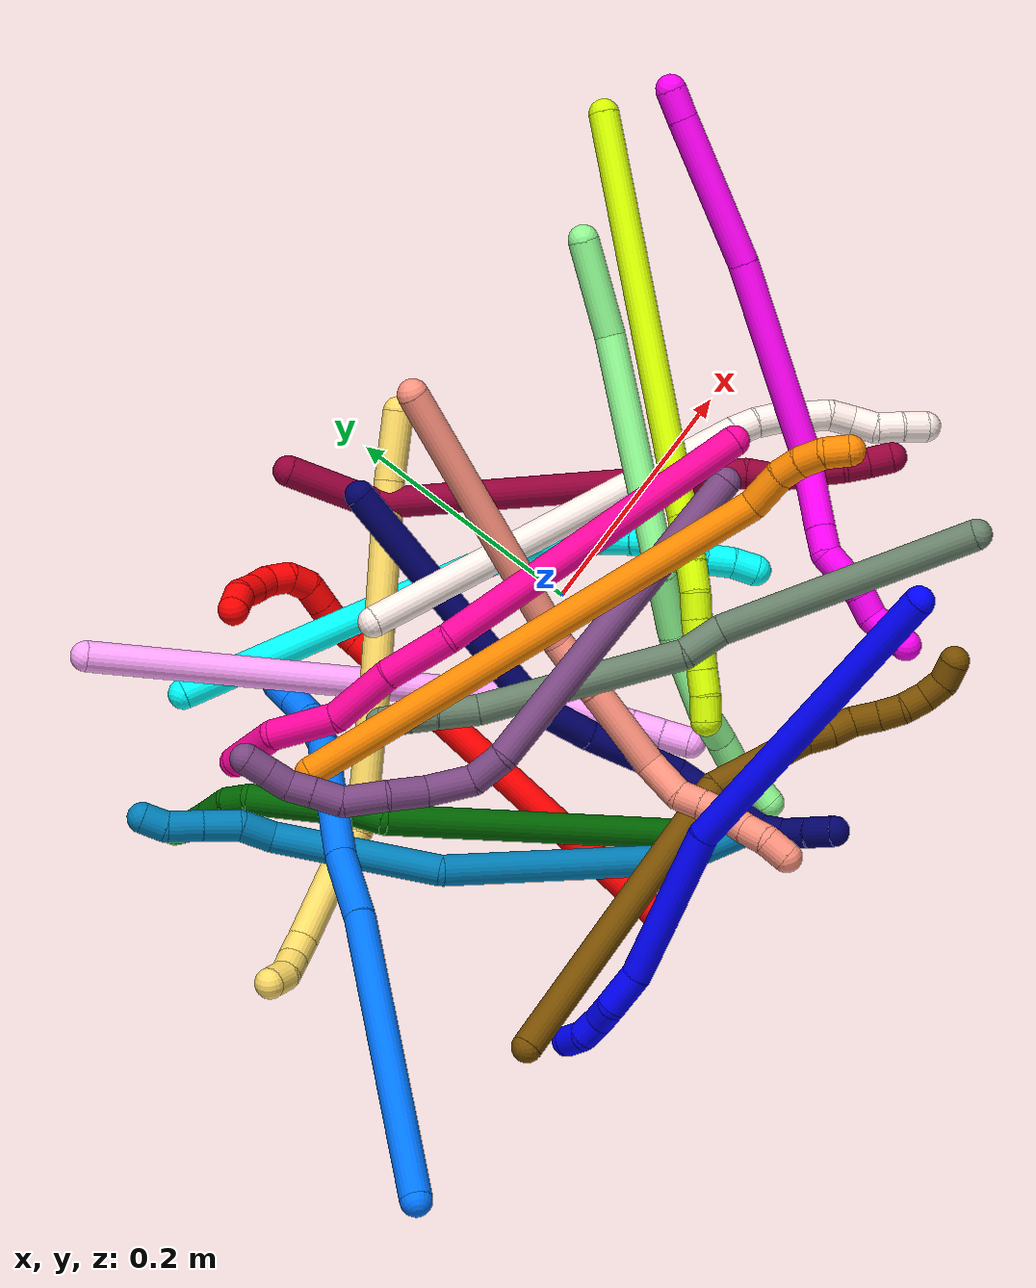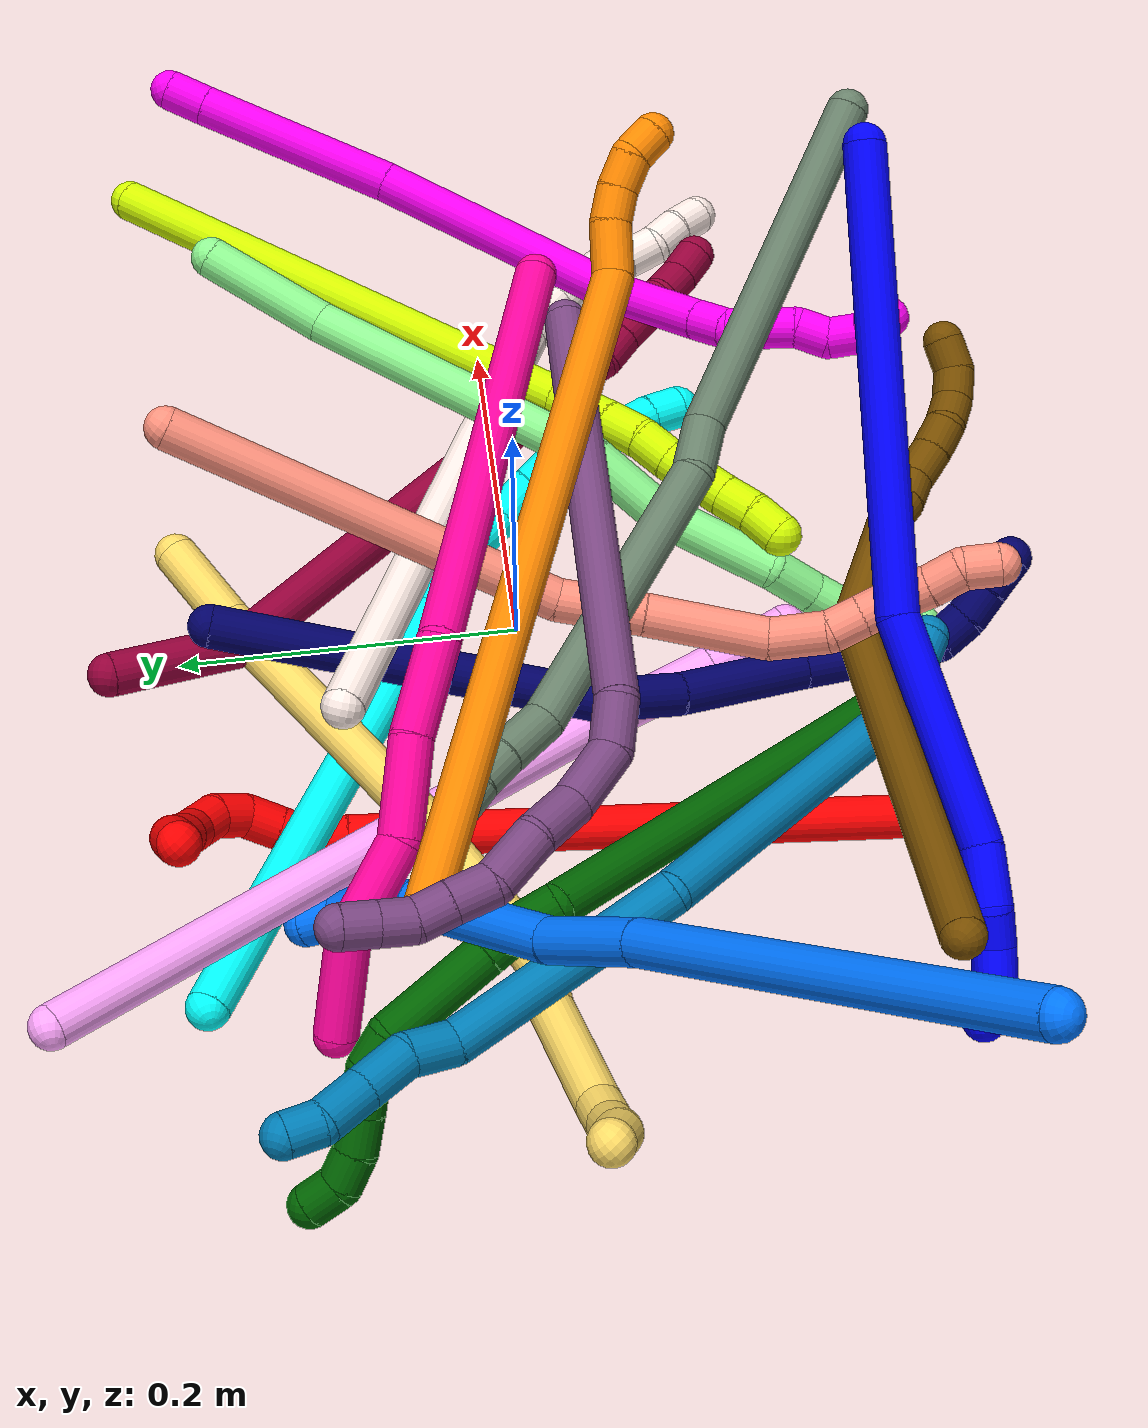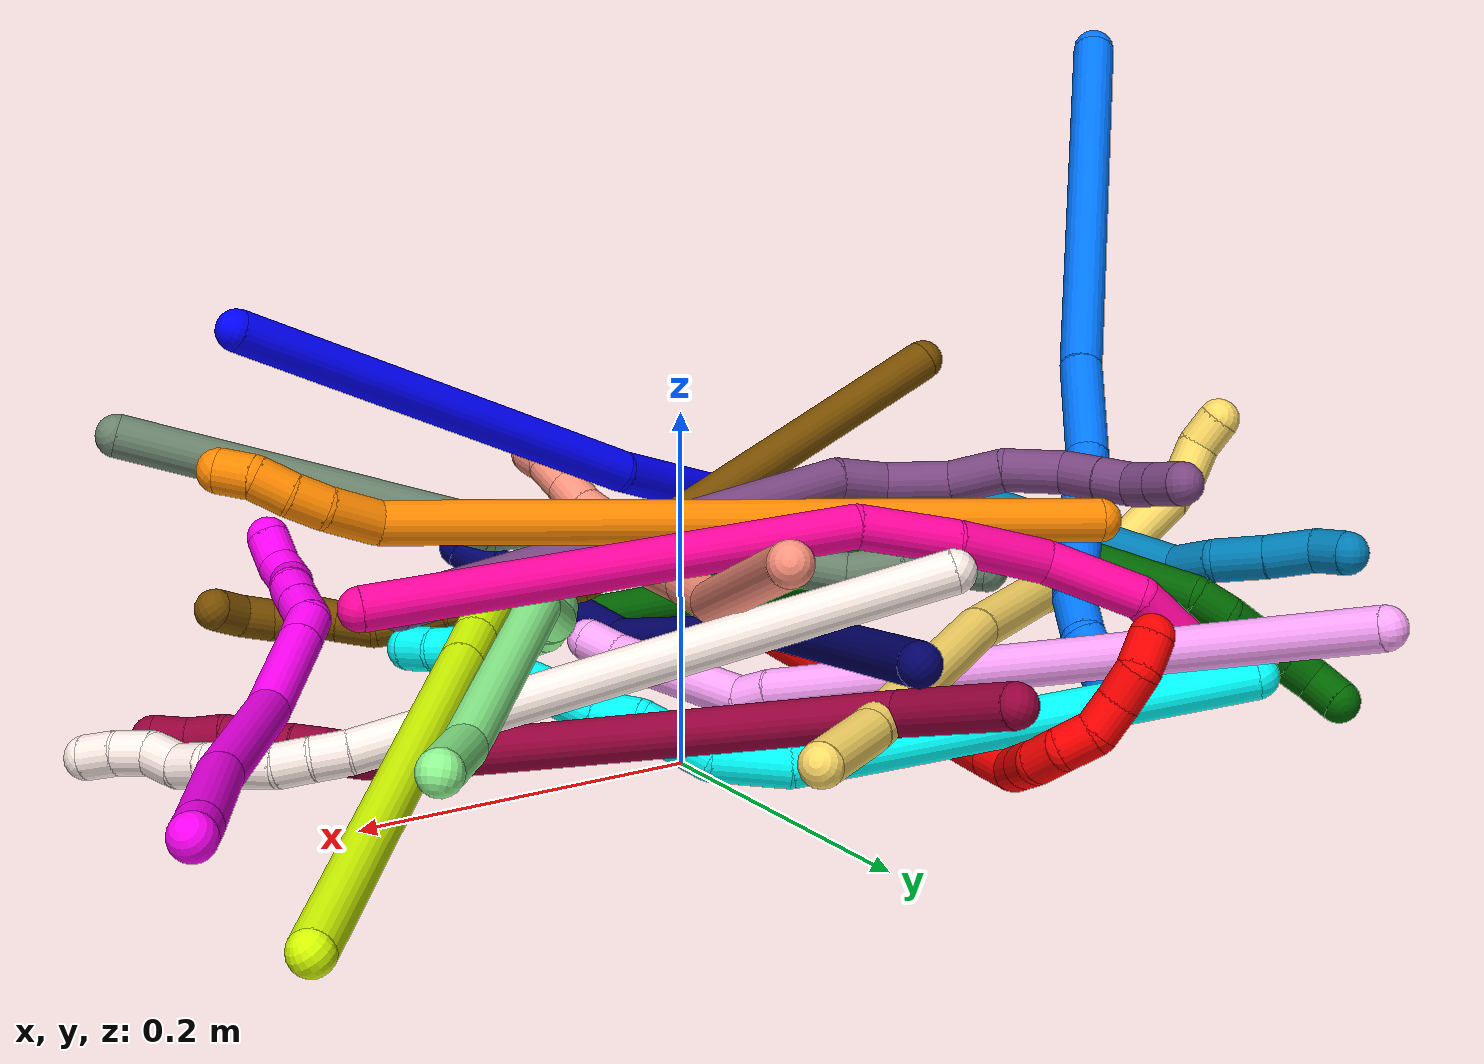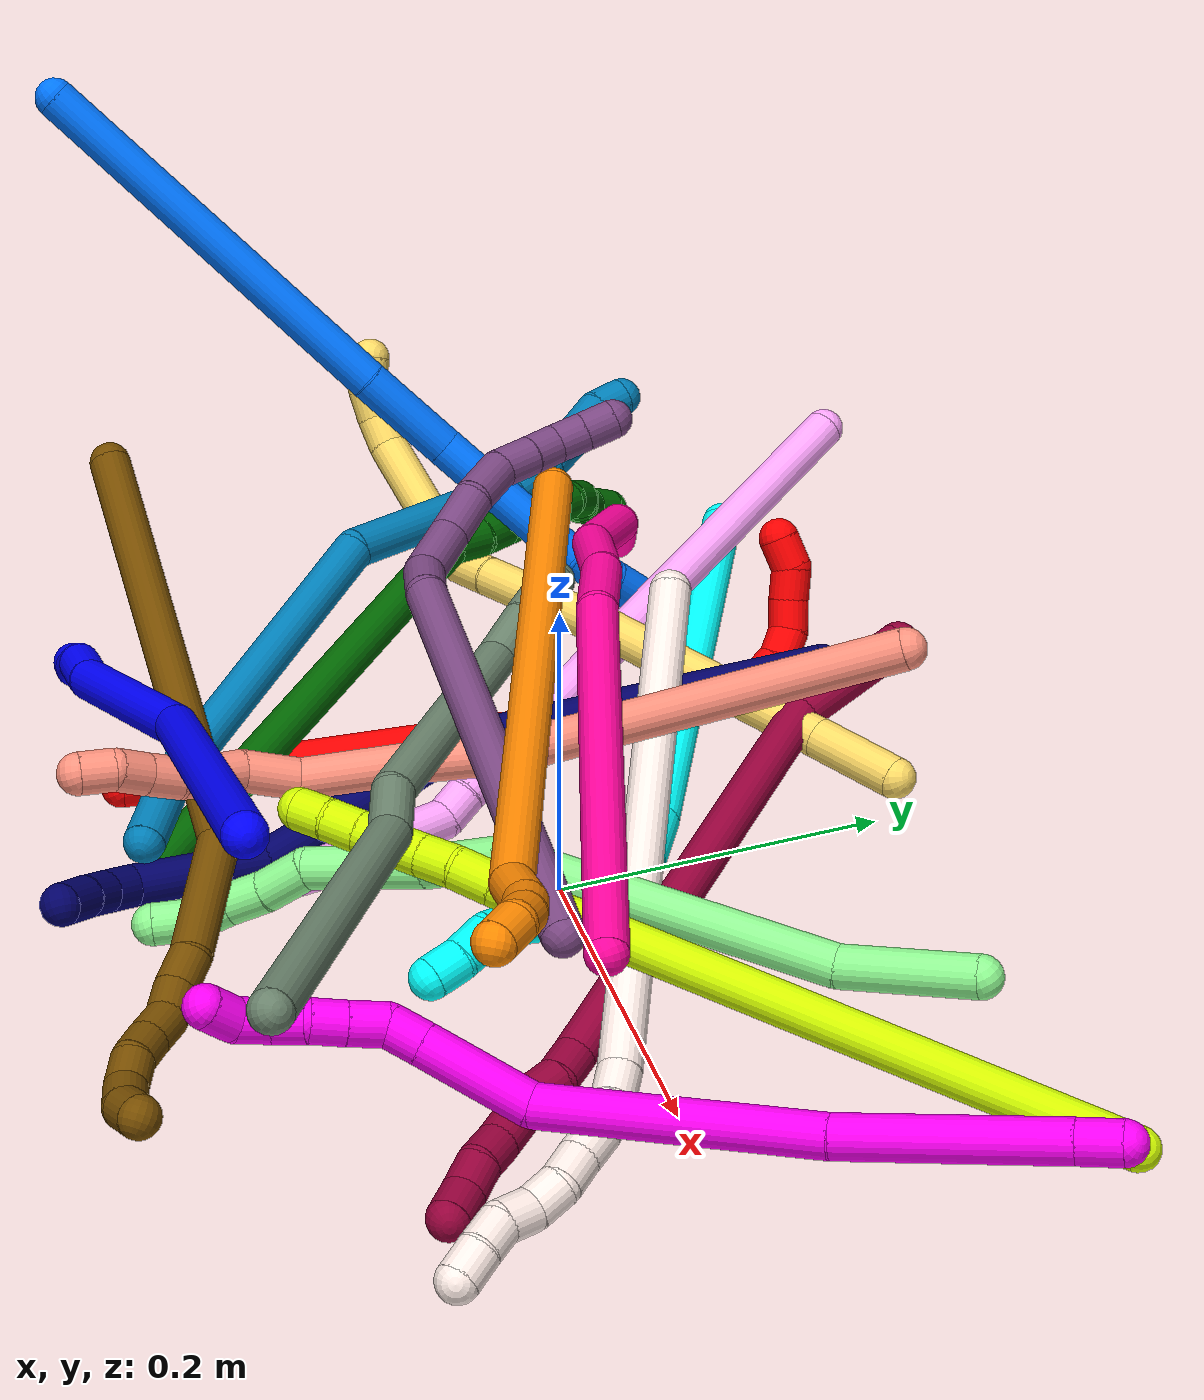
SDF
<sdf version="1.7">
 <world name="default">
  <plugin name="TubeGeneratorPlugin" filename="libtube_generator_plugin.so"/>
  <model name="photoneo_s_sensor">
   <static>1</static>
   <pose>0 0 2 1.57079 1.57079 3.14159</pose>
   <link name="link">
    <inertial><mass>0.1</mass></inertial>
    <sensor name="sensor" type="depth">
     <update_rate>30</update_rate>
     <camera>
      <horizontal_fov>1.22</horizontal_fov>
      <image><width>1920</width><height>1200</height><format>B8G8R8</format></image>
      <clip><near>0.1</near><far>4</far></clip>
      <depth_camera><output>points</output></depth_camera>
     </camera>
     <plugin name="camera_plugin" filename="libgazebo_ros_depth_camera.so">
      <baseline>0.2</baseline>
      <alwaysOn>1</alwaysOn>
      <updateRate>0.0</updateRate>
      <cameraName>camera_ir</cameraName>
      <imageTopicName>/camera/color/image_raw</imageTopicName>
      <cameraInfoTopicName>/camera/color/camera_info</cameraInfoTopicName>
      <depthImageTopicName>/camera/depth/image_raw</depthImageTopicName>
      <depthImageCameraInfoTopicName>/camera/depth/camera_info</depthImageCameraInfoTopicName>
      <pointCloudTopicName>/camera/depth/points</pointCloudTopicName>
      <frameName>fr_optical</frameName>
      <pointCloudCutoff>0.1</pointCloudCutoff>
      <pointCloudCutoffMax>2.0</pointCloudCutoffMax>
      <distortionK1>0</distortionK1>
      <distortionK2>0</distortionK2>
      <distortionK3>0</distortionK3>
      <distortionT1>0</distortionT1>
      <distortionT2>0</distortionT2>
      <CxPrime>0</CxPrime>
      <Cx>0</Cx>
      <Cy>0</Cy>
      <focalLength>0</focalLength>
      <hackBaseline>0</hackBaseline>
     </plugin>
    </sensor>
   </link>
  </model>
  <gravity>0 0 -9.8</gravity>
  <magnetic_field>6e-06 2.3e-05 -4.2e-05</magnetic_field>
  <atmosphere type="adiabatic"/>
  <physics name="default_physics" default="0" type="ode">
   <max_step_size>0.003</max_step_size>
   <real_time_factor>1</real_time_factor>
   <real_time_update_rate>1000</real_time_update_rate>
   <max_contacts>10000</max_contacts>
   <ode>
    <solver>
     <type>quick</type>
     <iters>100</iters>
     <sor>1.3</sor>
     <use_dynamic_moi_rescaling>0</use_dynamic_moi_rescaling>
    </solver>
    <constraints>
     <contact_max_correcting_vel>0</contact_max_correcting_vel>
     <contact_surface_layer>0.001</contact_surface_layer>
     <cfm>0</cfm>
     <erp>0.2</erp>
    </constraints>
   </ode>
  </physics>
  <scene><ambient>0.4 0.4 0.4 1</ambient><background>0.7 0.7 0.7 1</background><shadows>0</shadows></scene>
  <audio><device>default</device></audio>
  <spherical_coordinates>
   <surface_model>EARTH_WGS84</surface_model>
   <latitude_deg>0</latitude_deg>
   <longitude_deg>0</longitude_deg>
   <elevation>0</elevation>
   <heading_deg>0</heading_deg>
  </spherical_coordinates>
  <model name="bin">
   <static>1</static>
   <link name="bottom">
    <collision name="collision-bottom">
     <pose>0 0 -0.01 0 -0 0</pose>
     <geometry><box><size>0.8 0.6 0.02</size></box></geometry>
     <surface>
      <friction><ode><mu>100</mu><mu2>100</mu2></ode></friction>
      <contact><collide_bitmask>65535</collide_bitmask></contact>
     </surface>
    </collision>
   </link>
   <link name="west_wall">
    <collision name="collision-west_wall">
     <pose>-0.41 0 0.1 0 -0 0</pose>
     <geometry><box><size>0.02 0.6 0.2</size></box></geometry>
     <surface>
      <friction><ode><mu>100</mu><mu2>100</mu2></ode></friction>
      <contact><collide_bitmask>65535</collide_bitmask></contact>
     </surface>
    </collision>
   </link>
   <link name="east_wall">
    <collision name="collision-east_wall">
     <pose>0.41 0 0.1 0 -0 0</pose>
     <geometry><box><size>0.02 0.6 0.2</size></box></geometry>
     <surface>
      <friction><ode><mu>100</mu><mu2>100</mu2></ode></friction>
      <contact><collide_bitmask>65535</collide_bitmask></contact>
     </surface>
    </collision>
   </link>
   <link name="south_wall">
    <collision name="collision-south_wall">
     <pose>0 -0.31 0.1 0 -0 0</pose>
     <geometry><box><size>0.8 0.02 0.2</size></box></geometry>
     <surface>
      <friction><ode><mu>100</mu><mu2>100</mu2></ode></friction>
      <contact><collide_bitmask>65535</collide_bitmask></contact>
     </surface>
    </collision>
   </link>
   <link name="north_wall">
    <collision name="collision-north_wall">
     <pose>0 0.31 0.1 0 -0 0</pose>
     <geometry><box><size>0.8 0.02 0.2</size></box></geometry>
     <surface>
      <friction><ode><mu>100</mu><mu2>100</mu2></ode></friction>
      <contact><collide_bitmask>65535</collide_bitmask></contact>
     </surface>
    </collision>
   </link>
  </model>
  <model name="1">
   <static>0</static>
   <link name="1">
    <collision name="collision-cylinder-e_1_1_4">
     <pose>-0.005175 -0.004059 -0.13392 3.11129 -0.038607 -1.81082</pose>
     <geometry><cylinder><radius>0.0125</radius><length>0.268162</length></cylinder></geometry>
     <surface>
      <friction><ode><mu>1.16</mu><mu2>1.16</mu2><slip1>0</slip1><slip2>0</slip2></ode></friction>
      <contact><ode><kp>1e+06</kp><kd>1</kd><max_vel>0</max_vel><min_depth>0.001</min_depth></ode></contact>
     </surface>
    </collision>
    <visual name="visual-cylinder-e_1_1_4">
     <pose>-0.005175 -0.004059 -0.13392 3.11129 -0.038607 -1.81082</pose>
     <geometry><cylinder><radius>0.0125</radius><length>0.268162</length></cylinder></geometry>
     <material><ambient>0 0 1 1</ambient></material>
    </visual>
    <collision name="collision-cylinder-e_2_4_5">
     <pose>0.000253 0.002807 -0.332864 -2.97514 0.159446 -1.52762</pose>
     <geometry><cylinder><radius>0.0125</radius><length>0.133567</length></cylinder></geometry>
     <surface>
      <friction><ode><mu>1.16</mu><mu2>1.16</mu2><slip1>0</slip1><slip2>0</slip2></ode></friction>
      <contact><ode><kp>1e+06</kp><kd>1</kd><max_vel>0</max_vel><min_depth>0.001</min_depth></ode></contact>
     </surface>
    </collision>
    <visual name="visual-cylinder-e_2_4_5">
     <pose>0.000253 0.002807 -0.332864 -2.97514 0.159446 -1.52762</pose>
     <geometry><cylinder><radius>0.0125</radius><length>0.133567</length></cylinder></geometry>
     <material><ambient>0 0 1 1</ambient></material>
    </visual>
    <collision name="collision-cylinder-e_3_5_6">
     <pose>0.012374 0.012968 -0.415192 3.09748 0.08742 2.2074</pose>
     <geometry><cylinder><radius>0.0125</radius><length>0.034773</length></cylinder></geometry>
     <surface>
      <friction><ode><mu>1.16</mu><mu2>1.16</mu2><slip1>0</slip1><slip2>0</slip2></ode></friction>
      <contact><ode><kp>1e+06</kp><kd>1</kd><max_vel>0</max_vel><min_depth>0.001</min_depth></ode></contact>
     </surface>
    </collision>
    <visual name="visual-cylinder-e_3_5_6">
     <pose>0.012374 0.012968 -0.415192 3.09748 0.08742 2.2074</pose>
     <geometry><cylinder><radius>0.0125</radius><length>0.034773</length></cylinder></geometry>
     <material><ambient>0 0 1 1</ambient></material>
    </visual>
    <collision name="collision-cylinder-e_4_6_7">
     <pose>0.011241 0.014121 -0.442431 -2.95095 -0.256234 1.86461</pose>
     <geometry><cylinder><radius>0.0125</radius><length>0.020921</length></cylinder></geometry>
     <surface>
      <friction><ode><mu>1.16</mu><mu2>1.16</mu2><slip1>0</slip1><slip2>0</slip2></ode></friction>
      <contact><ode><kp>1e+06</kp><kd>1</kd><max_vel>0</max_vel><min_depth>0.001</min_depth></ode></contact>
     </surface>
    </collision>
    <visual name="visual-cylinder-e_4_6_7">
     <pose>0.011241 0.014121 -0.442431 -2.95095 -0.256234 1.86461</pose>
     <geometry><cylinder><radius>0.0125</radius><length>0.020921</length></cylinder></geometry>
     <material><ambient>0 0 1 1</ambient></material>
    </visual>
    <collision name="collision-cylinder-e_5_7_8">
     <pose>0.007535 0.01572 -0.46286 3.11117 -0.100203 -2.55258</pose>
     <geometry><cylinder><radius>0.0125</radius><length>0.021103</length></cylinder></geometry>
     <surface>
      <friction><ode><mu>1.16</mu><mu2>1.16</mu2><slip1>0</slip1><slip2>0</slip2></ode></friction>
      <contact><ode><kp>1e+06</kp><kd>1</kd><max_vel>0</max_vel><min_depth>0.001</min_depth></ode></contact>
     </surface>
    </collision>
    <visual name="visual-cylinder-e_5_7_8">
     <pose>0.007535 0.01572 -0.46286 3.11117 -0.100203 -2.55258</pose>
     <geometry><cylinder><radius>0.0125</radius><length>0.021103</length></cylinder></geometry>
     <material><ambient>0 0 1 1</ambient></material>
    </visual>
    <collision name="collision-cylinder-e_6_8_2">
     <pose>0.000643 0.015209 -0.482365 3.12039 -0.574662 -3.06988</pose>
     <geometry><cylinder><radius>0.0125</radius><length>0.021474</length></cylinder></geometry>
     <surface>
      <friction><ode><mu>1.16</mu><mu2>1.16</mu2><slip1>0</slip1><slip2>0</slip2></ode></friction>
      <contact><ode><kp>1e+06</kp><kd>1</kd><max_vel>0</max_vel><min_depth>0.001</min_depth></ode></contact>
     </surface>
    </collision>
    <visual name="visual-cylinder-e_6_8_2">
     <pose>0.000643 0.015209 -0.482365 3.12039 -0.574662 -3.06988</pose>
     <geometry><cylinder><radius>0.0125</radius><length>0.021474</length></cylinder></geometry>
     <material><ambient>0 0 1 1</ambient></material>
    </visual>
    <collision name="collision-sphere-2">
     <pose>-0.005193 0.015018 -0.491375 0 -0 0</pose>
     <geometry><sphere><radius>0.0125</radius></sphere></geometry>
     <surface>
      <friction><ode><mu>1.16</mu><mu2>1.16</mu2><slip1>0</slip1><slip2>0</slip2></ode></friction>
      <contact><ode><kp>1e+06</kp><kd>1</kd><max_vel>0</max_vel><min_depth>0.001</min_depth></ode></contact>
     </surface>
    </collision>
    <visual name="visual-sphere-2">
     <pose>-0.005193 0.015018 -0.491375 0 -0 0</pose>
     <geometry><sphere><radius>0.0125</radius></sphere></geometry>
     <material><ambient>0 0 1 1</ambient></material>
    </visual>
    <collision name="collision-sphere-4">
     <pose>-0.01035 -0.008118 -0.267839 0 -0 0</pose>
     <geometry><sphere><radius>0.0125</radius></sphere></geometry>
     <surface>
      <friction><ode><mu>1.16</mu><mu2>1.16</mu2><slip1>0</slip1><slip2>0</slip2></ode></friction>
      <contact><ode><kp>1e+06</kp><kd>1</kd><max_vel>0</max_vel><min_depth>0.001</min_depth></ode></contact>
     </surface>
    </collision>
    <visual name="visual-sphere-4">
     <pose>-0.01035 -0.008118 -0.267839 0 -0 0</pose>
     <geometry><sphere><radius>0.0125</radius></sphere></geometry>
     <material><ambient>0 0 1 1</ambient></material>
    </visual>
    <collision name="collision-sphere-1">
     <geometry><sphere><radius>0.0125</radius></sphere></geometry>
     <surface>
      <friction><ode><mu>1.16</mu><mu2>1.16</mu2><slip1>0</slip1><slip2>0</slip2></ode></friction>
      <contact><ode><kp>1e+06</kp><kd>1</kd><max_vel>0</max_vel><min_depth>0.001</min_depth></ode></contact>
     </surface>
    </collision>
    <visual name="visual-sphere-1">
     <geometry><sphere><radius>0.0125</radius></sphere></geometry>
     <material><ambient>0 0 1 1</ambient></material>
    </visual>
    <collision name="collision-sphere-8">
     <pose>0.006479 0.0154 -0.473354 0 -0 0</pose>
     <geometry><sphere><radius>0.0125</radius></sphere></geometry>
     <surface>
      <friction><ode><mu>1.16</mu><mu2>1.16</mu2><slip1>0</slip1><slip2>0</slip2></ode></friction>
      <contact><ode><kp>1e+06</kp><kd>1</kd><max_vel>0</max_vel><min_depth>0.001</min_depth></ode></contact>
     </surface>
    </collision>
    <visual name="visual-sphere-8">
     <pose>0.006479 0.0154 -0.473354 0 -0 0</pose>
     <geometry><sphere><radius>0.0125</radius></sphere></geometry>
     <material><ambient>0 0 1 1</ambient></material>
    </visual>
    <collision name="collision-sphere-5">
     <pose>0.010856 0.013731 -0.397889 0 -0 0</pose>
     <geometry><sphere><radius>0.0125</radius></sphere></geometry>
     <surface>
      <friction><ode><mu>1.16</mu><mu2>1.16</mu2><slip1>0</slip1><slip2>0</slip2></ode></friction>
      <contact><ode><kp>1e+06</kp><kd>1</kd><max_vel>0</max_vel><min_depth>0.001</min_depth></ode></contact>
     </surface>
    </collision>
    <visual name="visual-sphere-5">
     <pose>0.010856 0.013731 -0.397889 0 -0 0</pose>
     <geometry><sphere><radius>0.0125</radius></sphere></geometry>
     <material><ambient>0 0 1 1</ambient></material>
    </visual>
    <collision name="collision-sphere-6">
     <pose>0.013892 0.012204 -0.432495 0 -0 0</pose>
     <geometry><sphere><radius>0.0125</radius></sphere></geometry>
     <surface>
      <friction><ode><mu>1.16</mu><mu2>1.16</mu2><slip1>0</slip1><slip2>0</slip2></ode></friction>
      <contact><ode><kp>1e+06</kp><kd>1</kd><max_vel>0</max_vel><min_depth>0.001</min_depth></ode></contact>
     </surface>
    </collision>
    <visual name="visual-sphere-6">
     <pose>0.013892 0.012204 -0.432495 0 -0 0</pose>
     <geometry><sphere><radius>0.0125</radius></sphere></geometry>
     <material><ambient>0 0 1 1</ambient></material>
    </visual>
    <collision name="collision-sphere-7">
     <pose>0.00859 0.016039 -0.452366 0 -0 0</pose>
     <geometry><sphere><radius>0.0125</radius></sphere></geometry>
     <surface>
      <friction><ode><mu>1.16</mu><mu2>1.16</mu2><slip1>0</slip1><slip2>0</slip2></ode></friction>
      <contact><ode><kp>1e+06</kp><kd>1</kd><max_vel>0</max_vel><min_depth>0.001</min_depth></ode></contact>
     </surface>
    </collision>
    <visual name="visual-sphere-7">
     <pose>0.00859 0.016039 -0.452366 0 -0 0</pose>
     <geometry><sphere><radius>0.0125</radius></sphere></geometry>
     <material><ambient>0 0 1 1</ambient></material>
    </visual>
    <inertial>
     <pose>-0.001031 0.001382 -0.248383 0 -0 0</pose>
     <mass>0.5</mass>
     <inertia>
      <ixx>-0.002149</ixx>
      <ixy>0</ixy>
      <ixz>0</ixz>
      <iyy>-0.001376</iyy>
      <iyz>0</iyz>
      <izz>8e-06</izz>
     </inertia>
    </inertial>
   </link>
   <pose>0.158813 -0.218957 0.223217 -0.866759 -0.891704 -2.16888</pose>
  </model>
  <model name="2">
   <static>0</static>
   <link name="2">
    <collision name="collision-cylinder-e_1_1_4">
     <pose>0.013882 0.130103 -0.106642 -2.25742 0.082336 -0.173611</pose>
     <geometry><cylinder><radius>0.0125</radius><length>0.337592</length></cylinder></geometry>
     <surface>
      <friction><ode><mu>1.16</mu><mu2>1.16</mu2><slip1>0</slip1><slip2>0</slip2></ode></friction>
      <contact><ode><kp>1e+06</kp><kd>1</kd><max_vel>0</max_vel><min_depth>0.001</min_depth></ode></contact>
     </surface>
    </collision>
    <visual name="visual-cylinder-e_1_1_4">
     <pose>0.013882 0.130103 -0.106642 -2.25742 0.082336 -0.173611</pose>
     <geometry><cylinder><radius>0.0125</radius><length>0.337592</length></cylinder></geometry>
     <material><ambient>1 0 0 1</ambient></material>
    </visual>
    <collision name="collision-cylinder-e_2_4_5">
     <pose>0.028958 0.269001 -0.219979 -2.22136 0.10755 -0.216372</pose>
     <geometry><cylinder><radius>0.0125</radius><length>0.022235</length></cylinder></geometry>
     <surface>
      <friction><ode><mu>1.16</mu><mu2>1.16</mu2><slip1>0</slip1><slip2>0</slip2></ode></friction>
      <contact><ode><kp>1e+06</kp><kd>1</kd><max_vel>0</max_vel><min_depth>0.001</min_depth></ode></contact>
     </surface>
    </collision>
    <visual name="visual-cylinder-e_2_4_5">
     <pose>0.028958 0.269001 -0.219979 -2.22136 0.10755 -0.216372</pose>
     <geometry><cylinder><radius>0.0125</radius><length>0.022235</length></cylinder></geometry>
     <material><ambient>1 0 0 1</ambient></material>
    </visual>
    <collision name="collision-cylinder-e_3_5_6">
     <pose>0.032056 0.281694 -0.235747 -2.73589 0.190541 -0.869856</pose>
     <geometry><cylinder><radius>0.0125</radius><length>0.020113</length></cylinder></geometry>
     <surface>
      <friction><ode><mu>1.16</mu><mu2>1.16</mu2><slip1>0</slip1><slip2>0</slip2></ode></friction>
      <contact><ode><kp>1e+06</kp><kd>1</kd><max_vel>0</max_vel><min_depth>0.001</min_depth></ode></contact>
     </surface>
    </collision>
    <visual name="visual-cylinder-e_3_5_6">
     <pose>0.032056 0.281694 -0.235747 -2.73589 0.190541 -0.869856</pose>
     <geometry><cylinder><radius>0.0125</radius><length>0.020113</length></cylinder></geometry>
     <material><ambient>1 0 0 1</ambient></material>
    </visual>
    <collision name="collision-cylinder-e_4_6_7">
     <pose>0.035963 0.28949 -0.253838 -2.73352 0.201073 -0.907237</pose>
     <geometry><cylinder><radius>0.0125</radius><length>0.020053</length></cylinder></geometry>
     <surface>
      <friction><ode><mu>1.16</mu><mu2>1.16</mu2><slip1>0</slip1><slip2>0</slip2></ode></friction>
      <contact><ode><kp>1e+06</kp><kd>1</kd><max_vel>0</max_vel><min_depth>0.001</min_depth></ode></contact>
     </surface>
    </collision>
    <visual name="visual-cylinder-e_4_6_7">
     <pose>0.035963 0.28949 -0.253838 -2.73352 0.201073 -0.907237</pose>
     <geometry><cylinder><radius>0.0125</radius><length>0.020053</length></cylinder></geometry>
     <material><ambient>1 0 0 1</ambient></material>
    </visual>
    <collision name="collision-cylinder-e_5_7_8">
     <pose>0.044314 0.297583 -0.269345 -2.56784 0.687741 -1.76338</pose>
     <geometry><cylinder><radius>0.0125</radius><length>0.020001</length></cylinder></geometry>
     <surface>
      <friction><ode><mu>1.16</mu><mu2>1.16</mu2><slip1>0</slip1><slip2>0</slip2></ode></friction>
      <contact><ode><kp>1e+06</kp><kd>1</kd><max_vel>0</max_vel><min_depth>0.001</min_depth></ode></contact>
     </surface>
    </collision>
    <visual name="visual-cylinder-e_5_7_8">
     <pose>0.044314 0.297583 -0.269345 -2.56784 0.687741 -1.76338</pose>
     <geometry><cylinder><radius>0.0125</radius><length>0.020001</length></cylinder></geometry>
     <material><ambient>1 0 0 1</ambient></material>
    </visual>
    <collision name="collision-cylinder-e_6_8_9">
     <pose>0.059586 0.305675 -0.278121 -2.10133 1.10209 -1.6412</pose>
     <geometry><cylinder><radius>0.0125</radius><length>0.020005</length></cylinder></geometry>
     <surface>
      <friction><ode><mu>1.16</mu><mu2>1.16</mu2><slip1>0</slip1><slip2>0</slip2></ode></friction>
      <contact><ode><kp>1e+06</kp><kd>1</kd><max_vel>0</max_vel><min_depth>0.001</min_depth></ode></contact>
     </surface>
    </collision>
    <visual name="visual-cylinder-e_6_8_9">
     <pose>0.059586 0.305675 -0.278121 -2.10133 1.10209 -1.6412</pose>
     <geometry><cylinder><radius>0.0125</radius><length>0.020005</length></cylinder></geometry>
     <material><ambient>1 0 0 1</ambient></material>
    </visual>
    <collision name="collision-cylinder-e_7_9_10">
     <pose>0.078252 0.308703 -0.282489 2.74596 1.34328 2.6476</pose>
     <geometry><cylinder><radius>0.0125</radius><length>0.02</length></cylinder></geometry>
     <surface>
      <friction><ode><mu>1.16</mu><mu2>1.16</mu2><slip1>0</slip1><slip2>0</slip2></ode></friction>
      <contact><ode><kp>1e+06</kp><kd>1</kd><max_vel>0</max_vel><min_depth>0.001</min_depth></ode></contact>
     </surface>
    </collision>
    <visual name="visual-cylinder-e_7_9_10">
     <pose>0.078252 0.308703 -0.282489 2.74596 1.34328 2.6476</pose>
     <geometry><cylinder><radius>0.0125</radius><length>0.02</length></cylinder></geometry>
     <material><ambient>1 0 0 1</ambient></material>
    </visual>
    <collision name="collision-cylinder-e_8_10_11">
     <pose>0.097389 0.30676 -0.287824 2.82291 1.22113 2.69011</pose>
     <geometry><cylinder><radius>0.0125</radius><length>0.02</length></cylinder></geometry>
     <surface>
      <friction><ode><mu>1.16</mu><mu2>1.16</mu2><slip1>0</slip1><slip2>0</slip2></ode></friction>
      <contact><ode><kp>1e+06</kp><kd>1</kd><max_vel>0</max_vel><min_depth>0.001</min_depth></ode></contact>
     </surface>
    </collision>
    <visual name="visual-cylinder-e_8_10_11">
     <pose>0.097389 0.30676 -0.287824 2.82291 1.22113 2.69011</pose>
     <geometry><cylinder><radius>0.0125</radius><length>0.02</length></cylinder></geometry>
     <material><ambient>1 0 0 1</ambient></material>
    </visual>
    <collision name="collision-cylinder-e_9_11_2">
     <pose>0.115936 0.301713 -0.290403 1.40278 1.15589 1.0071</pose>
     <geometry><cylinder><radius>0.0125</radius><length>0.02</length></cylinder></geometry>
     <surface>
      <friction><ode><mu>1.16</mu><mu2>1.16</mu2><slip1>0</slip1><slip2>0</slip2></ode></friction>
      <contact><ode><kp>1e+06</kp><kd>1</kd><max_vel>0</max_vel><min_depth>0.001</min_depth></ode></contact>
     </surface>
    </collision>
    <visual name="visual-cylinder-e_9_11_2">
     <pose>0.115936 0.301713 -0.290403 1.40278 1.15589 1.0071</pose>
     <geometry><cylinder><radius>0.0125</radius><length>0.02</length></cylinder></geometry>
     <material><ambient>1 0 0 1</ambient></material>
    </visual>
    <collision name="collision-sphere-2">
     <pose>0.125087 0.297738 -0.289729 0 -0 0</pose>
     <geometry><sphere><radius>0.0125</radius></sphere></geometry>
     <surface>
      <friction><ode><mu>1.16</mu><mu2>1.16</mu2><slip1>0</slip1><slip2>0</slip2></ode></friction>
      <contact><ode><kp>1e+06</kp><kd>1</kd><max_vel>0</max_vel><min_depth>0.001</min_depth></ode></contact>
     </surface>
    </collision>
    <visual name="visual-sphere-2">
     <pose>0.125087 0.297738 -0.289729 0 -0 0</pose>
     <geometry><sphere><radius>0.0125</radius></sphere></geometry>
     <material><ambient>1 0 0 1</ambient></material>
    </visual>
    <collision name="collision-sphere-11">
     <pose>0.106784 0.305687 -0.291077 0 -0 0</pose>
     <geometry><sphere><radius>0.0125</radius></sphere></geometry>
     <surface>
      <friction><ode><mu>1.16</mu><mu2>1.16</mu2><slip1>0</slip1><slip2>0</slip2></ode></friction>
      <contact><ode><kp>1e+06</kp><kd>1</kd><max_vel>0</max_vel><min_depth>0.001</min_depth></ode></contact>
     </surface>
    </collision>
    <visual name="visual-sphere-11">
     <pose>0.106784 0.305687 -0.291077 0 -0 0</pose>
     <geometry><sphere><radius>0.0125</radius></sphere></geometry>
     <material><ambient>1 0 0 1</ambient></material>
    </visual>
    <collision name="collision-sphere-10">
     <pose>0.087995 0.307834 -0.28457 0 -0 0</pose>
     <geometry><sphere><radius>0.0125</radius></sphere></geometry>
     <surface>
      <friction><ode><mu>1.16</mu><mu2>1.16</mu2><slip1>0</slip1><slip2>0</slip2></ode></friction>
      <contact><ode><kp>1e+06</kp><kd>1</kd><max_vel>0</max_vel><min_depth>0.001</min_depth></ode></contact>
     </surface>
    </collision>
    <visual name="visual-sphere-10">
     <pose>0.087995 0.307834 -0.28457 0 -0 0</pose>
     <geometry><sphere><radius>0.0125</radius></sphere></geometry>
     <material><ambient>1 0 0 1</ambient></material>
    </visual>
    <collision name="collision-sphere-9">
     <pose>0.06851 0.309572 -0.280408 0 -0 0</pose>
     <geometry><sphere><radius>0.0125</radius></sphere></geometry>
     <surface>
      <friction><ode><mu>1.16</mu><mu2>1.16</mu2><slip1>0</slip1><slip2>0</slip2></ode></friction>
      <contact><ode><kp>1e+06</kp><kd>1</kd><max_vel>0</max_vel><min_depth>0.001</min_depth></ode></contact>
     </surface>
    </collision>
    <visual name="visual-sphere-9">
     <pose>0.06851 0.309572 -0.280408 0 -0 0</pose>
     <geometry><sphere><radius>0.0125</radius></sphere></geometry>
     <material><ambient>1 0 0 1</ambient></material>
    </visual>
    <collision name="collision-sphere-4">
     <pose>0.027765 0.260206 -0.213285 0 -0 0</pose>
     <geometry><sphere><radius>0.0125</radius></sphere></geometry>
     <surface>
      <friction><ode><mu>1.16</mu><mu2>1.16</mu2><slip1>0</slip1><slip2>0</slip2></ode></friction>
      <contact><ode><kp>1e+06</kp><kd>1</kd><max_vel>0</max_vel><min_depth>0.001</min_depth></ode></contact>
     </surface>
    </collision>
    <visual name="visual-sphere-4">
     <pose>0.027765 0.260206 -0.213285 0 -0 0</pose>
     <geometry><sphere><radius>0.0125</radius></sphere></geometry>
     <material><ambient>1 0 0 1</ambient></material>
    </visual>
    <collision name="collision-sphere-1">
     <geometry><sphere><radius>0.0125</radius></sphere></geometry>
     <surface>
      <friction><ode><mu>1.16</mu><mu2>1.16</mu2><slip1>0</slip1><slip2>0</slip2></ode></friction>
      <contact><ode><kp>1e+06</kp><kd>1</kd><max_vel>0</max_vel><min_depth>0.001</min_depth></ode></contact>
     </surface>
    </collision>
    <visual name="visual-sphere-1">
     <geometry><sphere><radius>0.0125</radius></sphere></geometry>
     <material><ambient>1 0 0 1</ambient></material>
    </visual>
    <collision name="collision-sphere-8">
     <pose>0.050662 0.301778 -0.275835 0 -0 0</pose>
     <geometry><sphere><radius>0.0125</radius></sphere></geometry>
     <surface>
      <friction><ode><mu>1.16</mu><mu2>1.16</mu2><slip1>0</slip1><slip2>0</slip2></ode></friction>
      <contact><ode><kp>1e+06</kp><kd>1</kd><max_vel>0</max_vel><min_depth>0.001</min_depth></ode></contact>
     </surface>
    </collision>
    <visual name="visual-sphere-8">
     <pose>0.050662 0.301778 -0.275835 0 -0 0</pose>
     <geometry><sphere><radius>0.0125</radius></sphere></geometry>
     <material><ambient>1 0 0 1</ambient></material>
    </visual>
    <collision name="collision-sphere-5">
     <pose>0.030151 0.277797 -0.226674 0 -0 0</pose>
     <geometry><sphere><radius>0.0125</radius></sphere></geometry>
     <surface>
      <friction><ode><mu>1.16</mu><mu2>1.16</mu2><slip1>0</slip1><slip2>0</slip2></ode></friction>
      <contact><ode><kp>1e+06</kp><kd>1</kd><max_vel>0</max_vel><min_depth>0.001</min_depth></ode></contact>
     </surface>
    </collision>
    <visual name="visual-sphere-5">
     <pose>0.030151 0.277797 -0.226674 0 -0 0</pose>
     <geometry><sphere><radius>0.0125</radius></sphere></geometry>
     <material><ambient>1 0 0 1</ambient></material>
    </visual>
    <collision name="collision-sphere-6">
     <pose>0.033961 0.285592 -0.24482 0 -0 0</pose>
     <geometry><sphere><radius>0.0125</radius></sphere></geometry>
     <surface>
      <friction><ode><mu>1.16</mu><mu2>1.16</mu2><slip1>0</slip1><slip2>0</slip2></ode></friction>
      <contact><ode><kp>1e+06</kp><kd>1</kd><max_vel>0</max_vel><min_depth>0.001</min_depth></ode></contact>
     </surface>
    </collision>
    <visual name="visual-sphere-6">
     <pose>0.033961 0.285592 -0.24482 0 -0 0</pose>
     <geometry><sphere><radius>0.0125</radius></sphere></geometry>
     <material><ambient>1 0 0 1</ambient></material>
    </visual>
    <collision name="collision-sphere-7">
     <pose>0.037966 0.293389 -0.262855 0 -0 0</pose>
     <geometry><sphere><radius>0.0125</radius></sphere></geometry>
     <surface>
      <friction><ode><mu>1.16</mu><mu2>1.16</mu2><slip1>0</slip1><slip2>0</slip2></ode></friction>
      <contact><ode><kp>1e+06</kp><kd>1</kd><max_vel>0</max_vel><min_depth>0.001</min_depth></ode></contact>
     </surface>
    </collision>
    <visual name="visual-sphere-7">
     <pose>0.037966 0.293389 -0.262855 0 -0 0</pose>
     <geometry><sphere><radius>0.0125</radius></sphere></geometry>
     <material><ambient>1 0 0 1</ambient></material>
    </visual>
    <inertial>
     <pose>0.029213 0.183569 -0.15778 0 -0 0</pose>
     <mass>0.5</mass>
     <inertia>
      <ixx>0.002615</ixx>
      <ixy>0</ixy>
      <ixz>0</ixz>
      <iyy>-0.002506</iyy>
      <iyz>0</iyz>
      <izz>-0.002779</izz>
     </inertia>
    </inertial>
   </link>
   <pose>-0.159776 -0.225379 0.013421 -2.37621 -0.719041 2.94014</pose>
  </model>
  <model name="3">
   <static>0</static>
   <link name="3">
    <collision name="collision-cylinder-e_1_1_4">
     <pose>0.066369 -0.041484 0.101593 0.387674 0.543948 0.109382</pose>
     <geometry><cylinder><radius>0.0125</radius><length>0.256491</length></cylinder></geometry>
     <surface>
      <friction><ode><mu>1.16</mu><mu2>1.16</mu2><slip1>0</slip1><slip2>0</slip2></ode></friction>
      <contact><ode><kp>1e+06</kp><kd>1</kd><max_vel>0</max_vel><min_depth>0.001</min_depth></ode></contact>
     </surface>
    </collision>
    <visual name="visual-cylinder-e_1_1_4">
     <pose>0.066369 -0.041484 0.101593 0.387674 0.543948 0.109382</pose>
     <geometry><cylinder><radius>0.0125</radius><length>0.256491</length></cylinder></geometry>
     <material><ambient>0.003922 1 0.996078 1</ambient></material>
    </visual>
    <collision name="collision-cylinder-e_2_4_5">
     <pose>0.142325 -0.095514 0.218438 0.688311 0.451918 0.164419</pose>
     <geometry><cylinder><radius>0.0125</radius><length>0.043906</length></cylinder></geometry>
     <surface>
      <friction><ode><mu>1.16</mu><mu2>1.16</mu2><slip1>0</slip1><slip2>0</slip2></ode></friction>
      <contact><ode><kp>1e+06</kp><kd>1</kd><max_vel>0</max_vel><min_depth>0.001</min_depth></ode></contact>
     </surface>
    </collision>
    <visual name="visual-cylinder-e_2_4_5">
     <pose>0.142325 -0.095514 0.218438 0.688311 0.451918 0.164419</pose>
     <geometry><cylinder><radius>0.0125</radius><length>0.043906</length></cylinder></geometry>
     <material><ambient>0.003922 1 0.996078 1</ambient></material>
    </visual>
    <collision name="collision-cylinder-e_3_5_6">
     <pose>0.1606 -0.126097 0.241841 1.14638 0.413636 0.269228</pose>
     <geometry><cylinder><radius>0.0125</radius><length>0.043234</length></cylinder></geometry>
     <surface>
      <friction><ode><mu>1.16</mu><mu2>1.16</mu2><slip1>0</slip1><slip2>0</slip2></ode></friction>
      <contact><ode><kp>1e+06</kp><kd>1</kd><max_vel>0</max_vel><min_depth>0.001</min_depth></ode></contact>
     </surface>
    </collision>
    <visual name="visual-cylinder-e_3_5_6">
     <pose>0.1606 -0.126097 0.241841 1.14638 0.413636 0.269228</pose>
     <geometry><cylinder><radius>0.0125</radius><length>0.043234</length></cylinder></geometry>
     <material><ambient>0.003922 1 0.996078 1</ambient></material>
    </visual>
    <collision name="collision-cylinder-e_4_6_7">
     <pose>0.17804 -0.151474 0.255731 0.907151 0.754075 0.38137</pose>
     <geometry><cylinder><radius>0.0125</radius><length>0.025564</length></cylinder></geometry>
     <surface>
      <friction><ode><mu>1.16</mu><mu2>1.16</mu2><slip1>0</slip1><slip2>0</slip2></ode></friction>
      <contact><ode><kp>1e+06</kp><kd>1</kd><max_vel>0</max_vel><min_depth>0.001</min_depth></ode></contact>
     </surface>
    </collision>
    <visual name="visual-cylinder-e_4_6_7">
     <pose>0.17804 -0.151474 0.255731 0.907151 0.754075 0.38137</pose>
     <geometry><cylinder><radius>0.0125</radius><length>0.025564</length></cylinder></geometry>
     <material><ambient>0.003922 1 0.996078 1</ambient></material>
    </visual>
    <collision name="collision-cylinder-e_5_7_8">
     <pose>0.194458 -0.168204 0.265314 1.18227 0.647103 0.442776</pose>
     <geometry><cylinder><radius>0.0125</radius><length>0.025436</length></cylinder></geometry>
     <surface>
      <friction><ode><mu>1.16</mu><mu2>1.16</mu2><slip1>0</slip1><slip2>0</slip2></ode></friction>
      <contact><ode><kp>1e+06</kp><kd>1</kd><max_vel>0</max_vel><min_depth>0.001</min_depth></ode></contact>
     </surface>
    </collision>
    <visual name="visual-cylinder-e_5_7_8">
     <pose>0.194458 -0.168204 0.265314 1.18227 0.647103 0.442776</pose>
     <geometry><cylinder><radius>0.0125</radius><length>0.025436</length></cylinder></geometry>
     <material><ambient>0.003922 1 0.996078 1</ambient></material>
    </visual>
    <collision name="collision-cylinder-e_6_8_9">
     <pose>0.208394 -0.18484 0.272323 1.15897 0.670317 0.448219</pose>
     <geometry><cylinder><radius>0.0125</radius><length>0.020181</length></cylinder></geometry>
     <surface>
      <friction><ode><mu>1.16</mu><mu2>1.16</mu2><slip1>0</slip1><slip2>0</slip2></ode></friction>
      <contact><ode><kp>1e+06</kp><kd>1</kd><max_vel>0</max_vel><min_depth>0.001</min_depth></ode></contact>
     </surface>
    </collision>
    <visual name="visual-cylinder-e_6_8_9">
     <pose>0.208394 -0.18484 0.272323 1.15897 0.670317 0.448219</pose>
     <geometry><cylinder><radius>0.0125</radius><length>0.020181</length></cylinder></geometry>
     <material><ambient>0.003922 1 0.996078 1</ambient></material>
    </visual>
    <collision name="collision-cylinder-e_7_9_10">
     <pose>0.22167 -0.20009 0.275918 1.5171 0.718382 0.683733</pose>
     <geometry><cylinder><radius>0.0125</radius><length>0.021293</length></cylinder></geometry>
     <surface>
      <friction><ode><mu>1.16</mu><mu2>1.16</mu2><slip1>0</slip1><slip2>0</slip2></ode></friction>
      <contact><ode><kp>1e+06</kp><kd>1</kd><max_vel>0</max_vel><min_depth>0.001</min_depth></ode></contact>
     </surface>
    </collision>
    <visual name="visual-cylinder-e_7_9_10">
     <pose>0.22167 -0.20009 0.275918 1.5171 0.718382 0.683733</pose>
     <geometry><cylinder><radius>0.0125</radius><length>0.021293</length></cylinder></geometry>
     <material><ambient>0.003922 1 0.996078 1</ambient></material>
    </visual>
    <collision name="collision-cylinder-e_8_10_11">
     <pose>0.237927 -0.213284 0.276761 1.49148 1.05813 0.990318</pose>
     <geometry><cylinder><radius>0.0125</radius><length>0.021231</length></cylinder></geometry>
     <surface>
      <friction><ode><mu>1.16</mu><mu2>1.16</mu2><slip1>0</slip1><slip2>0</slip2></ode></friction>
      <contact><ode><kp>1e+06</kp><kd>1</kd><max_vel>0</max_vel><min_depth>0.001</min_depth></ode></contact>
     </surface>
    </collision>
    <visual name="visual-cylinder-e_8_10_11">
     <pose>0.237927 -0.213284 0.276761 1.49148 1.05813 0.990318</pose>
     <geometry><cylinder><radius>0.0125</radius><length>0.021231</length></cylinder></geometry>
     <material><ambient>0.003922 1 0.996078 1</ambient></material>
    </visual>
    <collision name="collision-cylinder-e_9_11_12">
     <pose>0.256774 -0.22234 0.281647 0.712598 1.01868 0.409885</pose>
     <geometry><cylinder><radius>0.0125</radius><length>0.022541</length></cylinder></geometry>
     <surface>
      <friction><ode><mu>1.16</mu><mu2>1.16</mu2><slip1>0</slip1><slip2>0</slip2></ode></friction>
      <contact><ode><kp>1e+06</kp><kd>1</kd><max_vel>0</max_vel><min_depth>0.001</min_depth></ode></contact>
     </surface>
    </collision>
    <visual name="visual-cylinder-e_9_11_12">
     <pose>0.256774 -0.22234 0.281647 0.712598 1.01868 0.409885</pose>
     <geometry><cylinder><radius>0.0125</radius><length>0.022541</length></cylinder></geometry>
     <material><ambient>0.003922 1 0.996078 1</ambient></material>
    </visual>
    <collision name="collision-cylinder-e_10_12_2">
     <pose>0.275628 -0.229491 0.288297 0.985538 1.16822 0.682164</pose>
     <geometry><cylinder><radius>0.0125</radius><length>0.020125</length></cylinder></geometry>
     <surface>
      <friction><ode><mu>1.16</mu><mu2>1.16</mu2><slip1>0</slip1><slip2>0</slip2></ode></friction>
      <contact><ode><kp>1e+06</kp><kd>1</kd><max_vel>0</max_vel><min_depth>0.001</min_depth></ode></contact>
     </surface>
    </collision>
    <visual name="visual-cylinder-e_10_12_2">
     <pose>0.275628 -0.229491 0.288297 0.985538 1.16822 0.682164</pose>
     <geometry><cylinder><radius>0.0125</radius><length>0.020125</length></cylinder></geometry>
     <material><ambient>0.003922 1 0.996078 1</ambient></material>
    </visual>
    <collision name="collision-sphere-2">
     <pose>0.284885 -0.232777 0.290475 0 -0 0</pose>
     <geometry><sphere><radius>0.0125</radius></sphere></geometry>
     <surface>
      <friction><ode><mu>1.16</mu><mu2>1.16</mu2><slip1>0</slip1><slip2>0</slip2></ode></friction>
      <contact><ode><kp>1e+06</kp><kd>1</kd><max_vel>0</max_vel><min_depth>0.001</min_depth></ode></contact>
     </surface>
    </collision>
    <visual name="visual-sphere-2">
     <pose>0.284885 -0.232777 0.290475 0 -0 0</pose>
     <geometry><sphere><radius>0.0125</radius></sphere></geometry>
     <material><ambient>0.003922 1 0.996078 1</ambient></material>
    </visual>
    <collision name="collision-sphere-12">
     <pose>0.26637 -0.226204 0.28612 0 -0 0</pose>
     <geometry><sphere><radius>0.0125</radius></sphere></geometry>
     <surface>
      <friction><ode><mu>1.16</mu><mu2>1.16</mu2><slip1>0</slip1><slip2>0</slip2></ode></friction>
      <contact><ode><kp>1e+06</kp><kd>1</kd><max_vel>0</max_vel><min_depth>0.001</min_depth></ode></contact>
     </surface>
    </collision>
    <visual name="visual-sphere-12">
     <pose>0.26637 -0.226204 0.28612 0 -0 0</pose>
     <geometry><sphere><radius>0.0125</radius></sphere></geometry>
     <material><ambient>0.003922 1 0.996078 1</ambient></material>
    </visual>
    <collision name="collision-sphere-11">
     <pose>0.247178 -0.218475 0.277174 0 -0 0</pose>
     <geometry><sphere><radius>0.0125</radius></sphere></geometry>
     <surface>
      <friction><ode><mu>1.16</mu><mu2>1.16</mu2><slip1>0</slip1><slip2>0</slip2></ode></friction>
      <contact><ode><kp>1e+06</kp><kd>1</kd><max_vel>0</max_vel><min_depth>0.001</min_depth></ode></contact>
     </surface>
    </collision>
    <visual name="visual-sphere-11">
     <pose>0.247178 -0.218475 0.277174 0 -0 0</pose>
     <geometry><sphere><radius>0.0125</radius></sphere></geometry>
     <material><ambient>0.003922 1 0.996078 1</ambient></material>
    </visual>
    <collision name="collision-sphere-10">
     <pose>0.228677 -0.208094 0.276349 0 -0 0</pose>
     <geometry><sphere><radius>0.0125</radius></sphere></geometry>
     <surface>
      <friction><ode><mu>1.16</mu><mu2>1.16</mu2><slip1>0</slip1><slip2>0</slip2></ode></friction>
      <contact><ode><kp>1e+06</kp><kd>1</kd><max_vel>0</max_vel><min_depth>0.001</min_depth></ode></contact>
     </surface>
    </collision>
    <visual name="visual-sphere-10">
     <pose>0.228677 -0.208094 0.276349 0 -0 0</pose>
     <geometry><sphere><radius>0.0125</radius></sphere></geometry>
     <material><ambient>0.003922 1 0.996078 1</ambient></material>
    </visual>
    <collision name="collision-sphere-9">
     <pose>0.214662 -0.192086 0.275488 0 -0 0</pose>
     <geometry><sphere><radius>0.0125</radius></sphere></geometry>
     <surface>
      <friction><ode><mu>1.16</mu><mu2>1.16</mu2><slip1>0</slip1><slip2>0</slip2></ode></friction>
      <contact><ode><kp>1e+06</kp><kd>1</kd><max_vel>0</max_vel><min_depth>0.001</min_depth></ode></contact>
     </surface>
    </collision>
    <visual name="visual-sphere-9">
     <pose>0.214662 -0.192086 0.275488 0 -0 0</pose>
     <geometry><sphere><radius>0.0125</radius></sphere></geometry>
     <material><ambient>0.003922 1 0.996078 1</ambient></material>
    </visual>
    <collision name="collision-sphere-4">
     <pose>0.132738 -0.082968 0.203185 0 -0 0</pose>
     <geometry><sphere><radius>0.0125</radius></sphere></geometry>
     <surface>
      <friction><ode><mu>1.16</mu><mu2>1.16</mu2><slip1>0</slip1><slip2>0</slip2></ode></friction>
      <contact><ode><kp>1e+06</kp><kd>1</kd><max_vel>0</max_vel><min_depth>0.001</min_depth></ode></contact>
     </surface>
    </collision>
    <visual name="visual-sphere-4">
     <pose>0.132738 -0.082968 0.203185 0 -0 0</pose>
     <geometry><sphere><radius>0.0125</radius></sphere></geometry>
     <material><ambient>0.003922 1 0.996078 1</ambient></material>
    </visual>
    <collision name="collision-sphere-1">
     <geometry><sphere><radius>0.0125</radius></sphere></geometry>
     <surface>
      <friction><ode><mu>1.16</mu><mu2>1.16</mu2><slip1>0</slip1><slip2>0</slip2></ode></friction>
      <contact><ode><kp>1e+06</kp><kd>1</kd><max_vel>0</max_vel><min_depth>0.001</min_depth></ode></contact>
     </surface>
    </collision>
    <visual name="visual-sphere-1">
     <geometry><sphere><radius>0.0125</radius></sphere></geometry>
     <material><ambient>0.003922 1 0.996078 1</ambient></material>
    </visual>
    <collision name="collision-sphere-8">
     <pose>0.202125 -0.177594 0.269158 0 -0 0</pose>
     <geometry><sphere><radius>0.0125</radius></sphere></geometry>
     <surface>
      <friction><ode><mu>1.16</mu><mu2>1.16</mu2><slip1>0</slip1><slip2>0</slip2></ode></friction>
      <contact><ode><kp>1e+06</kp><kd>1</kd><max_vel>0</max_vel><min_depth>0.001</min_depth></ode></contact>
     </surface>
    </collision>
    <visual name="visual-sphere-8">
     <pose>0.202125 -0.177594 0.269158 0 -0 0</pose>
     <geometry><sphere><radius>0.0125</radius></sphere></geometry>
     <material><ambient>0.003922 1 0.996078 1</ambient></material>
    </visual>
    <collision name="collision-sphere-5">
     <pose>0.151912 -0.108059 0.23369 0 -0 0</pose>
     <geometry><sphere><radius>0.0125</radius></sphere></geometry>
     <surface>
      <friction><ode><mu>1.16</mu><mu2>1.16</mu2><slip1>0</slip1><slip2>0</slip2></ode></friction>
      <contact><ode><kp>1e+06</kp><kd>1</kd><max_vel>0</max_vel><min_depth>0.001</min_depth></ode></contact>
     </surface>
    </collision>
    <visual name="visual-sphere-5">
     <pose>0.151912 -0.108059 0.23369 0 -0 0</pose>
     <geometry><sphere><radius>0.0125</radius></sphere></geometry>
     <material><ambient>0.003922 1 0.996078 1</ambient></material>
    </visual>
    <collision name="collision-sphere-6">
     <pose>0.169289 -0.144134 0.249992 0 -0 0</pose>
     <geometry><sphere><radius>0.0125</radius></sphere></geometry>
     <surface>
      <friction><ode><mu>1.16</mu><mu2>1.16</mu2><slip1>0</slip1><slip2>0</slip2></ode></friction>
      <contact><ode><kp>1e+06</kp><kd>1</kd><max_vel>0</max_vel><min_depth>0.001</min_depth></ode></contact>
     </surface>
    </collision>
    <visual name="visual-sphere-6">
     <pose>0.169289 -0.144134 0.249992 0 -0 0</pose>
     <geometry><sphere><radius>0.0125</radius></sphere></geometry>
     <material><ambient>0.003922 1 0.996078 1</ambient></material>
    </visual>
    <collision name="collision-sphere-7">
     <pose>0.186791 -0.158813 0.26147 0 -0 0</pose>
     <geometry><sphere><radius>0.0125</radius></sphere></geometry>
     <surface>
      <friction><ode><mu>1.16</mu><mu2>1.16</mu2><slip1>0</slip1><slip2>0</slip2></ode></friction>
      <contact><ode><kp>1e+06</kp><kd>1</kd><max_vel>0</max_vel><min_depth>0.001</min_depth></ode></contact>
     </surface>
    </collision>
    <visual name="visual-sphere-7">
     <pose>0.186791 -0.158813 0.26147 0 -0 0</pose>
     <geometry><sphere><radius>0.0125</radius></sphere></geometry>
     <material><ambient>0.003922 1 0.996078 1</ambient></material>
    </visual>
    <inertial>
     <pose>0.130049 -0.10117 0.177574 0 -0 0</pose>
     <mass>0.5</mass>
     <inertia>
      <ixx>0.001389</ixx>
      <ixy>0</ixy>
      <ixz>0</ixz>
      <iyy>0.001475</iyy>
      <iyz>0</iyz>
      <izz>-0.000249</izz>
     </inertia>
    </inertial>
   </link>
   <pose>-0.246399 0.193375 0.060031 -1.9241 0.405938 -1.5606</pose>
  </model>
  <model name="4">
   <static>0</static>
   <link name="4">
    <collision name="collision-cylinder-e_1_1_4">
     <pose>0.047265 -0.154917 0.084753 1.07019 0.261533 0.155607</pose>
     <geometry><cylinder><radius>0.0125</radius><length>0.365603</length></cylinder></geometry>
     <surface>
      <friction><ode><mu>1.16</mu><mu2>1.16</mu2><slip1>0</slip1><slip2>0</slip2></ode></friction>
      <contact><ode><kp>1e+06</kp><kd>1</kd><max_vel>0</max_vel><min_depth>0.001</min_depth></ode></contact>
     </surface>
    </collision>
    <visual name="visual-cylinder-e_1_1_4">
     <pose>0.047265 -0.154917 0.084753 1.07019 0.261533 0.155607</pose>
     <geometry><cylinder><radius>0.0125</radius><length>0.365603</length></cylinder></geometry>
     <material><ambient>1 0.65098 0.996078 1</ambient></material>
    </visual>
    <collision name="collision-cylinder-e_2_4_5">
     <pose>0.098498 -0.31806 0.173874 1.08259 0.402702 0.244205</pose>
     <geometry><cylinder><radius>0.0125</radius><length>0.020247</length></cylinder></geometry>
     <surface>
      <friction><ode><mu>1.16</mu><mu2>1.16</mu2><slip1>0</slip1><slip2>0</slip2></ode></friction>
      <contact><ode><kp>1e+06</kp><kd>1</kd><max_vel>0</max_vel><min_depth>0.001</min_depth></ode></contact>
     </surface>
    </collision>
    <visual name="visual-cylinder-e_2_4_5">
     <pose>0.098498 -0.31806 0.173874 1.08259 0.402702 0.244205</pose>
     <geometry><cylinder><radius>0.0125</radius><length>0.020247</length></cylinder></geometry>
     <material><ambient>1 0.65098 0.996078 1</ambient></material>
    </visual>
    <collision name="collision-cylinder-e_3_5_6">
     <pose>0.100536 -0.356801 0.187184 1.28575 -0.060626 -0.045417</pose>
     <geometry><cylinder><radius>0.0125</radius><length>0.063714</length></cylinder></geometry>
     <surface>
      <friction><ode><mu>1.16</mu><mu2>1.16</mu2><slip1>0</slip1><slip2>0</slip2></ode></friction>
      <contact><ode><kp>1e+06</kp><kd>1</kd><max_vel>0</max_vel><min_depth>0.001</min_depth></ode></contact>
     </surface>
    </collision>
    <visual name="visual-cylinder-e_3_5_6">
     <pose>0.100536 -0.356801 0.187184 1.28575 -0.060626 -0.045417</pose>
     <geometry><cylinder><radius>0.0125</radius><length>0.063714</length></cylinder></geometry>
     <material><ambient>1 0.65098 0.996078 1</ambient></material>
    </visual>
    <collision name="collision-cylinder-e_4_6_7">
     <pose>0.097899 -0.400067 0.19987 1.28524 -0.053106 -0.03976</pose>
     <geometry><cylinder><radius>0.0125</radius><length>0.026616</length></cylinder></geometry>
     <surface>
      <friction><ode><mu>1.16</mu><mu2>1.16</mu2><slip1>0</slip1><slip2>0</slip2></ode></friction>
      <contact><ode><kp>1e+06</kp><kd>1</kd><max_vel>0</max_vel><min_depth>0.001</min_depth></ode></contact>
     </surface>
    </collision>
    <visual name="visual-cylinder-e_4_6_7">
     <pose>0.097899 -0.400067 0.19987 1.28524 -0.053106 -0.03976</pose>
     <geometry><cylinder><radius>0.0125</radius><length>0.026616</length></cylinder></geometry>
     <material><ambient>1 0.65098 0.996078 1</ambient></material>
    </visual>
    <collision name="collision-cylinder-e_5_7_2">
     <pose>0.095111 -0.424063 0.206941 1.28303 -0.175706 -0.131385</pose>
     <geometry><cylinder><radius>0.0125</radius><length>0.02382</length></cylinder></geometry>
     <surface>
      <friction><ode><mu>1.16</mu><mu2>1.16</mu2><slip1>0</slip1><slip2>0</slip2></ode></friction>
      <contact><ode><kp>1e+06</kp><kd>1</kd><max_vel>0</max_vel><min_depth>0.001</min_depth></ode></contact>
     </surface>
    </collision>
    <visual name="visual-cylinder-e_5_7_2">
     <pose>0.095111 -0.424063 0.206941 1.28303 -0.175706 -0.131385</pose>
     <geometry><cylinder><radius>0.0125</radius><length>0.02382</length></cylinder></geometry>
     <material><ambient>1 0.65098 0.996078 1</ambient></material>
    </visual>
    <collision name="collision-sphere-2">
     <pose>0.093029 -0.435307 0.210269 0 -0 0</pose>
     <geometry><sphere><radius>0.0125</radius></sphere></geometry>
     <surface>
      <friction><ode><mu>1.16</mu><mu2>1.16</mu2><slip1>0</slip1><slip2>0</slip2></ode></friction>
      <contact><ode><kp>1e+06</kp><kd>1</kd><max_vel>0</max_vel><min_depth>0.001</min_depth></ode></contact>
     </surface>
    </collision>
    <visual name="visual-sphere-2">
     <pose>0.093029 -0.435307 0.210269 0 -0 0</pose>
     <geometry><sphere><radius>0.0125</radius></sphere></geometry>
     <material><ambient>1 0.65098 0.996078 1</ambient></material>
    </visual>
    <collision name="collision-sphere-7">
     <pose>0.097193 -0.412818 0.203613 0 -0 0</pose>
     <geometry><sphere><radius>0.0125</radius></sphere></geometry>
     <surface>
      <friction><ode><mu>1.16</mu><mu2>1.16</mu2><slip1>0</slip1><slip2>0</slip2></ode></friction>
      <contact><ode><kp>1e+06</kp><kd>1</kd><max_vel>0</max_vel><min_depth>0.001</min_depth></ode></contact>
     </surface>
    </collision>
    <visual name="visual-sphere-7">
     <pose>0.097193 -0.412818 0.203613 0 -0 0</pose>
     <geometry><sphere><radius>0.0125</radius></sphere></geometry>
     <material><ambient>1 0.65098 0.996078 1</ambient></material>
    </visual>
    <collision name="collision-sphere-6">
     <pose>0.098605 -0.387316 0.196126 0 -0 0</pose>
     <geometry><sphere><radius>0.0125</radius></sphere></geometry>
     <surface>
      <friction><ode><mu>1.16</mu><mu2>1.16</mu2><slip1>0</slip1><slip2>0</slip2></ode></friction>
      <contact><ode><kp>1e+06</kp><kd>1</kd><max_vel>0</max_vel><min_depth>0.001</min_depth></ode></contact>
     </surface>
    </collision>
    <visual name="visual-sphere-6">
     <pose>0.098605 -0.387316 0.196126 0 -0 0</pose>
     <geometry><sphere><radius>0.0125</radius></sphere></geometry>
     <material><ambient>1 0.65098 0.996078 1</ambient></material>
    </visual>
    <collision name="collision-sphere-5">
     <pose>0.102466 -0.326286 0.178243 0 -0 0</pose>
     <geometry><sphere><radius>0.0125</radius></sphere></geometry>
     <surface>
      <friction><ode><mu>1.16</mu><mu2>1.16</mu2><slip1>0</slip1><slip2>0</slip2></ode></friction>
      <contact><ode><kp>1e+06</kp><kd>1</kd><max_vel>0</max_vel><min_depth>0.001</min_depth></ode></contact>
     </surface>
    </collision>
    <visual name="visual-sphere-5">
     <pose>0.102466 -0.326286 0.178243 0 -0 0</pose>
     <geometry><sphere><radius>0.0125</radius></sphere></geometry>
     <material><ambient>1 0.65098 0.996078 1</ambient></material>
    </visual>
    <collision name="collision-sphere-1">
     <geometry><sphere><radius>0.0125</radius></sphere></geometry>
     <surface>
      <friction><ode><mu>1.16</mu><mu2>1.16</mu2><slip1>0</slip1><slip2>0</slip2></ode></friction>
      <contact><ode><kp>1e+06</kp><kd>1</kd><max_vel>0</max_vel><min_depth>0.001</min_depth></ode></contact>
     </surface>
    </collision>
    <visual name="visual-sphere-1">
     <geometry><sphere><radius>0.0125</radius></sphere></geometry>
     <material><ambient>1 0.65098 0.996078 1</ambient></material>
    </visual>
    <collision name="collision-sphere-4">
     <pose>0.094531 -0.309834 0.169506 0 -0 0</pose>
     <geometry><sphere><radius>0.0125</radius></sphere></geometry>
     <surface>
      <friction><ode><mu>1.16</mu><mu2>1.16</mu2><slip1>0</slip1><slip2>0</slip2></ode></friction>
      <contact><ode><kp>1e+06</kp><kd>1</kd><max_vel>0</max_vel><min_depth>0.001</min_depth></ode></contact>
     </surface>
    </collision>
    <visual name="visual-sphere-4">
     <pose>0.094531 -0.309834 0.169506 0 -0 0</pose>
     <geometry><sphere><radius>0.0125</radius></sphere></geometry>
     <material><ambient>1 0.65098 0.996078 1</ambient></material>
    </visual>
    <inertial>
     <pose>0.061103 -0.213121 0.113363 0 -0 0</pose>
     <mass>0.5</mass>
     <inertia>
      <ixx>0.004548</ixx>
      <ixy>0</ixy>
      <ixz>0</ixz>
      <iyy>0.002667</iyy>
      <iyz>0</iyz>
      <izz>0.002453</izz>
     </inertia>
    </inertial>
   </link>
   <pose>-0.266621 0.2704 0.104223 -2.23104 1.50576 -2.16613</pose>
  </model>
  <model name="5">
   <static>0</static>
   <link name="5">
    <collision name="collision-cylinder-e_1_1_4">
     <pose>-0.012069 -0.006325 -0.02455 2.88943 -0.444337 -2.11894</pose>
     <geometry><cylinder><radius>0.0125</radius><length>0.056156</length></cylinder></geometry>
     <surface>
      <friction><ode><mu>1.16</mu><mu2>1.16</mu2><slip1>0</slip1><slip2>0</slip2></ode></friction>
      <contact><ode><kp>1e+06</kp><kd>1</kd><max_vel>0</max_vel><min_depth>0.001</min_depth></ode></contact>
     </surface>
    </collision>
    <visual name="visual-cylinder-e_1_1_4">
     <pose>-0.012069 -0.006325 -0.02455 2.88943 -0.444337 -2.11894</pose>
     <geometry><cylinder><radius>0.0125</radius><length>0.056156</length></cylinder></geometry>
     <material><ambient>1 0.858824 0.4 1</ambient></material>
    </visual>
    <collision name="collision-cylinder-e_2_4_5">
     <pose>-0.057224 -0.036558 -0.117033 2.80319 -0.430649 -1.8154</pose>
     <geometry><cylinder><radius>0.0125</radius><length>0.158508</length></cylinder></geometry>
     <surface>
      <friction><ode><mu>1.16</mu><mu2>1.16</mu2><slip1>0</slip1><slip2>0</slip2></ode></friction>
      <contact><ode><kp>1e+06</kp><kd>1</kd><max_vel>0</max_vel><min_depth>0.001</min_depth></ode></contact>
     </surface>
    </collision>
    <visual name="visual-cylinder-e_2_4_5">
     <pose>-0.057224 -0.036558 -0.117033 2.80319 -0.430649 -1.8154</pose>
     <geometry><cylinder><radius>0.0125</radius><length>0.158508</length></cylinder></geometry>
     <material><ambient>1 0.858824 0.4 1</ambient></material>
    </visual>
    <collision name="collision-cylinder-e_3_5_6">
     <pose>-0.108166 -0.070092 -0.227711 2.9201 -0.386976 -2.10921</pose>
     <geometry><cylinder><radius>0.0125</radius><length>0.094628</length></cylinder></geometry>
     <surface>
      <friction><ode><mu>1.16</mu><mu2>1.16</mu2><slip1>0</slip1><slip2>0</slip2></ode></friction>
      <contact><ode><kp>1e+06</kp><kd>1</kd><max_vel>0</max_vel><min_depth>0.001</min_depth></ode></contact>
     </surface>
    </collision>
    <visual name="visual-cylinder-e_3_5_6">
     <pose>-0.108166 -0.070092 -0.227711 2.9201 -0.386976 -2.10921</pose>
     <geometry><cylinder><radius>0.0125</radius><length>0.094628</length></cylinder></geometry>
     <material><ambient>1 0.858824 0.4 1</ambient></material>
    </visual>
    <collision name="collision-cylinder-e_4_6_7">
     <pose>-0.131312 -0.081088 -0.282697 3.03008 -0.40567 -2.6116</pose>
     <geometry><cylinder><radius>0.0125</radius><length>0.026811</length></cylinder></geometry>
     <surface>
      <friction><ode><mu>1.16</mu><mu2>1.16</mu2><slip1>0</slip1><slip2>0</slip2></ode></friction>
      <contact><ode><kp>1e+06</kp><kd>1</kd><max_vel>0</max_vel><min_depth>0.001</min_depth></ode></contact>
     </surface>
    </collision>
    <visual name="visual-cylinder-e_4_6_7">
     <pose>-0.131312 -0.081088 -0.282697 3.03008 -0.40567 -2.6116</pose>
     <geometry><cylinder><radius>0.0125</radius><length>0.026811</length></cylinder></geometry>
     <material><ambient>1 0.858824 0.4 1</ambient></material>
    </visual>
    <collision name="collision-cylinder-e_5_7_8">
     <pose>-0.145942 -0.081909 -0.304041 -3.08126 -0.79732 2.99855</pose>
     <geometry><cylinder><radius>0.0125</radius><length>0.026107</length></cylinder></geometry>
     <surface>
      <friction><ode><mu>1.16</mu><mu2>1.16</mu2><slip1>0</slip1><slip2>0</slip2></ode></friction>
      <contact><ode><kp>1e+06</kp><kd>1</kd><max_vel>0</max_vel><min_depth>0.001</min_depth></ode></contact>
     </surface>
    </collision>
    <visual name="visual-cylinder-e_5_7_8">
     <pose>-0.145942 -0.081909 -0.304041 -3.08126 -0.79732 2.99855</pose>
     <geometry><cylinder><radius>0.0125</radius><length>0.026107</length></cylinder></geometry>
     <material><ambient>1 0.858824 0.4 1</ambient></material>
    </visual>
    <collision name="collision-cylinder-e_6_8_9">
     <pose>-0.185786 -0.092114 -0.333984 2.66519 -0.9154 -2.22563</pose>
     <geometry><cylinder><radius>0.0125</radius><length>0.076954</length></cylinder></geometry>
     <surface>
      <friction><ode><mu>1.16</mu><mu2>1.16</mu2><slip1>0</slip1><slip2>0</slip2></ode></friction>
      <contact><ode><kp>1e+06</kp><kd>1</kd><max_vel>0</max_vel><min_depth>0.001</min_depth></ode></contact>
     </surface>
    </collision>
    <visual name="visual-cylinder-e_6_8_9">
     <pose>-0.185786 -0.092114 -0.333984 2.66519 -0.9154 -2.22563</pose>
     <geometry><cylinder><radius>0.0125</radius><length>0.076954</length></cylinder></geometry>
     <material><ambient>1 0.858824 0.4 1</ambient></material>
    </visual>
    <collision name="collision-cylinder-e_7_9_10">
     <pose>-0.225154 -0.107193 -0.358134 2.22422 -1.01973 -1.6948</pose>
     <geometry><cylinder><radius>0.0125</radius><length>0.020807</length></cylinder></geometry>
     <surface>
      <friction><ode><mu>1.16</mu><mu2>1.16</mu2><slip1>0</slip1><slip2>0</slip2></ode></friction>
      <contact><ode><kp>1e+06</kp><kd>1</kd><max_vel>0</max_vel><min_depth>0.001</min_depth></ode></contact>
     </surface>
    </collision>
    <visual name="visual-cylinder-e_7_9_10">
     <pose>-0.225154 -0.107193 -0.358134 2.22422 -1.01973 -1.6948</pose>
     <geometry><cylinder><radius>0.0125</radius><length>0.020807</length></cylinder></geometry>
     <material><ambient>1 0.858824 0.4 1</ambient></material>
    </visual>
    <collision name="collision-cylinder-e_8_10_11">
     <pose>-0.242233 -0.117153 -0.362352 1.7303 -0.963667 -1.101</pose>
     <geometry><cylinder><radius>0.0125</radius><length>0.020007</length></cylinder></geometry>
     <surface>
      <friction><ode><mu>1.16</mu><mu2>1.16</mu2><slip1>0</slip1><slip2>0</slip2></ode></friction>
      <contact><ode><kp>1e+06</kp><kd>1</kd><max_vel>0</max_vel><min_depth>0.001</min_depth></ode></contact>
     </surface>
    </collision>
    <visual name="visual-cylinder-e_8_10_11">
     <pose>-0.242233 -0.117153 -0.362352 1.7303 -0.963667 -1.101</pose>
     <geometry><cylinder><radius>0.0125</radius><length>0.020007</length></cylinder></geometry>
     <material><ambient>1 0.858824 0.4 1</ambient></material>
    </visual>
    <collision name="collision-cylinder-e_9_11_2">
     <pose>-0.259965 -0.125474 -0.361693 1.04331 -1.25495 -0.789892</pose>
     <geometry><cylinder><radius>0.0125</radius><length>0.020022</length></cylinder></geometry>
     <surface>
      <friction><ode><mu>1.16</mu><mu2>1.16</mu2><slip1>0</slip1><slip2>0</slip2></ode></friction>
      <contact><ode><kp>1e+06</kp><kd>1</kd><max_vel>0</max_vel><min_depth>0.001</min_depth></ode></contact>
     </surface>
    </collision>
    <visual name="visual-cylinder-e_9_11_2">
     <pose>-0.259965 -0.125474 -0.361693 1.04331 -1.25495 -0.789892</pose>
     <geometry><cylinder><radius>0.0125</radius><length>0.020022</length></cylinder></geometry>
     <material><ambient>1 0.858824 0.4 1</ambient></material>
    </visual>
    <collision name="collision-sphere-2">
     <pose>-0.269481 -0.128161 -0.360128 0 -0 0</pose>
     <geometry><sphere><radius>0.0125</radius></sphere></geometry>
     <surface>
      <friction><ode><mu>1.16</mu><mu2>1.16</mu2><slip1>0</slip1><slip2>0</slip2></ode></friction>
      <contact><ode><kp>1e+06</kp><kd>1</kd><max_vel>0</max_vel><min_depth>0.001</min_depth></ode></contact>
     </surface>
    </collision>
    <visual name="visual-sphere-2">
     <pose>-0.269481 -0.128161 -0.360128 0 -0 0</pose>
     <geometry><sphere><radius>0.0125</radius></sphere></geometry>
     <material><ambient>1 0.858824 0.4 1</ambient></material>
    </visual>
    <collision name="collision-sphere-11">
     <pose>-0.250449 -0.122787 -0.363259 0 -0 0</pose>
     <geometry><sphere><radius>0.0125</radius></sphere></geometry>
     <surface>
      <friction><ode><mu>1.16</mu><mu2>1.16</mu2><slip1>0</slip1><slip2>0</slip2></ode></friction>
      <contact><ode><kp>1e+06</kp><kd>1</kd><max_vel>0</max_vel><min_depth>0.001</min_depth></ode></contact>
     </surface>
    </collision>
    <visual name="visual-sphere-11">
     <pose>-0.250449 -0.122787 -0.363259 0 -0 0</pose>
     <geometry><sphere><radius>0.0125</radius></sphere></geometry>
     <material><ambient>1 0.858824 0.4 1</ambient></material>
    </visual>
    <collision name="collision-sphere-10">
     <pose>-0.234018 -0.111518 -0.361446 0 -0 0</pose>
     <geometry><sphere><radius>0.0125</radius></sphere></geometry>
     <surface>
      <friction><ode><mu>1.16</mu><mu2>1.16</mu2><slip1>0</slip1><slip2>0</slip2></ode></friction>
      <contact><ode><kp>1e+06</kp><kd>1</kd><max_vel>0</max_vel><min_depth>0.001</min_depth></ode></contact>
     </surface>
    </collision>
    <visual name="visual-sphere-10">
     <pose>-0.234018 -0.111518 -0.361446 0 -0 0</pose>
     <geometry><sphere><radius>0.0125</radius></sphere></geometry>
     <material><ambient>1 0.858824 0.4 1</ambient></material>
    </visual>
    <collision name="collision-sphere-9">
     <pose>-0.216291 -0.102868 -0.354823 0 -0 0</pose>
     <geometry><sphere><radius>0.0125</radius></sphere></geometry>
     <surface>
      <friction><ode><mu>1.16</mu><mu2>1.16</mu2><slip1>0</slip1><slip2>0</slip2></ode></friction>
      <contact><ode><kp>1e+06</kp><kd>1</kd><max_vel>0</max_vel><min_depth>0.001</min_depth></ode></contact>
     </surface>
    </collision>
    <visual name="visual-sphere-9">
     <pose>-0.216291 -0.102868 -0.354823 0 -0 0</pose>
     <geometry><sphere><radius>0.0125</radius></sphere></geometry>
     <material><ambient>1 0.858824 0.4 1</ambient></material>
    </visual>
    <collision name="collision-sphere-4">
     <pose>-0.024139 -0.01265 -0.049099 0 -0 0</pose>
     <geometry><sphere><radius>0.0125</radius></sphere></geometry>
     <surface>
      <friction><ode><mu>1.16</mu><mu2>1.16</mu2><slip1>0</slip1><slip2>0</slip2></ode></friction>
      <contact><ode><kp>1e+06</kp><kd>1</kd><max_vel>0</max_vel><min_depth>0.001</min_depth></ode></contact>
     </surface>
    </collision>
    <visual name="visual-sphere-4">
     <pose>-0.024139 -0.01265 -0.049099 0 -0 0</pose>
     <geometry><sphere><radius>0.0125</radius></sphere></geometry>
     <material><ambient>1 0.858824 0.4 1</ambient></material>
    </visual>
    <collision name="collision-sphere-1">
     <geometry><sphere><radius>0.0125</radius></sphere></geometry>
     <surface>
      <friction><ode><mu>1.16</mu><mu2>1.16</mu2><slip1>0</slip1><slip2>0</slip2></ode></friction>
      <contact><ode><kp>1e+06</kp><kd>1</kd><max_vel>0</max_vel><min_depth>0.001</min_depth></ode></contact>
     </surface>
    </collision>
    <visual name="visual-sphere-1">
     <geometry><sphere><radius>0.0125</radius></sphere></geometry>
     <material><ambient>1 0.858824 0.4 1</ambient></material>
    </visual>
    <collision name="collision-sphere-8">
     <pose>-0.155281 -0.081359 -0.313144 0 -0 0</pose>
     <geometry><sphere><radius>0.0125</radius></sphere></geometry>
     <surface>
      <friction><ode><mu>1.16</mu><mu2>1.16</mu2><slip1>0</slip1><slip2>0</slip2></ode></friction>
      <contact><ode><kp>1e+06</kp><kd>1</kd><max_vel>0</max_vel><min_depth>0.001</min_depth></ode></contact>
     </surface>
    </collision>
    <visual name="visual-sphere-8">
     <pose>-0.155281 -0.081359 -0.313144 0 -0 0</pose>
     <geometry><sphere><radius>0.0125</radius></sphere></geometry>
     <material><ambient>1 0.858824 0.4 1</ambient></material>
    </visual>
    <collision name="collision-sphere-5">
     <pose>-0.09031 -0.060467 -0.184966 0 -0 0</pose>
     <geometry><sphere><radius>0.0125</radius></sphere></geometry>
     <surface>
      <friction><ode><mu>1.16</mu><mu2>1.16</mu2><slip1>0</slip1><slip2>0</slip2></ode></friction>
      <contact><ode><kp>1e+06</kp><kd>1</kd><max_vel>0</max_vel><min_depth>0.001</min_depth></ode></contact>
     </surface>
    </collision>
    <visual name="visual-sphere-5">
     <pose>-0.09031 -0.060467 -0.184966 0 -0 0</pose>
     <geometry><sphere><radius>0.0125</radius></sphere></geometry>
     <material><ambient>1 0.858824 0.4 1</ambient></material>
    </visual>
    <collision name="collision-sphere-6">
     <pose>-0.126022 -0.079718 -0.270456 0 -0 0</pose>
     <geometry><sphere><radius>0.0125</radius></sphere></geometry>
     <surface>
      <friction><ode><mu>1.16</mu><mu2>1.16</mu2><slip1>0</slip1><slip2>0</slip2></ode></friction>
      <contact><ode><kp>1e+06</kp><kd>1</kd><max_vel>0</max_vel><min_depth>0.001</min_depth></ode></contact>
     </surface>
    </collision>
    <visual name="visual-sphere-6">
     <pose>-0.126022 -0.079718 -0.270456 0 -0 0</pose>
     <geometry><sphere><radius>0.0125</radius></sphere></geometry>
     <material><ambient>1 0.858824 0.4 1</ambient></material>
    </visual>
    <collision name="collision-sphere-7">
     <pose>-0.136602 -0.082459 -0.294938 0 -0 0</pose>
     <geometry><sphere><radius>0.0125</radius></sphere></geometry>
     <surface>
      <friction><ode><mu>1.16</mu><mu2>1.16</mu2><slip1>0</slip1><slip2>0</slip2></ode></friction>
      <contact><ode><kp>1e+06</kp><kd>1</kd><max_vel>0</max_vel><min_depth>0.001</min_depth></ode></contact>
     </surface>
    </collision>
    <visual name="visual-sphere-7">
     <pose>-0.136602 -0.082459 -0.294938 0 -0 0</pose>
     <geometry><sphere><radius>0.0125</radius></sphere></geometry>
     <material><ambient>1 0.858824 0.4 1</ambient></material>
    </visual>
    <inertial>
     <pose>-0.112695 -0.06254 -0.209277 0 -0 0</pose>
     <mass>0.5</mass>
     <inertia>
      <ixx>-0.00055</ixx>
      <ixy>0</ixy>
      <ixz>0</ixz>
      <iyy>-0.000185</iyy>
      <iyz>0</iyz>
      <izz>0.000322</izz>
     </inertia>
    </inertial>
   </link>
   <pose>0.03741 0.193163 0.06335 -0.990582 0.614489 -0.50099</pose>
  </model>
  <model name="6">
   <static>0</static>
   <link name="6">
    <collision name="collision-cylinder-e_1_1_4">
     <pose>-0.121508 0.004158 0.072114 -0.057598 -1.03445 0.032773</pose>
     <geometry><cylinder><radius>0.0125</radius><length>0.282714</length></cylinder></geometry>
     <surface>
      <friction><ode><mu>1.16</mu><mu2>1.16</mu2><slip1>0</slip1><slip2>0</slip2></ode></friction>
      <contact><ode><kp>1e+06</kp><kd>1</kd><max_vel>0</max_vel><min_depth>0.001</min_depth></ode></contact>
     </surface>
    </collision>
    <visual name="visual-cylinder-e_1_1_4">
     <pose>-0.121508 0.004158 0.072114 -0.057598 -1.03445 0.032773</pose>
     <geometry><cylinder><radius>0.0125</radius><length>0.282714</length></cylinder></geometry>
     <material><ambient>0 0.392157 0.003922 1</ambient></material>
    </visual>
    <collision name="collision-cylinder-e_2_4_5">
     <pose>-0.249825 0.012646 0.153546 -0.434954 -0.585321 0.132967</pose>
     <geometry><cylinder><radius>0.0125</radius><length>0.024653</length></cylinder></geometry>
     <surface>
      <friction><ode><mu>1.16</mu><mu2>1.16</mu2><slip1>0</slip1><slip2>0</slip2></ode></friction>
      <contact><ode><kp>1e+06</kp><kd>1</kd><max_vel>0</max_vel><min_depth>0.001</min_depth></ode></contact>
     </surface>
    </collision>
    <visual name="visual-cylinder-e_2_4_5">
     <pose>-0.249825 0.012646 0.153546 -0.434954 -0.585321 0.132967</pose>
     <geometry><cylinder><radius>0.0125</radius><length>0.024653</length></cylinder></geometry>
     <material><ambient>0 0.392157 0.003922 1</ambient></material>
    </visual>
    <collision name="collision-cylinder-e_3_5_6">
     <pose>-0.263727 0.02152 0.169621 -0.592102 -0.716491 0.22741</pose>
     <geometry><cylinder><radius>0.0125</radius><length>0.021596</length></cylinder></geometry>
     <surface>
      <friction><ode><mu>1.16</mu><mu2>1.16</mu2><slip1>0</slip1><slip2>0</slip2></ode></friction>
      <contact><ode><kp>1e+06</kp><kd>1</kd><max_vel>0</max_vel><min_depth>0.001</min_depth></ode></contact>
     </surface>
    </collision>
    <visual name="visual-cylinder-e_3_5_6">
     <pose>-0.263727 0.02152 0.169621 -0.592102 -0.716491 0.22741</pose>
     <geometry><cylinder><radius>0.0125</radius><length>0.021596</length></cylinder></geometry>
     <material><ambient>0 0.392157 0.003922 1</ambient></material>
    </visual>
    <collision name="collision-cylinder-e_4_6_7">
     <pose>-0.291814 0.040211 0.196944 -0.602509 -0.699313 0.225633</pose>
     <geometry><cylinder><radius>0.0125</radius><length>0.065235</length></cylinder></geometry>
     <surface>
      <friction><ode><mu>1.16</mu><mu2>1.16</mu2><slip1>0</slip1><slip2>0</slip2></ode></friction>
      <contact><ode><kp>1e+06</kp><kd>1</kd><max_vel>0</max_vel><min_depth>0.001</min_depth></ode></contact>
     </surface>
    </collision>
    <visual name="visual-cylinder-e_4_6_7">
     <pose>-0.291814 0.040211 0.196944 -0.602509 -0.699313 0.225633</pose>
     <geometry><cylinder><radius>0.0125</radius><length>0.065235</length></cylinder></geometry>
     <material><ambient>0 0.392157 0.003922 1</ambient></material>
    </visual>
    <collision name="collision-cylinder-e_5_7_8">
     <pose>-0.317892 0.062173 0.221816 -1.0673 -0.517754 0.310409</pose>
     <geometry><cylinder><radius>0.0125</radius><length>0.020539</length></cylinder></geometry>
     <surface>
      <friction><ode><mu>1.16</mu><mu2>1.16</mu2><slip1>0</slip1><slip2>0</slip2></ode></friction>
      <contact><ode><kp>1e+06</kp><kd>1</kd><max_vel>0</max_vel><min_depth>0.001</min_depth></ode></contact>
     </surface>
    </collision>
    <visual name="visual-cylinder-e_5_7_8">
     <pose>-0.317892 0.062173 0.221816 -1.0673 -0.517754 0.310409</pose>
     <geometry><cylinder><radius>0.0125</radius><length>0.020539</length></cylinder></geometry>
     <material><ambient>0 0.392157 0.003922 1</ambient></material>
    </visual>
    <collision name="collision-cylinder-e_6_8_9">
     <pose>-0.327709 0.08091 0.227119 -1.47971 -0.407492 0.372822</pose>
     <geometry><cylinder><radius>0.0125</radius><length>0.023888</length></cylinder></geometry>
     <surface>
      <friction><ode><mu>1.16</mu><mu2>1.16</mu2><slip1>0</slip1><slip2>0</slip2></ode></friction>
      <contact><ode><kp>1e+06</kp><kd>1</kd><max_vel>0</max_vel><min_depth>0.001</min_depth></ode></contact>
     </surface>
    </collision>
    <visual name="visual-cylinder-e_6_8_9">
     <pose>-0.327709 0.08091 0.227119 -1.47971 -0.407492 0.372822</pose>
     <geometry><cylinder><radius>0.0125</radius><length>0.023888</length></cylinder></geometry>
     <material><ambient>0 0.392157 0.003922 1</ambient></material>
    </visual>
    <collision name="collision-cylinder-e_7_9_10">
     <pose>-0.336932 0.10141 0.229168 -1.46148 -0.435963 0.391946</pose>
     <geometry><cylinder><radius>0.0125</radius><length>0.021263</length></cylinder></geometry>
     <surface>
      <friction><ode><mu>1.16</mu><mu2>1.16</mu2><slip1>0</slip1><slip2>0</slip2></ode></friction>
      <contact><ode><kp>1e+06</kp><kd>1</kd><max_vel>0</max_vel><min_depth>0.001</min_depth></ode></contact>
     </surface>
    </collision>
    <visual name="visual-cylinder-e_7_9_10">
     <pose>-0.336932 0.10141 0.229168 -1.46148 -0.435963 0.391946</pose>
     <geometry><cylinder><radius>0.0125</radius><length>0.021263</length></cylinder></geometry>
     <material><ambient>0 0.392157 0.003922 1</ambient></material>
    </visual>
    <collision name="collision-cylinder-e_8_10_11">
     <pose>-0.345906 0.119303 0.23359 -1.18566 -0.463536 0.31534</pose>
     <geometry><cylinder><radius>0.0125</radius><length>0.02006</length></cylinder></geometry>
     <surface>
      <friction><ode><mu>1.16</mu><mu2>1.16</mu2><slip1>0</slip1><slip2>0</slip2></ode></friction>
      <contact><ode><kp>1e+06</kp><kd>1</kd><max_vel>0</max_vel><min_depth>0.001</min_depth></ode></contact>
     </surface>
    </collision>
    <visual name="visual-cylinder-e_8_10_11">
     <pose>-0.345906 0.119303 0.23359 -1.18566 -0.463536 0.31534</pose>
     <geometry><cylinder><radius>0.0125</radius><length>0.02006</length></cylinder></geometry>
     <material><ambient>0 0.392157 0.003922 1</ambient></material>
    </visual>
    <collision name="collision-cylinder-e_9_11_2">
     <pose>-0.353684 0.133284 0.244547 -0.641518 -0.334795 0.112163</pose>
     <geometry><cylinder><radius>0.0125</radius><length>0.020052</length></cylinder></geometry>
     <surface>
      <friction><ode><mu>1.16</mu><mu2>1.16</mu2><slip1>0</slip1><slip2>0</slip2></ode></friction>
      <contact><ode><kp>1e+06</kp><kd>1</kd><max_vel>0</max_vel><min_depth>0.001</min_depth></ode></contact>
     </surface>
    </collision>
    <visual name="visual-cylinder-e_9_11_2">
     <pose>-0.353684 0.133284 0.244547 -0.641518 -0.334795 0.112163</pose>
     <geometry><cylinder><radius>0.0125</radius><length>0.020052</length></cylinder></geometry>
     <material><ambient>0 0.392157 0.003922 1</ambient></material>
    </visual>
    <collision name="collision-sphere-2">
     <pose>-0.356978 0.138951 0.252133 0 -0 0</pose>
     <geometry><sphere><radius>0.0125</radius></sphere></geometry>
     <surface>
      <friction><ode><mu>1.16</mu><mu2>1.16</mu2><slip1>0</slip1><slip2>0</slip2></ode></friction>
      <contact><ode><kp>1e+06</kp><kd>1</kd><max_vel>0</max_vel><min_depth>0.001</min_depth></ode></contact>
     </surface>
    </collision>
    <visual name="visual-sphere-2">
     <pose>-0.356978 0.138951 0.252133 0 -0 0</pose>
     <geometry><sphere><radius>0.0125</radius></sphere></geometry>
     <material><ambient>0 0.392157 0.003922 1</ambient></material>
    </visual>
    <collision name="collision-sphere-11">
     <pose>-0.35039 0.127618 0.23696 0 -0 0</pose>
     <geometry><sphere><radius>0.0125</radius></sphere></geometry>
     <surface>
      <friction><ode><mu>1.16</mu><mu2>1.16</mu2><slip1>0</slip1><slip2>0</slip2></ode></friction>
      <contact><ode><kp>1e+06</kp><kd>1</kd><max_vel>0</max_vel><min_depth>0.001</min_depth></ode></contact>
     </surface>
    </collision>
    <visual name="visual-sphere-11">
     <pose>-0.35039 0.127618 0.23696 0 -0 0</pose>
     <geometry><sphere><radius>0.0125</radius></sphere></geometry>
     <material><ambient>0 0.392157 0.003922 1</ambient></material>
    </visual>
    <collision name="collision-sphere-10">
     <pose>-0.341421 0.110989 0.230219 0 -0 0</pose>
     <geometry><sphere><radius>0.0125</radius></sphere></geometry>
     <surface>
      <friction><ode><mu>1.16</mu><mu2>1.16</mu2><slip1>0</slip1><slip2>0</slip2></ode></friction>
      <contact><ode><kp>1e+06</kp><kd>1</kd><max_vel>0</max_vel><min_depth>0.001</min_depth></ode></contact>
     </surface>
    </collision>
    <visual name="visual-sphere-10">
     <pose>-0.341421 0.110989 0.230219 0 -0 0</pose>
     <geometry><sphere><radius>0.0125</radius></sphere></geometry>
     <material><ambient>0 0.392157 0.003922 1</ambient></material>
    </visual>
    <collision name="collision-sphere-9">
     <pose>-0.332442 0.09183 0.228117 0 -0 0</pose>
     <geometry><sphere><radius>0.0125</radius></sphere></geometry>
     <surface>
      <friction><ode><mu>1.16</mu><mu2>1.16</mu2><slip1>0</slip1><slip2>0</slip2></ode></friction>
      <contact><ode><kp>1e+06</kp><kd>1</kd><max_vel>0</max_vel><min_depth>0.001</min_depth></ode></contact>
     </surface>
    </collision>
    <visual name="visual-sphere-9">
     <pose>-0.332442 0.09183 0.228117 0 -0 0</pose>
     <geometry><sphere><radius>0.0125</radius></sphere></geometry>
     <material><ambient>0 0.392157 0.003922 1</ambient></material>
    </visual>
    <collision name="collision-sphere-4">
     <pose>-0.243015 0.008316 0.144228 0 -0 0</pose>
     <geometry><sphere><radius>0.0125</radius></sphere></geometry>
     <surface>
      <friction><ode><mu>1.16</mu><mu2>1.16</mu2><slip1>0</slip1><slip2>0</slip2></ode></friction>
      <contact><ode><kp>1e+06</kp><kd>1</kd><max_vel>0</max_vel><min_depth>0.001</min_depth></ode></contact>
     </surface>
    </collision>
    <visual name="visual-sphere-4">
     <pose>-0.243015 0.008316 0.144228 0 -0 0</pose>
     <geometry><sphere><radius>0.0125</radius></sphere></geometry>
     <material><ambient>0 0.392157 0.003922 1</ambient></material>
    </visual>
    <collision name="collision-sphere-1">
     <geometry><sphere><radius>0.0125</radius></sphere></geometry>
     <surface>
      <friction><ode><mu>1.16</mu><mu2>1.16</mu2><slip1>0</slip1><slip2>0</slip2></ode></friction>
      <contact><ode><kp>1e+06</kp><kd>1</kd><max_vel>0</max_vel><min_depth>0.001</min_depth></ode></contact>
     </surface>
    </collision>
    <visual name="visual-sphere-1">
     <geometry><sphere><radius>0.0125</radius></sphere></geometry>
     <material><ambient>0 0.392157 0.003922 1</ambient></material>
    </visual>
    <collision name="collision-sphere-8">
     <pose>-0.322975 0.069989 0.226122 0 -0 0</pose>
     <geometry><sphere><radius>0.0125</radius></sphere></geometry>
     <surface>
      <friction><ode><mu>1.16</mu><mu2>1.16</mu2><slip1>0</slip1><slip2>0</slip2></ode></friction>
      <contact><ode><kp>1e+06</kp><kd>1</kd><max_vel>0</max_vel><min_depth>0.001</min_depth></ode></contact>
     </surface>
    </collision>
    <visual name="visual-sphere-8">
     <pose>-0.322975 0.069989 0.226122 0 -0 0</pose>
     <geometry><sphere><radius>0.0125</radius></sphere></geometry>
     <material><ambient>0 0.392157 0.003922 1</ambient></material>
    </visual>
    <collision name="collision-sphere-5">
     <pose>-0.256635 0.016975 0.162864 0 -0 0</pose>
     <geometry><sphere><radius>0.0125</radius></sphere></geometry>
     <surface>
      <friction><ode><mu>1.16</mu><mu2>1.16</mu2><slip1>0</slip1><slip2>0</slip2></ode></friction>
      <contact><ode><kp>1e+06</kp><kd>1</kd><max_vel>0</max_vel><min_depth>0.001</min_depth></ode></contact>
     </surface>
    </collision>
    <visual name="visual-sphere-5">
     <pose>-0.256635 0.016975 0.162864 0 -0 0</pose>
     <geometry><sphere><radius>0.0125</radius></sphere></geometry>
     <material><ambient>0 0.392157 0.003922 1</ambient></material>
    </visual>
    <collision name="collision-sphere-6">
     <pose>-0.270818 0.026065 0.176378 0 -0 0</pose>
     <geometry><sphere><radius>0.0125</radius></sphere></geometry>
     <surface>
      <friction><ode><mu>1.16</mu><mu2>1.16</mu2><slip1>0</slip1><slip2>0</slip2></ode></friction>
      <contact><ode><kp>1e+06</kp><kd>1</kd><max_vel>0</max_vel><min_depth>0.001</min_depth></ode></contact>
     </surface>
    </collision>
    <visual name="visual-sphere-6">
     <pose>-0.270818 0.026065 0.176378 0 -0 0</pose>
     <geometry><sphere><radius>0.0125</radius></sphere></geometry>
     <material><ambient>0 0.392157 0.003922 1</ambient></material>
    </visual>
    <collision name="collision-sphere-7">
     <pose>-0.312809 0.054357 0.21751 0 -0 0</pose>
     <geometry><sphere><radius>0.0125</radius></sphere></geometry>
     <surface>
      <friction><ode><mu>1.16</mu><mu2>1.16</mu2><slip1>0</slip1><slip2>0</slip2></ode></friction>
      <contact><ode><kp>1e+06</kp><kd>1</kd><max_vel>0</max_vel><min_depth>0.001</min_depth></ode></contact>
     </surface>
    </collision>
    <visual name="visual-sphere-7">
     <pose>-0.312809 0.054357 0.21751 0 -0 0</pose>
     <geometry><sphere><radius>0.0125</radius></sphere></geometry>
     <material><ambient>0 0.392157 0.003922 1</ambient></material>
    </visual>
    <inertial>
     <pose>-0.201591 0.030014 0.130255 0 -0 0</pose>
     <mass>0.5</mass>
     <inertia>
      <ixx>0.001008</ixx>
      <ixy>0</ixy>
      <ixz>0</ixz>
      <iyy>0.001973</iyy>
      <iyz>0</iyz>
      <izz>0.001595</izz>
     </inertia>
    </inertial>
   </link>
   <pose>-0.077238 -0.221076 0.015564 -1.7593 0.477765 -0.441076</pose>
  </model>
  <model name="7">
   <static>0</static>
   <link name="7">
    <collision name="collision-cylinder-e_1_1_4">
     <pose>0.034962 -0.104996 -0.006233 1.63009 0.320905 0.340153</pose>
     <geometry><cylinder><radius>0.0125</radius><length>0.221679</length></cylinder></geometry>
     <surface>
      <friction><ode><mu>1.16</mu><mu2>1.16</mu2><slip1>0</slip1><slip2>0</slip2></ode></friction>
      <contact><ode><kp>1e+06</kp><kd>1</kd><max_vel>0</max_vel><min_depth>0.001</min_depth></ode></contact>
     </surface>
    </collision>
    <visual name="visual-cylinder-e_1_1_4">
     <pose>0.034962 -0.104996 -0.006233 1.63009 0.320905 0.340153</pose>
     <geometry><cylinder><radius>0.0125</radius><length>0.221679</length></cylinder></geometry>
     <material><ambient>0.003922 0 0.403922 1</ambient></material>
    </visual>
    <collision name="collision-cylinder-e_2_4_5">
     <pose>0.075541 -0.233902 -0.004017 1.23114 0.218019 0.154499</pose>
     <geometry><cylinder><radius>0.0125</radius><length>0.051947</length></cylinder></geometry>
     <surface>
      <friction><ode><mu>1.16</mu><mu2>1.16</mu2><slip1>0</slip1><slip2>0</slip2></ode></friction>
      <contact><ode><kp>1e+06</kp><kd>1</kd><max_vel>0</max_vel><min_depth>0.001</min_depth></ode></contact>
     </surface>
    </collision>
    <visual name="visual-cylinder-e_2_4_5">
     <pose>0.075541 -0.233902 -0.004017 1.23114 0.218019 0.154499</pose>
     <geometry><cylinder><radius>0.0125</radius><length>0.051947</length></cylinder></geometry>
     <material><ambient>0.003922 0 0.403922 1</ambient></material>
    </visual>
    <collision name="collision-cylinder-e_3_5_6">
     <pose>0.084639 -0.295786 0.018181 1.22342 0.085951 0.060311</pose>
     <geometry><cylinder><radius>0.0125</radius><length>0.081072</length></cylinder></geometry>
     <surface>
      <friction><ode><mu>1.16</mu><mu2>1.16</mu2><slip1>0</slip1><slip2>0</slip2></ode></friction>
      <contact><ode><kp>1e+06</kp><kd>1</kd><max_vel>0</max_vel><min_depth>0.001</min_depth></ode></contact>
     </surface>
    </collision>
    <visual name="visual-cylinder-e_3_5_6">
     <pose>0.084639 -0.295786 0.018181 1.22342 0.085951 0.060311</pose>
     <geometry><cylinder><radius>0.0125</radius><length>0.081072</length></cylinder></geometry>
     <material><ambient>0.003922 0 0.403922 1</ambient></material>
    </visual>
    <collision name="collision-cylinder-e_4_6_7">
     <pose>0.085589 -0.374093 0.032763 1.55015 -0.062615 -0.061336</pose>
     <geometry><cylinder><radius>0.0125</radius><length>0.080842</length></cylinder></geometry>
     <surface>
      <friction><ode><mu>1.16</mu><mu2>1.16</mu2><slip1>0</slip1><slip2>0</slip2></ode></friction>
      <contact><ode><kp>1e+06</kp><kd>1</kd><max_vel>0</max_vel><min_depth>0.001</min_depth></ode></contact>
     </surface>
    </collision>
    <visual name="visual-cylinder-e_4_6_7">
     <pose>0.085589 -0.374093 0.032763 1.55015 -0.062615 -0.061336</pose>
     <geometry><cylinder><radius>0.0125</radius><length>0.080842</length></cylinder></geometry>
     <material><ambient>0.003922 0 0.403922 1</ambient></material>
    </visual>
    <collision name="collision-cylinder-e_5_7_8">
     <pose>0.077607 -0.423145 0.035479 1.35809 -0.548657 -0.446685</pose>
     <geometry><cylinder><radius>0.0125</radius><length>0.02091</length></cylinder></geometry>
     <surface>
      <friction><ode><mu>1.16</mu><mu2>1.16</mu2><slip1>0</slip1><slip2>0</slip2></ode></friction>
      <contact><ode><kp>1e+06</kp><kd>1</kd><max_vel>0</max_vel><min_depth>0.001</min_depth></ode></contact>
     </surface>
    </collision>
    <visual name="visual-cylinder-e_5_7_8">
     <pose>0.077607 -0.423145 0.035479 1.35809 -0.548657 -0.446685</pose>
     <geometry><cylinder><radius>0.0125</radius><length>0.02091</length></cylinder></geometry>
     <material><ambient>0.003922 0 0.403922 1</ambient></material>
    </visual>
    <collision name="collision-cylinder-e_6_8_9">
     <pose>0.065022 -0.438731 0.039702 1.24232 -0.776911 -0.569833</pose>
     <geometry><cylinder><radius>0.0125</radius><length>0.020346</length></cylinder></geometry>
     <surface>
      <friction><ode><mu>1.16</mu><mu2>1.16</mu2><slip1>0</slip1><slip2>0</slip2></ode></friction>
      <contact><ode><kp>1e+06</kp><kd>1</kd><max_vel>0</max_vel><min_depth>0.001</min_depth></ode></contact>
     </surface>
    </collision>
    <visual name="visual-cylinder-e_6_8_9">
     <pose>0.065022 -0.438731 0.039702 1.24232 -0.776911 -0.569833</pose>
     <geometry><cylinder><radius>0.0125</radius><length>0.020346</length></cylinder></geometry>
     <material><ambient>0.003922 0 0.403922 1</ambient></material>
    </visual>
    <collision name="collision-cylinder-e_7_9_2">
     <pose>0.050131 -0.453634 0.045179 1.19871 -0.732526 -0.512577</pose>
     <geometry><cylinder><radius>0.0125</radius><length>0.023205</length></cylinder></geometry>
     <surface>
      <friction><ode><mu>1.16</mu><mu2>1.16</mu2><slip1>0</slip1><slip2>0</slip2></ode></friction>
      <contact><ode><kp>1e+06</kp><kd>1</kd><max_vel>0</max_vel><min_depth>0.001</min_depth></ode></contact>
     </surface>
    </collision>
    <visual name="visual-cylinder-e_7_9_2">
     <pose>0.050131 -0.453634 0.045179 1.19871 -0.732526 -0.512577</pose>
     <geometry><cylinder><radius>0.0125</radius><length>0.023205</length></cylinder></geometry>
     <material><ambient>0.003922 0 0.403922 1</ambient></material>
    </visual>
    <collision name="collision-sphere-2">
     <pose>0.042372 -0.46167 0.048315 0 -0 0</pose>
     <geometry><sphere><radius>0.0125</radius></sphere></geometry>
     <surface>
      <friction><ode><mu>1.16</mu><mu2>1.16</mu2><slip1>0</slip1><slip2>0</slip2></ode></friction>
      <contact><ode><kp>1e+06</kp><kd>1</kd><max_vel>0</max_vel><min_depth>0.001</min_depth></ode></contact>
     </surface>
    </collision>
    <visual name="visual-sphere-2">
     <pose>0.042372 -0.46167 0.048315 0 -0 0</pose>
     <geometry><sphere><radius>0.0125</radius></sphere></geometry>
     <material><ambient>0.003922 0 0.403922 1</ambient></material>
    </visual>
    <collision name="collision-sphere-9">
     <pose>0.05789 -0.445598 0.042043 0 -0 0</pose>
     <geometry><sphere><radius>0.0125</radius></sphere></geometry>
     <surface>
      <friction><ode><mu>1.16</mu><mu2>1.16</mu2><slip1>0</slip1><slip2>0</slip2></ode></friction>
      <contact><ode><kp>1e+06</kp><kd>1</kd><max_vel>0</max_vel><min_depth>0.001</min_depth></ode></contact>
     </surface>
    </collision>
    <visual name="visual-sphere-9">
     <pose>0.05789 -0.445598 0.042043 0 -0 0</pose>
     <geometry><sphere><radius>0.0125</radius></sphere></geometry>
     <material><ambient>0.003922 0 0.403922 1</ambient></material>
    </visual>
    <collision name="collision-sphere-4">
     <pose>0.069923 -0.209992 -0.012465 0 -0 0</pose>
     <geometry><sphere><radius>0.0125</radius></sphere></geometry>
     <surface>
      <friction><ode><mu>1.16</mu><mu2>1.16</mu2><slip1>0</slip1><slip2>0</slip2></ode></friction>
      <contact><ode><kp>1e+06</kp><kd>1</kd><max_vel>0</max_vel><min_depth>0.001</min_depth></ode></contact>
     </surface>
    </collision>
    <visual name="visual-sphere-4">
     <pose>0.069923 -0.209992 -0.012465 0 -0 0</pose>
     <geometry><sphere><radius>0.0125</radius></sphere></geometry>
     <material><ambient>0.003922 0 0.403922 1</ambient></material>
    </visual>
    <collision name="collision-sphere-1">
     <geometry><sphere><radius>0.0125</radius></sphere></geometry>
     <surface>
      <friction><ode><mu>1.16</mu><mu2>1.16</mu2><slip1>0</slip1><slip2>0</slip2></ode></friction>
      <contact><ode><kp>1e+06</kp><kd>1</kd><max_vel>0</max_vel><min_depth>0.001</min_depth></ode></contact>
     </surface>
    </collision>
    <visual name="visual-sphere-1">
     <geometry><sphere><radius>0.0125</radius></sphere></geometry>
     <material><ambient>0.003922 0 0.403922 1</ambient></material>
    </visual>
    <collision name="collision-sphere-8">
     <pose>0.072155 -0.431865 0.037362 0 -0 0</pose>
     <geometry><sphere><radius>0.0125</radius></sphere></geometry>
     <surface>
      <friction><ode><mu>1.16</mu><mu2>1.16</mu2><slip1>0</slip1><slip2>0</slip2></ode></friction>
      <contact><ode><kp>1e+06</kp><kd>1</kd><max_vel>0</max_vel><min_depth>0.001</min_depth></ode></contact>
     </surface>
    </collision>
    <visual name="visual-sphere-8">
     <pose>0.072155 -0.431865 0.037362 0 -0 0</pose>
     <geometry><sphere><radius>0.0125</radius></sphere></geometry>
     <material><ambient>0.003922 0 0.403922 1</ambient></material>
    </visual>
    <collision name="collision-sphere-5">
     <pose>0.081159 -0.257812 0.004432 0 -0 0</pose>
     <geometry><sphere><radius>0.0125</radius></sphere></geometry>
     <surface>
      <friction><ode><mu>1.16</mu><mu2>1.16</mu2><slip1>0</slip1><slip2>0</slip2></ode></friction>
      <contact><ode><kp>1e+06</kp><kd>1</kd><max_vel>0</max_vel><min_depth>0.001</min_depth></ode></contact>
     </surface>
    </collision>
    <visual name="visual-sphere-5">
     <pose>0.081159 -0.257812 0.004432 0 -0 0</pose>
     <geometry><sphere><radius>0.0125</radius></sphere></geometry>
     <material><ambient>0.003922 0 0.403922 1</ambient></material>
    </visual>
    <collision name="collision-sphere-6">
     <pose>0.088119 -0.33376 0.03193 0 -0 0</pose>
     <geometry><sphere><radius>0.0125</radius></sphere></geometry>
     <surface>
      <friction><ode><mu>1.16</mu><mu2>1.16</mu2><slip1>0</slip1><slip2>0</slip2></ode></friction>
      <contact><ode><kp>1e+06</kp><kd>1</kd><max_vel>0</max_vel><min_depth>0.001</min_depth></ode></contact>
     </surface>
    </collision>
    <visual name="visual-sphere-6">
     <pose>0.088119 -0.33376 0.03193 0 -0 0</pose>
     <geometry><sphere><radius>0.0125</radius></sphere></geometry>
     <material><ambient>0.003922 0 0.403922 1</ambient></material>
    </visual>
    <collision name="collision-sphere-7">
     <pose>0.08306 -0.414426 0.033596 0 -0 0</pose>
     <geometry><sphere><radius>0.0125</radius></sphere></geometry>
     <surface>
      <friction><ode><mu>1.16</mu><mu2>1.16</mu2><slip1>0</slip1><slip2>0</slip2></ode></friction>
      <contact><ode><kp>1e+06</kp><kd>1</kd><max_vel>0</max_vel><min_depth>0.001</min_depth></ode></contact>
     </surface>
    </collision>
    <visual name="visual-sphere-7">
     <pose>0.08306 -0.414426 0.033596 0 -0 0</pose>
     <geometry><sphere><radius>0.0125</radius></sphere></geometry>
     <material><ambient>0.003922 0 0.403922 1</ambient></material>
    </visual>
    <inertial>
     <pose>0.059129 -0.235898 0.010261 0 -0 0</pose>
     <mass>0.5</mass>
     <inertia>
      <ixx>0.001224</ixx>
      <ixy>0</ixy>
      <ixz>0</ixz>
      <iyy>0.000325</iyy>
      <iyz>0</iyz>
      <izz>0.00069</izz>
     </inertia>
    </inertial>
   </link>
   <pose>-0.034779 0.175024 0.098513 -3.08018 0.970019 -3.09016</pose>
  </model>
  <model name="8">
   <static>0</static>
   <link name="8">
    <collision name="collision-cylinder-e_1_1_4">
     <pose>-0.015359 -0.031878 0.013649 1.16626 -0.416939 -0.277299</pose>
     <geometry><cylinder><radius>0.0125</radius><length>0.075852</length></cylinder></geometry>
     <surface>
      <friction><ode><mu>1.16</mu><mu2>1.16</mu2><slip1>0</slip1><slip2>0</slip2></ode></friction>
      <contact><ode><kp>1e+06</kp><kd>1</kd><max_vel>0</max_vel><min_depth>0.001</min_depth></ode></contact>
     </surface>
    </collision>
    <visual name="visual-cylinder-e_1_1_4">
     <pose>-0.015359 -0.031878 0.013649 1.16626 -0.416939 -0.277299</pose>
     <geometry><cylinder><radius>0.0125</radius><length>0.075852</length></cylinder></geometry>
     <material><ambient>0.584314 0 0.227451 1</ambient></material>
    </visual>
    <collision name="collision-cylinder-e_2_4_5">
     <pose>-0.052486 -0.163661 0.12474 0.797868 -0.154735 -0.065334</pose>
     <geometry><cylinder><radius>0.0125</radius><length>0.282489</length></cylinder></geometry>
     <surface>
      <friction><ode><mu>1.16</mu><mu2>1.16</mu2><slip1>0</slip1><slip2>0</slip2></ode></friction>
      <contact><ode><kp>1e+06</kp><kd>1</kd><max_vel>0</max_vel><min_depth>0.001</min_depth></ode></contact>
     </surface>
    </collision>
    <visual name="visual-cylinder-e_2_4_5">
     <pose>-0.052486 -0.163661 0.12474 0.797868 -0.154735 -0.065334</pose>
     <geometry><cylinder><radius>0.0125</radius><length>0.282489</length></cylinder></geometry>
     <material><ambient>0.584314 0 0.227451 1</ambient></material>
    </visual>
    <collision name="collision-cylinder-e_3_5_6">
     <pose>-0.076608 -0.269553 0.230533 0.622206 -0.225203 -0.072688</pose>
     <geometry><cylinder><radius>0.0125</radius><length>0.021081</length></cylinder></geometry>
     <surface>
      <friction><ode><mu>1.16</mu><mu2>1.16</mu2><slip1>0</slip1><slip2>0</slip2></ode></friction>
      <contact><ode><kp>1e+06</kp><kd>1</kd><max_vel>0</max_vel><min_depth>0.001</min_depth></ode></contact>
     </surface>
    </collision>
    <visual name="visual-cylinder-e_3_5_6">
     <pose>-0.076608 -0.269553 0.230533 0.622206 -0.225203 -0.072688</pose>
     <geometry><cylinder><radius>0.0125</radius><length>0.021081</length></cylinder></geometry>
     <material><ambient>0.584314 0 0.227451 1</ambient></material>
    </visual>
    <collision name="collision-cylinder-e_4_6_7">
     <pose>-0.083423 -0.282255 0.244974 0.833837 -0.457355 -0.205435</pose>
     <geometry><cylinder><radius>0.0125</radius><length>0.020208</length></cylinder></geometry>
     <surface>
      <friction><ode><mu>1.16</mu><mu2>1.16</mu2><slip1>0</slip1><slip2>0</slip2></ode></friction>
      <contact><ode><kp>1e+06</kp><kd>1</kd><max_vel>0</max_vel><min_depth>0.001</min_depth></ode></contact>
     </surface>
    </collision>
    <visual name="visual-cylinder-e_4_6_7">
     <pose>-0.083423 -0.282255 0.244974 0.833837 -0.457355 -0.205435</pose>
     <geometry><cylinder><radius>0.0125</radius><length>0.020208</length></cylinder></geometry>
     <material><ambient>0.584314 0 0.227451 1</ambient></material>
    </visual>
    <collision name="collision-cylinder-e_5_7_8">
     <pose>-0.090142 -0.294004 0.259528 0.53685 -0.225307 -0.062217</pose>
     <geometry><cylinder><radius>0.0125</radius><length>0.020204</length></cylinder></geometry>
     <surface>
      <friction><ode><mu>1.16</mu><mu2>1.16</mu2><slip1>0</slip1><slip2>0</slip2></ode></friction>
      <contact><ode><kp>1e+06</kp><kd>1</kd><max_vel>0</max_vel><min_depth>0.001</min_depth></ode></contact>
     </surface>
    </collision>
    <visual name="visual-cylinder-e_5_7_8">
     <pose>-0.090142 -0.294004 0.259528 0.53685 -0.225307 -0.062217</pose>
     <geometry><cylinder><radius>0.0125</radius><length>0.020204</length></cylinder></geometry>
     <material><ambient>0.584314 0 0.227451 1</ambient></material>
    </visual>
    <collision name="collision-cylinder-e_6_8_9">
     <pose>-0.094767 -0.304735 0.275945 0.621339 -0.237471 -0.076567</pose>
     <geometry><cylinder><radius>0.0125</radius><length>0.020134</length></cylinder></geometry>
     <surface>
      <friction><ode><mu>1.16</mu><mu2>1.16</mu2><slip1>0</slip1><slip2>0</slip2></ode></friction>
      <contact><ode><kp>1e+06</kp><kd>1</kd><max_vel>0</max_vel><min_depth>0.001</min_depth></ode></contact>
     </surface>
    </collision>
    <visual name="visual-cylinder-e_6_8_9">
     <pose>-0.094767 -0.304735 0.275945 0.621339 -0.237471 -0.076567</pose>
     <geometry><cylinder><radius>0.0125</radius><length>0.020134</length></cylinder></geometry>
     <material><ambient>0.584314 0 0.227451 1</ambient></material>
    </visual>
    <collision name="collision-cylinder-e_7_9_10">
     <pose>-0.100141 -0.315411 0.29204 0.54907 -0.305271 -0.086598</pose>
     <geometry><cylinder><radius>0.0125</radius><length>0.020007</length></cylinder></geometry>
     <surface>
      <friction><ode><mu>1.16</mu><mu2>1.16</mu2><slip1>0</slip1><slip2>0</slip2></ode></friction>
      <contact><ode><kp>1e+06</kp><kd>1</kd><max_vel>0</max_vel><min_depth>0.001</min_depth></ode></contact>
     </surface>
    </collision>
    <visual name="visual-cylinder-e_7_9_10">
     <pose>-0.100141 -0.315411 0.29204 0.54907 -0.305271 -0.086598</pose>
     <geometry><cylinder><radius>0.0125</radius><length>0.020007</length></cylinder></geometry>
     <material><ambient>0.584314 0 0.227451 1</ambient></material>
    </visual>
    <collision name="collision-cylinder-e_8_10_11">
     <pose>-0.10394 -0.326939 0.307703 0.716174 -0.079245 -0.029669</pose>
     <geometry><cylinder><radius>0.0125</radius><length>0.020015</length></cylinder></geometry>
     <surface>
      <friction><ode><mu>1.16</mu><mu2>1.16</mu2><slip1>0</slip1><slip2>0</slip2></ode></friction>
      <contact><ode><kp>1e+06</kp><kd>1</kd><max_vel>0</max_vel><min_depth>0.001</min_depth></ode></contact>
     </surface>
    </collision>
    <visual name="visual-cylinder-e_8_10_11">
     <pose>-0.10394 -0.326939 0.307703 0.716174 -0.079245 -0.029669</pose>
     <geometry><cylinder><radius>0.0125</radius><length>0.020015</length></cylinder></geometry>
     <material><ambient>0.584314 0 0.227451 1</ambient></material>
    </visual>
    <collision name="collision-cylinder-e_9_11_2">
     <pose>-0.106321 -0.33852 0.323729 0.534398 -0.159455 -0.043736</pose>
     <geometry><cylinder><radius>0.0125</radius><length>0.02001</length></cylinder></geometry>
     <surface>
      <friction><ode><mu>1.16</mu><mu2>1.16</mu2><slip1>0</slip1><slip2>0</slip2></ode></friction>
      <contact><ode><kp>1e+06</kp><kd>1</kd><max_vel>0</max_vel><min_depth>0.001</min_depth></ode></contact>
     </surface>
    </collision>
    <visual name="visual-cylinder-e_9_11_2">
     <pose>-0.106321 -0.33852 0.323729 0.534398 -0.159455 -0.043736</pose>
     <geometry><cylinder><radius>0.0125</radius><length>0.02001</length></cylinder></geometry>
     <material><ambient>0.584314 0 0.227451 1</ambient></material>
    </visual>
    <collision name="collision-sphere-2">
     <pose>-0.10791 -0.343551 0.33223 0 -0 0</pose>
     <geometry><sphere><radius>0.0125</radius></sphere></geometry>
     <surface>
      <friction><ode><mu>1.16</mu><mu2>1.16</mu2><slip1>0</slip1><slip2>0</slip2></ode></friction>
      <contact><ode><kp>1e+06</kp><kd>1</kd><max_vel>0</max_vel><min_depth>0.001</min_depth></ode></contact>
     </surface>
    </collision>
    <visual name="visual-sphere-2">
     <pose>-0.10791 -0.343551 0.33223 0 -0 0</pose>
     <geometry><sphere><radius>0.0125</radius></sphere></geometry>
     <material><ambient>0.584314 0 0.227451 1</ambient></material>
    </visual>
    <collision name="collision-sphere-11">
     <pose>-0.104732 -0.333489 0.315228 0 -0 0</pose>
     <geometry><sphere><radius>0.0125</radius></sphere></geometry>
     <surface>
      <friction><ode><mu>1.16</mu><mu2>1.16</mu2><slip1>0</slip1><slip2>0</slip2></ode></friction>
      <contact><ode><kp>1e+06</kp><kd>1</kd><max_vel>0</max_vel><min_depth>0.001</min_depth></ode></contact>
     </surface>
    </collision>
    <visual name="visual-sphere-11">
     <pose>-0.104732 -0.333489 0.315228 0 -0 0</pose>
     <geometry><sphere><radius>0.0125</radius></sphere></geometry>
     <material><ambient>0.584314 0 0.227451 1</ambient></material>
    </visual>
    <collision name="collision-sphere-10">
     <pose>-0.103148 -0.32039 0.300178 0 -0 0</pose>
     <geometry><sphere><radius>0.0125</radius></sphere></geometry>
     <surface>
      <friction><ode><mu>1.16</mu><mu2>1.16</mu2><slip1>0</slip1><slip2>0</slip2></ode></friction>
      <contact><ode><kp>1e+06</kp><kd>1</kd><max_vel>0</max_vel><min_depth>0.001</min_depth></ode></contact>
     </surface>
    </collision>
    <visual name="visual-sphere-10">
     <pose>-0.103148 -0.32039 0.300178 0 -0 0</pose>
     <geometry><sphere><radius>0.0125</radius></sphere></geometry>
     <material><ambient>0.584314 0 0.227451 1</ambient></material>
    </visual>
    <collision name="collision-sphere-9">
     <pose>-0.097135 -0.310431 0.283901 0 -0 0</pose>
     <geometry><sphere><radius>0.0125</radius></sphere></geometry>
     <surface>
      <friction><ode><mu>1.16</mu><mu2>1.16</mu2><slip1>0</slip1><slip2>0</slip2></ode></friction>
      <contact><ode><kp>1e+06</kp><kd>1</kd><max_vel>0</max_vel><min_depth>0.001</min_depth></ode></contact>
     </surface>
    </collision>
    <visual name="visual-sphere-9">
     <pose>-0.097135 -0.310431 0.283901 0 -0 0</pose>
     <geometry><sphere><radius>0.0125</radius></sphere></geometry>
     <material><ambient>0.584314 0 0.227451 1</ambient></material>
    </visual>
    <collision name="collision-sphere-4">
     <pose>-0.030717 -0.063756 0.027297 0 -0 0</pose>
     <geometry><sphere><radius>0.0125</radius></sphere></geometry>
     <surface>
      <friction><ode><mu>1.16</mu><mu2>1.16</mu2><slip1>0</slip1><slip2>0</slip2></ode></friction>
      <contact><ode><kp>1e+06</kp><kd>1</kd><max_vel>0</max_vel><min_depth>0.001</min_depth></ode></contact>
     </surface>
    </collision>
    <visual name="visual-sphere-4">
     <pose>-0.030717 -0.063756 0.027297 0 -0 0</pose>
     <geometry><sphere><radius>0.0125</radius></sphere></geometry>
     <material><ambient>0.584314 0 0.227451 1</ambient></material>
    </visual>
    <collision name="collision-sphere-1">
     <geometry><sphere><radius>0.0125</radius></sphere></geometry>
     <surface>
      <friction><ode><mu>1.16</mu><mu2>1.16</mu2><slip1>0</slip1><slip2>0</slip2></ode></friction>
      <contact><ode><kp>1e+06</kp><kd>1</kd><max_vel>0</max_vel><min_depth>0.001</min_depth></ode></contact>
     </surface>
    </collision>
    <visual name="visual-sphere-1">
     <geometry><sphere><radius>0.0125</radius></sphere></geometry>
     <material><ambient>0.584314 0 0.227451 1</ambient></material>
    </visual>
    <collision name="collision-sphere-8">
     <pose>-0.092399 -0.29904 0.26799 0 -0 0</pose>
     <geometry><sphere><radius>0.0125</radius></sphere></geometry>
     <surface>
      <friction><ode><mu>1.16</mu><mu2>1.16</mu2><slip1>0</slip1><slip2>0</slip2></ode></friction>
      <contact><ode><kp>1e+06</kp><kd>1</kd><max_vel>0</max_vel><min_depth>0.001</min_depth></ode></contact>
     </surface>
    </collision>
    <visual name="visual-sphere-8">
     <pose>-0.092399 -0.29904 0.26799 0 -0 0</pose>
     <geometry><sphere><radius>0.0125</radius></sphere></geometry>
     <material><ambient>0.584314 0 0.227451 1</ambient></material>
    </visual>
    <collision name="collision-sphere-5">
     <pose>-0.074254 -0.263565 0.222184 0 -0 0</pose>
     <geometry><sphere><radius>0.0125</radius></sphere></geometry>
     <surface>
      <friction><ode><mu>1.16</mu><mu2>1.16</mu2><slip1>0</slip1><slip2>0</slip2></ode></friction>
      <contact><ode><kp>1e+06</kp><kd>1</kd><max_vel>0</max_vel><min_depth>0.001</min_depth></ode></contact>
     </surface>
    </collision>
    <visual name="visual-sphere-5">
     <pose>-0.074254 -0.263565 0.222184 0 -0 0</pose>
     <geometry><sphere><radius>0.0125</radius></sphere></geometry>
     <material><ambient>0.584314 0 0.227451 1</ambient></material>
    </visual>
    <collision name="collision-sphere-6">
     <pose>-0.078961 -0.275541 0.238882 0 -0 0</pose>
     <geometry><sphere><radius>0.0125</radius></sphere></geometry>
     <surface>
      <friction><ode><mu>1.16</mu><mu2>1.16</mu2><slip1>0</slip1><slip2>0</slip2></ode></friction>
      <contact><ode><kp>1e+06</kp><kd>1</kd><max_vel>0</max_vel><min_depth>0.001</min_depth></ode></contact>
     </surface>
    </collision>
    <visual name="visual-sphere-6">
     <pose>-0.078961 -0.275541 0.238882 0 -0 0</pose>
     <geometry><sphere><radius>0.0125</radius></sphere></geometry>
     <material><ambient>0.584314 0 0.227451 1</ambient></material>
    </visual>
    <collision name="collision-sphere-7">
     <pose>-0.087885 -0.288968 0.251067 0 -0 0</pose>
     <geometry><sphere><radius>0.0125</radius></sphere></geometry>
     <surface>
      <friction><ode><mu>1.16</mu><mu2>1.16</mu2><slip1>0</slip1><slip2>0</slip2></ode></friction>
      <contact><ode><kp>1e+06</kp><kd>1</kd><max_vel>0</max_vel><min_depth>0.001</min_depth></ode></contact>
     </surface>
    </collision>
    <visual name="visual-sphere-7">
     <pose>-0.087885 -0.288968 0.251067 0 -0 0</pose>
     <geometry><sphere><radius>0.0125</radius></sphere></geometry>
     <material><ambient>0.584314 0 0.227451 1</ambient></material>
    </visual>
    <inertial>
     <pose>-0.058466 -0.18348 0.150724 0 -0 0</pose>
     <mass>0.5</mass>
     <inertia>
      <ixx>0.001767</ixx>
      <ixy>0</ixy>
      <ixz>0</ixz>
      <iyy>0.001198</iyy>
      <iyz>0</iyz>
      <izz>0.001711</izz>
     </inertia>
    </inertial>
   </link>
   <pose>-0.053331 0.23267 0.089041 1.10032 0.587857 1.04971</pose>
  </model>
  <model name="9">
   <static>0</static>
   <link name="9">
    <collision name="collision-cylinder-e_1_1_4">
     <pose>-0.002328 0.001335 -0.02846 -3.09473 -0.081517 2.09838</pose>
     <geometry><cylinder><radius>0.0125</radius><length>0.057173</length></cylinder></geometry>
     <surface>
      <friction><ode><mu>1.16</mu><mu2>1.16</mu2><slip1>0</slip1><slip2>0</slip2></ode></friction>
      <contact><ode><kp>1e+06</kp><kd>1</kd><max_vel>0</max_vel><min_depth>0.001</min_depth></ode></contact>
     </surface>
    </collision>
    <visual name="visual-cylinder-e_1_1_4">
     <pose>-0.002328 0.001335 -0.02846 -3.09473 -0.081517 2.09838</pose>
     <geometry><cylinder><radius>0.0125</radius><length>0.057173</length></cylinder></geometry>
     <material><ambient>0 0.490196 0.709804 1</ambient></material>
    </visual>
    <collision name="collision-cylinder-e_2_4_5">
     <pose>-0.042164 0.035231 -0.141903 -2.77569 -0.390936 1.63853</pose>
     <geometry><cylinder><radius>0.0125</radius><length>0.196866</length></cylinder></geometry>
     <surface>
      <friction><ode><mu>1.16</mu><mu2>1.16</mu2><slip1>0</slip1><slip2>0</slip2></ode></friction>
      <contact><ode><kp>1e+06</kp><kd>1</kd><max_vel>0</max_vel><min_depth>0.001</min_depth></ode></contact>
     </surface>
    </collision>
    <visual name="visual-cylinder-e_2_4_5">
     <pose>-0.042164 0.035231 -0.141903 -2.77569 -0.390936 1.63853</pose>
     <geometry><cylinder><radius>0.0125</radius><length>0.196866</length></cylinder></geometry>
     <material><ambient>0 0.490196 0.709804 1</ambient></material>
    </visual>
    <collision name="collision-cylinder-e_3_5_6">
     <pose>-0.08006 0.110308 -0.281617 -2.48116 -0.0056 0.016337</pose>
     <geometry><cylinder><radius>0.0125</radius><length>0.138613</length></cylinder></geometry>
     <surface>
      <friction><ode><mu>1.16</mu><mu2>1.16</mu2><slip1>0</slip1><slip2>0</slip2></ode></friction>
      <contact><ode><kp>1e+06</kp><kd>1</kd><max_vel>0</max_vel><min_depth>0.001</min_depth></ode></contact>
     </surface>
    </collision>
    <visual name="visual-cylinder-e_3_5_6">
     <pose>-0.08006 0.110308 -0.281617 -2.48116 -0.0056 0.016337</pose>
     <geometry><cylinder><radius>0.0125</radius><length>0.138613</length></cylinder></geometry>
     <material><ambient>0 0.490196 0.709804 1</ambient></material>
    </visual>
    <collision name="collision-cylinder-e_4_6_7">
     <pose>-0.087316 0.161517 -0.345304 -2.37108 -0.503039 1.12961</pose>
     <geometry><cylinder><radius>0.0125</radius><length>0.02849</length></cylinder></geometry>
     <surface>
      <friction><ode><mu>1.16</mu><mu2>1.16</mu2><slip1>0</slip1><slip2>0</slip2></ode></friction>
      <contact><ode><kp>1e+06</kp><kd>1</kd><max_vel>0</max_vel><min_depth>0.001</min_depth></ode></contact>
     </surface>
    </collision>
    <visual name="visual-cylinder-e_4_6_7">
     <pose>-0.087316 0.161517 -0.345304 -2.37108 -0.503039 1.12961</pose>
     <geometry><cylinder><radius>0.0125</radius><length>0.02849</length></cylinder></geometry>
     <material><ambient>0 0.490196 0.709804 1</ambient></material>
    </visual>
    <collision name="collision-cylinder-e_5_7_8">
     <pose>-0.09849 0.176034 -0.367404 -2.72448 -0.291055 1.21139</pose>
     <geometry><cylinder><radius>0.0125</radius><length>0.030017</length></cylinder></geometry>
     <surface>
      <friction><ode><mu>1.16</mu><mu2>1.16</mu2><slip1>0</slip1><slip2>0</slip2></ode></friction>
      <contact><ode><kp>1e+06</kp><kd>1</kd><max_vel>0</max_vel><min_depth>0.001</min_depth></ode></contact>
     </surface>
    </collision>
    <visual name="visual-cylinder-e_5_7_8">
     <pose>-0.09849 0.176034 -0.367404 -2.72448 -0.291055 1.21139</pose>
     <geometry><cylinder><radius>0.0125</radius><length>0.030017</length></cylinder></geometry>
     <material><ambient>0 0.490196 0.709804 1</ambient></material>
    </visual>
    <collision name="collision-cylinder-e_6_8_9">
     <pose>-0.10758 0.18687 -0.393052 -2.76039 -0.341239 1.45784</pose>
     <geometry><cylinder><radius>0.0125</radius><length>0.028587</length></cylinder></geometry>
     <surface>
      <friction><ode><mu>1.16</mu><mu2>1.16</mu2><slip1>0</slip1><slip2>0</slip2></ode></friction>
      <contact><ode><kp>1e+06</kp><kd>1</kd><max_vel>0</max_vel><min_depth>0.001</min_depth></ode></contact>
     </surface>
    </collision>
    <visual name="visual-cylinder-e_6_8_9">
     <pose>-0.10758 0.18687 -0.393052 -2.76039 -0.341239 1.45784</pose>
     <geometry><cylinder><radius>0.0125</radius><length>0.028587</length></cylinder></geometry>
     <material><ambient>0 0.490196 0.709804 1</ambient></material>
    </visual>
    <collision name="collision-cylinder-e_7_9_2">
     <pose>-0.115282 0.19891 -0.412234 -2.33068 -0.292311 0.660749</pose>
     <geometry><cylinder><radius>0.0125</radius><length>0.020254</length></cylinder></geometry>
     <surface>
      <friction><ode><mu>1.16</mu><mu2>1.16</mu2><slip1>0</slip1><slip2>0</slip2></ode></friction>
      <contact><ode><kp>1e+06</kp><kd>1</kd><max_vel>0</max_vel><min_depth>0.001</min_depth></ode></contact>
     </surface>
    </collision>
    <visual name="visual-cylinder-e_7_9_2">
     <pose>-0.115282 0.19891 -0.412234 -2.33068 -0.292311 0.660749</pose>
     <geometry><cylinder><radius>0.0125</radius><length>0.020254</length></cylinder></geometry>
     <material><ambient>0 0.490196 0.709804 1</ambient></material>
    </visual>
    <collision name="collision-sphere-2">
     <pose>-0.1182 0.20594 -0.418914 0 -0 0</pose>
     <geometry><sphere><radius>0.0125</radius></sphere></geometry>
     <surface>
      <friction><ode><mu>1.16</mu><mu2>1.16</mu2><slip1>0</slip1><slip2>0</slip2></ode></friction>
      <contact><ode><kp>1e+06</kp><kd>1</kd><max_vel>0</max_vel><min_depth>0.001</min_depth></ode></contact>
     </surface>
    </collision>
    <visual name="visual-sphere-2">
     <pose>-0.1182 0.20594 -0.418914 0 -0 0</pose>
     <geometry><sphere><radius>0.0125</radius></sphere></geometry>
     <material><ambient>0 0.490196 0.709804 1</ambient></material>
    </visual>
    <collision name="collision-sphere-9">
     <pose>-0.112364 0.191881 -0.405554 0 -0 0</pose>
     <geometry><sphere><radius>0.0125</radius></sphere></geometry>
     <surface>
      <friction><ode><mu>1.16</mu><mu2>1.16</mu2><slip1>0</slip1><slip2>0</slip2></ode></friction>
      <contact><ode><kp>1e+06</kp><kd>1</kd><max_vel>0</max_vel><min_depth>0.001</min_depth></ode></contact>
     </surface>
    </collision>
    <visual name="visual-sphere-9">
     <pose>-0.112364 0.191881 -0.405554 0 -0 0</pose>
     <geometry><sphere><radius>0.0125</radius></sphere></geometry>
     <material><ambient>0 0.490196 0.709804 1</ambient></material>
    </visual>
    <collision name="collision-sphere-4">
     <pose>-0.004655 0.00267 -0.056921 0 -0 0</pose>
     <geometry><sphere><radius>0.0125</radius></sphere></geometry>
     <surface>
      <friction><ode><mu>1.16</mu><mu2>1.16</mu2><slip1>0</slip1><slip2>0</slip2></ode></friction>
      <contact><ode><kp>1e+06</kp><kd>1</kd><max_vel>0</max_vel><min_depth>0.001</min_depth></ode></contact>
     </surface>
    </collision>
    <visual name="visual-sphere-4">
     <pose>-0.004655 0.00267 -0.056921 0 -0 0</pose>
     <geometry><sphere><radius>0.0125</radius></sphere></geometry>
     <material><ambient>0 0.490196 0.709804 1</ambient></material>
    </visual>
    <collision name="collision-sphere-1">
     <geometry><sphere><radius>0.0125</radius></sphere></geometry>
     <surface>
      <friction><ode><mu>1.16</mu><mu2>1.16</mu2><slip1>0</slip1><slip2>0</slip2></ode></friction>
      <contact><ode><kp>1e+06</kp><kd>1</kd><max_vel>0</max_vel><min_depth>0.001</min_depth></ode></contact>
     </surface>
    </collision>
    <visual name="visual-sphere-1">
     <geometry><sphere><radius>0.0125</radius></sphere></geometry>
     <material><ambient>0 0.490196 0.709804 1</ambient></material>
    </visual>
    <collision name="collision-sphere-8">
     <pose>-0.102797 0.181858 -0.380549 0 -0 0</pose>
     <geometry><sphere><radius>0.0125</radius></sphere></geometry>
     <surface>
      <friction><ode><mu>1.16</mu><mu2>1.16</mu2><slip1>0</slip1><slip2>0</slip2></ode></friction>
      <contact><ode><kp>1e+06</kp><kd>1</kd><max_vel>0</max_vel><min_depth>0.001</min_depth></ode></contact>
     </surface>
    </collision>
    <visual name="visual-sphere-8">
     <pose>-0.102797 0.181858 -0.380549 0 -0 0</pose>
     <geometry><sphere><radius>0.0125</radius></sphere></geometry>
     <material><ambient>0 0.490196 0.709804 1</ambient></material>
    </visual>
    <collision name="collision-sphere-5">
     <pose>-0.079672 0.067792 -0.226885 0 -0 0</pose>
     <geometry><sphere><radius>0.0125</radius></sphere></geometry>
     <surface>
      <friction><ode><mu>1.16</mu><mu2>1.16</mu2><slip1>0</slip1><slip2>0</slip2></ode></friction>
      <contact><ode><kp>1e+06</kp><kd>1</kd><max_vel>0</max_vel><min_depth>0.001</min_depth></ode></contact>
     </surface>
    </collision>
    <visual name="visual-sphere-5">
     <pose>-0.079672 0.067792 -0.226885 0 -0 0</pose>
     <geometry><sphere><radius>0.0125</radius></sphere></geometry>
     <material><ambient>0 0.490196 0.709804 1</ambient></material>
    </visual>
    <collision name="collision-sphere-6">
     <pose>-0.080448 0.152824 -0.336349 0 -0 0</pose>
     <geometry><sphere><radius>0.0125</radius></sphere></geometry>
     <surface>
      <friction><ode><mu>1.16</mu><mu2>1.16</mu2><slip1>0</slip1><slip2>0</slip2></ode></friction>
      <contact><ode><kp>1e+06</kp><kd>1</kd><max_vel>0</max_vel><min_depth>0.001</min_depth></ode></contact>
     </surface>
    </collision>
    <visual name="visual-sphere-6">
     <pose>-0.080448 0.152824 -0.336349 0 -0 0</pose>
     <geometry><sphere><radius>0.0125</radius></sphere></geometry>
     <material><ambient>0 0.490196 0.709804 1</ambient></material>
    </visual>
    <collision name="collision-sphere-7">
     <pose>-0.094183 0.170209 -0.35426 0 -0 0</pose>
     <geometry><sphere><radius>0.0125</radius></sphere></geometry>
     <surface>
      <friction><ode><mu>1.16</mu><mu2>1.16</mu2><slip1>0</slip1><slip2>0</slip2></ode></friction>
      <contact><ode><kp>1e+06</kp><kd>1</kd><max_vel>0</max_vel><min_depth>0.001</min_depth></ode></contact>
     </surface>
    </collision>
    <visual name="visual-sphere-7">
     <pose>-0.094183 0.170209 -0.35426 0 -0 0</pose>
     <geometry><sphere><radius>0.0125</radius></sphere></geometry>
     <material><ambient>0 0.490196 0.709804 1</ambient></material>
    </visual>
    <inertial>
     <pose>-0.060771 0.083117 -0.218101 0 -0 0</pose>
     <mass>0.5</mass>
     <inertia>
      <ixx>0.000794</ixx>
      <ixy>0</ixy>
      <ixz>0</ixz>
      <iyy>0.000594</iyy>
      <iyz>0</iyz>
      <izz>-0.000139</izz>
     </inertia>
    </inertial>
   </link>
   <pose>-0.06255 -0.231172 0.048203 -1.42354 1.35282 -1.8823</pose>
  </model>
  <model name="10">
   <static>0</static>
   <link name="10">
    <collision name="collision-cylinder-e_1_1_4">
     <pose>-0.006059 -0.005855 -0.009158 2.57274 -0.508515 -1.45334</pose>
     <geometry><cylinder><radius>0.0125</radius><length>0.024889</length></cylinder></geometry>
     <surface>
      <friction><ode><mu>1.16</mu><mu2>1.16</mu2><slip1>0</slip1><slip2>0</slip2></ode></friction>
      <contact><ode><kp>1e+06</kp><kd>1</kd><max_vel>0</max_vel><min_depth>0.001</min_depth></ode></contact>
     </surface>
    </collision>
    <visual name="visual-cylinder-e_1_1_4">
     <pose>-0.006059 -0.005855 -0.009158 2.57274 -0.508515 -1.45334</pose>
     <geometry><cylinder><radius>0.0125</radius><length>0.024889</length></cylinder></geometry>
     <material><ambient>1 0 0.964706 1</ambient></material>
    </visual>
    <collision name="collision-cylinder-e_2_4_5">
     <pose>-0.042087 -0.042298 -0.063957 2.55116 -0.499348 -1.39557</pose>
     <geometry><cylinder><radius>0.0125</radius><length>0.12517</length></cylinder></geometry>
     <surface>
      <friction><ode><mu>1.16</mu><mu2>1.16</mu2><slip1>0</slip1><slip2>0</slip2></ode></friction>
      <contact><ode><kp>1e+06</kp><kd>1</kd><max_vel>0</max_vel><min_depth>0.001</min_depth></ode></contact>
     </surface>
    </collision>
    <visual name="visual-cylinder-e_2_4_5">
     <pose>-0.042087 -0.042298 -0.063957 2.55116 -0.499348 -1.39557</pose>
     <geometry><cylinder><radius>0.0125</radius><length>0.12517</length></cylinder></geometry>
     <material><ambient>1 0 0.964706 1</ambient></material>
    </visual>
    <collision name="collision-cylinder-e_3_5_6">
     <pose>-0.115001 -0.106367 -0.168196 2.62249 -0.566706 -1.66287</pose>
     <geometry><cylinder><radius>0.0125</radius><length>0.159987</length></cylinder></geometry>
     <surface>
      <friction><ode><mu>1.16</mu><mu2>1.16</mu2><slip1>0</slip1><slip2>0</slip2></ode></friction>
      <contact><ode><kp>1e+06</kp><kd>1</kd><max_vel>0</max_vel><min_depth>0.001</min_depth></ode></contact>
     </surface>
    </collision>
    <visual name="visual-cylinder-e_3_5_6">
     <pose>-0.115001 -0.106367 -0.168196 2.62249 -0.566706 -1.66287</pose>
     <geometry><cylinder><radius>0.0125</radius><length>0.159987</length></cylinder></geometry>
     <material><ambient>1 0 0.964706 1</ambient></material>
    </visual>
    <collision name="collision-cylinder-e_4_6_7">
     <pose>-0.185957 -0.149936 -0.241185 2.53019 -1.01047 -2.10459</pose>
     <geometry><cylinder><radius>0.0125</radius><length>0.066136</length></cylinder></geometry>
     <surface>
      <friction><ode><mu>1.16</mu><mu2>1.16</mu2><slip1>0</slip1><slip2>0</slip2></ode></friction>
      <contact><ode><kp>1e+06</kp><kd>1</kd><max_vel>0</max_vel><min_depth>0.001</min_depth></ode></contact>
     </surface>
    </collision>
    <visual name="visual-cylinder-e_4_6_7">
     <pose>-0.185957 -0.149936 -0.241185 2.53019 -1.01047 -2.10459</pose>
     <geometry><cylinder><radius>0.0125</radius><length>0.066136</length></cylinder></geometry>
     <material><ambient>1 0 0.964706 1</ambient></material>
    </visual>
    <collision name="collision-cylinder-e_5_7_8">
     <pose>-0.222938 -0.163508 -0.260118 2.48728 -1.00275 -2.03283</pose>
     <geometry><cylinder><radius>0.0125</radius><length>0.02128</length></cylinder></geometry>
     <surface>
      <friction><ode><mu>1.16</mu><mu2>1.16</mu2><slip1>0</slip1><slip2>0</slip2></ode></friction>
      <contact><ode><kp>1e+06</kp><kd>1</kd><max_vel>0</max_vel><min_depth>0.001</min_depth></ode></contact>
     </surface>
    </collision>
    <visual name="visual-cylinder-e_5_7_8">
     <pose>-0.222938 -0.163508 -0.260118 2.48728 -1.00275 -2.03283</pose>
     <geometry><cylinder><radius>0.0125</radius><length>0.02128</length></cylinder></geometry>
     <material><ambient>1 0 0.964706 1</ambient></material>
    </visual>
    <collision name="collision-cylinder-e_6_8_9">
     <pose>-0.237915 -0.175273 -0.26916 2.06857 -0.56756 -0.911905</pose>
     <geometry><cylinder><radius>0.0125</radius><length>0.022354</length></cylinder></geometry>
     <surface>
      <friction><ode><mu>1.16</mu><mu2>1.16</mu2><slip1>0</slip1><slip2>0</slip2></ode></friction>
      <contact><ode><kp>1e+06</kp><kd>1</kd><max_vel>0</max_vel><min_depth>0.001</min_depth></ode></contact>
     </surface>
    </collision>
    <visual name="visual-cylinder-e_6_8_9">
     <pose>-0.237915 -0.175273 -0.26916 2.06857 -0.56756 -0.911905</pose>
     <geometry><cylinder><radius>0.0125</radius><length>0.022354</length></cylinder></geometry>
     <material><ambient>1 0 0.964706 1</ambient></material>
    </visual>
    <collision name="collision-cylinder-e_7_9_10">
     <pose>-0.249603 -0.190841 -0.277607 2.06719 -0.600766 -0.95911</pose>
     <geometry><cylinder><radius>0.0125</radius><length>0.020094</length></cylinder></geometry>
     <surface>
      <friction><ode><mu>1.16</mu><mu2>1.16</mu2><slip1>0</slip1><slip2>0</slip2></ode></friction>
      <contact><ode><kp>1e+06</kp><kd>1</kd><max_vel>0</max_vel><min_depth>0.001</min_depth></ode></contact>
     </surface>
    </collision>
    <visual name="visual-cylinder-e_7_9_10">
     <pose>-0.249603 -0.190841 -0.277607 2.06719 -0.600766 -0.95911</pose>
     <geometry><cylinder><radius>0.0125</radius><length>0.020094</length></cylinder></geometry>
     <material><ambient>1 0 0.964706 1</ambient></material>
    </visual>
    <collision name="collision-cylinder-e_8_10_11">
     <pose>-0.260076 -0.203611 -0.288468 2.47119 -0.49765 -1.2604</pose>
     <geometry><cylinder><radius>0.0125</radius><length>0.020084</length></cylinder></geometry>
     <surface>
      <friction><ode><mu>1.16</mu><mu2>1.16</mu2><slip1>0</slip1><slip2>0</slip2></ode></friction>
      <contact><ode><kp>1e+06</kp><kd>1</kd><max_vel>0</max_vel><min_depth>0.001</min_depth></ode></contact>
     </surface>
    </collision>
    <visual name="visual-cylinder-e_8_10_11">
     <pose>-0.260076 -0.203611 -0.288468 2.47119 -0.49765 -1.2604</pose>
     <geometry><cylinder><radius>0.0125</radius><length>0.020084</length></cylinder></geometry>
     <material><ambient>1 0 0.964706 1</ambient></material>
    </visual>
    <collision name="collision-cylinder-e_9_11_12">
     <pose>-0.270116 -0.217136 -0.298179 1.90544 -0.552252 -0.758494</pose>
     <geometry><cylinder><radius>0.0125</radius><length>0.020003</length></cylinder></geometry>
     <surface>
      <friction><ode><mu>1.16</mu><mu2>1.16</mu2><slip1>0</slip1><slip2>0</slip2></ode></friction>
      <contact><ode><kp>1e+06</kp><kd>1</kd><max_vel>0</max_vel><min_depth>0.001</min_depth></ode></contact>
     </surface>
    </collision>
    <visual name="visual-cylinder-e_9_11_12">
     <pose>-0.270116 -0.217136 -0.298179 1.90544 -0.552252 -0.758494</pose>
     <geometry><cylinder><radius>0.0125</radius><length>0.020003</length></cylinder></geometry>
     <material><ambient>1 0 0.964706 1</ambient></material>
    </visual>
    <collision name="collision-cylinder-e_10_12_2">
     <pose>-0.28243 -0.232066 -0.299346 1.33847 -0.784576 -0.632557</pose>
     <geometry><cylinder><radius>0.0125</radius><length>0.020003</length></cylinder></geometry>
     <surface>
      <friction><ode><mu>1.16</mu><mu2>1.16</mu2><slip1>0</slip1><slip2>0</slip2></ode></friction>
      <contact><ode><kp>1e+06</kp><kd>1</kd><max_vel>0</max_vel><min_depth>0.001</min_depth></ode></contact>
     </surface>
    </collision>
    <visual name="visual-cylinder-e_10_12_2">
     <pose>-0.28243 -0.232066 -0.299346 1.33847 -0.784576 -0.632557</pose>
     <geometry><cylinder><radius>0.0125</radius><length>0.020003</length></cylinder></geometry>
     <material><ambient>1 0 0.964706 1</ambient></material>
    </visual>
    <collision name="collision-sphere-2">
     <pose>-0.289496 -0.238954 -0.297716 0 -0 0</pose>
     <geometry><sphere><radius>0.0125</radius></sphere></geometry>
     <surface>
      <friction><ode><mu>1.16</mu><mu2>1.16</mu2><slip1>0</slip1><slip2>0</slip2></ode></friction>
      <contact><ode><kp>1e+06</kp><kd>1</kd><max_vel>0</max_vel><min_depth>0.001</min_depth></ode></contact>
     </surface>
    </collision>
    <visual name="visual-sphere-2">
     <pose>-0.289496 -0.238954 -0.297716 0 -0 0</pose>
     <geometry><sphere><radius>0.0125</radius></sphere></geometry>
     <material><ambient>1 0 0.964706 1</ambient></material>
    </visual>
    <collision name="collision-sphere-12">
     <pose>-0.275363 -0.225178 -0.300975 0 -0 0</pose>
     <geometry><sphere><radius>0.0125</radius></sphere></geometry>
     <surface>
      <friction><ode><mu>1.16</mu><mu2>1.16</mu2><slip1>0</slip1><slip2>0</slip2></ode></friction>
      <contact><ode><kp>1e+06</kp><kd>1</kd><max_vel>0</max_vel><min_depth>0.001</min_depth></ode></contact>
     </surface>
    </collision>
    <visual name="visual-sphere-12">
     <pose>-0.275363 -0.225178 -0.300975 0 -0 0</pose>
     <geometry><sphere><radius>0.0125</radius></sphere></geometry>
     <material><ambient>1 0 0.964706 1</ambient></material>
    </visual>
    <collision name="collision-sphere-11">
     <pose>-0.26487 -0.209093 -0.295382 0 -0 0</pose>
     <geometry><sphere><radius>0.0125</radius></sphere></geometry>
     <surface>
      <friction><ode><mu>1.16</mu><mu2>1.16</mu2><slip1>0</slip1><slip2>0</slip2></ode></friction>
      <contact><ode><kp>1e+06</kp><kd>1</kd><max_vel>0</max_vel><min_depth>0.001</min_depth></ode></contact>
     </surface>
    </collision>
    <visual name="visual-sphere-11">
     <pose>-0.26487 -0.209093 -0.295382 0 -0 0</pose>
     <geometry><sphere><radius>0.0125</radius></sphere></geometry>
     <material><ambient>1 0 0.964706 1</ambient></material>
    </visual>
    <collision name="collision-sphere-10">
     <pose>-0.255282 -0.198129 -0.281554 0 -0 0</pose>
     <geometry><sphere><radius>0.0125</radius></sphere></geometry>
     <surface>
      <friction><ode><mu>1.16</mu><mu2>1.16</mu2><slip1>0</slip1><slip2>0</slip2></ode></friction>
      <contact><ode><kp>1e+06</kp><kd>1</kd><max_vel>0</max_vel><min_depth>0.001</min_depth></ode></contact>
     </surface>
    </collision>
    <visual name="visual-sphere-10">
     <pose>-0.255282 -0.198129 -0.281554 0 -0 0</pose>
     <geometry><sphere><radius>0.0125</radius></sphere></geometry>
     <material><ambient>1 0 0.964706 1</ambient></material>
    </visual>
    <collision name="collision-sphere-9">
     <pose>-0.243924 -0.183554 -0.27366 0 -0 0</pose>
     <geometry><sphere><radius>0.0125</radius></sphere></geometry>
     <surface>
      <friction><ode><mu>1.16</mu><mu2>1.16</mu2><slip1>0</slip1><slip2>0</slip2></ode></friction>
      <contact><ode><kp>1e+06</kp><kd>1</kd><max_vel>0</max_vel><min_depth>0.001</min_depth></ode></contact>
     </surface>
    </collision>
    <visual name="visual-sphere-9">
     <pose>-0.243924 -0.183554 -0.27366 0 -0 0</pose>
     <geometry><sphere><radius>0.0125</radius></sphere></geometry>
     <material><ambient>1 0 0.964706 1</ambient></material>
    </visual>
    <collision name="collision-sphere-4">
     <pose>-0.012118 -0.01171 -0.018316 0 -0 0</pose>
     <geometry><sphere><radius>0.0125</radius></sphere></geometry>
     <surface>
      <friction><ode><mu>1.16</mu><mu2>1.16</mu2><slip1>0</slip1><slip2>0</slip2></ode></friction>
      <contact><ode><kp>1e+06</kp><kd>1</kd><max_vel>0</max_vel><min_depth>0.001</min_depth></ode></contact>
     </surface>
    </collision>
    <visual name="visual-sphere-4">
     <pose>-0.012118 -0.01171 -0.018316 0 -0 0</pose>
     <geometry><sphere><radius>0.0125</radius></sphere></geometry>
     <material><ambient>1 0 0.964706 1</ambient></material>
    </visual>
    <collision name="collision-sphere-1">
     <geometry><sphere><radius>0.0125</radius></sphere></geometry>
     <surface>
      <friction><ode><mu>1.16</mu><mu2>1.16</mu2><slip1>0</slip1><slip2>0</slip2></ode></friction>
      <contact><ode><kp>1e+06</kp><kd>1</kd><max_vel>0</max_vel><min_depth>0.001</min_depth></ode></contact>
     </surface>
    </collision>
    <visual name="visual-sphere-1">
     <geometry><sphere><radius>0.0125</radius></sphere></geometry>
     <material><ambient>1 0 0.964706 1</ambient></material>
    </visual>
    <collision name="collision-sphere-8">
     <pose>-0.231907 -0.166992 -0.26466 0 -0 0</pose>
     <geometry><sphere><radius>0.0125</radius></sphere></geometry>
     <surface>
      <friction><ode><mu>1.16</mu><mu2>1.16</mu2><slip1>0</slip1><slip2>0</slip2></ode></friction>
      <contact><ode><kp>1e+06</kp><kd>1</kd><max_vel>0</max_vel><min_depth>0.001</min_depth></ode></contact>
     </surface>
    </collision>
    <visual name="visual-sphere-8">
     <pose>-0.231907 -0.166992 -0.26466 0 -0 0</pose>
     <geometry><sphere><radius>0.0125</radius></sphere></geometry>
     <material><ambient>1 0 0.964706 1</ambient></material>
    </visual>
    <collision name="collision-sphere-5">
     <pose>-0.072056 -0.072886 -0.109598 0 -0 0</pose>
     <geometry><sphere><radius>0.0125</radius></sphere></geometry>
     <surface>
      <friction><ode><mu>1.16</mu><mu2>1.16</mu2><slip1>0</slip1><slip2>0</slip2></ode></friction>
      <contact><ode><kp>1e+06</kp><kd>1</kd><max_vel>0</max_vel><min_depth>0.001</min_depth></ode></contact>
     </surface>
    </collision>
    <visual name="visual-sphere-5">
     <pose>-0.072056 -0.072886 -0.109598 0 -0 0</pose>
     <geometry><sphere><radius>0.0125</radius></sphere></geometry>
     <material><ambient>1 0 0.964706 1</ambient></material>
    </visual>
    <collision name="collision-sphere-6">
     <pose>-0.157946 -0.139848 -0.226794 0 -0 0</pose>
     <geometry><sphere><radius>0.0125</radius></sphere></geometry>
     <surface>
      <friction><ode><mu>1.16</mu><mu2>1.16</mu2><slip1>0</slip1><slip2>0</slip2></ode></friction>
      <contact><ode><kp>1e+06</kp><kd>1</kd><max_vel>0</max_vel><min_depth>0.001</min_depth></ode></contact>
     </surface>
    </collision>
    <visual name="visual-sphere-6">
     <pose>-0.157946 -0.139848 -0.226794 0 -0 0</pose>
     <geometry><sphere><radius>0.0125</radius></sphere></geometry>
     <material><ambient>1 0 0.964706 1</ambient></material>
    </visual>
    <collision name="collision-sphere-7">
     <pose>-0.213969 -0.160024 -0.255576 0 -0 0</pose>
     <geometry><sphere><radius>0.0125</radius></sphere></geometry>
     <surface>
      <friction><ode><mu>1.16</mu><mu2>1.16</mu2><slip1>0</slip1><slip2>0</slip2></ode></friction>
      <contact><ode><kp>1e+06</kp><kd>1</kd><max_vel>0</max_vel><min_depth>0.001</min_depth></ode></contact>
     </surface>
    </collision>
    <visual name="visual-sphere-7">
     <pose>-0.213969 -0.160024 -0.255576 0 -0 0</pose>
     <geometry><sphere><radius>0.0125</radius></sphere></geometry>
     <material><ambient>1 0 0.964706 1</ambient></material>
    </visual>
    <inertial>
     <pose>-0.13494 -0.113361 -0.17194 0 -0 0</pose>
     <mass>0.5</mass>
     <inertia>
      <ixx>-0.000485</ixx>
      <ixy>0</ixy>
      <ixz>0</ixz>
      <iyy>-0.000311</iyy>
      <iyz>0</iyz>
      <izz>0.000516</izz>
     </inertia>
    </inertial>
   </link>
   <pose>0.371741 0.17453 0.085948 -0.12097 0.760778 0.442568</pose>
  </model>
  <model name="11">
   <static>0</static>
   <link name="11">
    <collision name="collision-cylinder-e_1_1_4">
     <pose>0.120041 -0.057585 -0.102901 2.6314 0.794323 2.02913</pose>
     <geometry><cylinder><radius>0.0125</radius><length>0.336538</length></cylinder></geometry>
     <surface>
      <friction><ode><mu>1.16</mu><mu2>1.16</mu2><slip1>0</slip1><slip2>0</slip2></ode></friction>
      <contact><ode><kp>1e+06</kp><kd>1</kd><max_vel>0</max_vel><min_depth>0.001</min_depth></ode></contact>
     </surface>
    </collision>
    <visual name="visual-cylinder-e_1_1_4">
     <pose>0.120041 -0.057585 -0.102901 2.6314 0.794323 2.02913</pose>
     <geometry><cylinder><radius>0.0125</radius><length>0.336538</length></cylinder></geometry>
     <material><ambient>1 0.933333 0.909804 1</ambient></material>
    </visual>
    <collision name="collision-cylinder-e_2_4_5">
     <pose>0.247226 -0.11741 -0.212593 2.823 0.7848 2.40102</pose>
     <geometry><cylinder><radius>0.0125</radius><length>0.020215</length></cylinder></geometry>
     <surface>
      <friction><ode><mu>1.16</mu><mu2>1.16</mu2><slip1>0</slip1><slip2>0</slip2></ode></friction>
      <contact><ode><kp>1e+06</kp><kd>1</kd><max_vel>0</max_vel><min_depth>0.001</min_depth></ode></contact>
     </surface>
    </collision>
    <visual name="visual-cylinder-e_2_4_5">
     <pose>0.247226 -0.11741 -0.212593 2.823 0.7848 2.40102</pose>
     <geometry><cylinder><radius>0.0125</radius><length>0.020215</length></cylinder></geometry>
     <material><ambient>1 0.933333 0.909804 1</ambient></material>
    </visual>
    <collision name="collision-cylinder-e_3_5_6">
     <pose>0.262556 -0.120618 -0.225433 2.98281 0.928469 2.82646</pose>
     <geometry><cylinder><radius>0.0125</radius><length>0.020451</length></cylinder></geometry>
     <surface>
      <friction><ode><mu>1.16</mu><mu2>1.16</mu2><slip1>0</slip1><slip2>0</slip2></ode></friction>
      <contact><ode><kp>1e+06</kp><kd>1</kd><max_vel>0</max_vel><min_depth>0.001</min_depth></ode></contact>
     </surface>
    </collision>
    <visual name="visual-cylinder-e_3_5_6">
     <pose>0.262556 -0.120618 -0.225433 2.98281 0.928469 2.82646</pose>
     <geometry><cylinder><radius>0.0125</radius><length>0.020451</length></cylinder></geometry>
     <material><ambient>1 0.933333 0.909804 1</ambient></material>
    </visual>
    <collision name="collision-cylinder-e_4_6_7">
     <pose>0.278509 -0.120305 -0.237997 -2.94727 0.863337 -2.72456</pose>
     <geometry><cylinder><radius>0.0125</radius><length>0.020436</length></cylinder></geometry>
     <surface>
      <friction><ode><mu>1.16</mu><mu2>1.16</mu2><slip1>0</slip1><slip2>0</slip2></ode></friction>
      <contact><ode><kp>1e+06</kp><kd>1</kd><max_vel>0</max_vel><min_depth>0.001</min_depth></ode></contact>
     </surface>
    </collision>
    <visual name="visual-cylinder-e_4_6_7">
     <pose>0.278509 -0.120305 -0.237997 -2.94727 0.863337 -2.72456</pose>
     <geometry><cylinder><radius>0.0125</radius><length>0.020436</length></cylinder></geometry>
     <material><ambient>1 0.933333 0.909804 1</ambient></material>
    </visual>
    <collision name="collision-cylinder-e_5_7_8">
     <pose>0.293793 -0.118187 -0.251426 -3.02137 0.823687 -2.86776</pose>
     <geometry><cylinder><radius>0.0125</radius><length>0.020495</length></cylinder></geometry>
     <surface>
      <friction><ode><mu>1.16</mu><mu2>1.16</mu2><slip1>0</slip1><slip2>0</slip2></ode></friction>
      <contact><ode><kp>1e+06</kp><kd>1</kd><max_vel>0</max_vel><min_depth>0.001</min_depth></ode></contact>
     </surface>
    </collision>
    <visual name="visual-cylinder-e_5_7_8">
     <pose>0.293793 -0.118187 -0.251426 -3.02137 0.823687 -2.86776</pose>
     <geometry><cylinder><radius>0.0125</radius><length>0.020495</length></cylinder></geometry>
     <material><ambient>1 0.933333 0.909804 1</ambient></material>
    </visual>
    <collision name="collision-cylinder-e_6_8_9">
     <pose>0.309922 -0.114128 -0.262624 -2.49649 1.01382 -2.05801</pose>
     <geometry><cylinder><radius>0.0125</radius><length>0.020289</length></cylinder></geometry>
     <surface>
      <friction><ode><mu>1.16</mu><mu2>1.16</mu2><slip1>0</slip1><slip2>0</slip2></ode></friction>
      <contact><ode><kp>1e+06</kp><kd>1</kd><max_vel>0</max_vel><min_depth>0.001</min_depth></ode></contact>
     </surface>
    </collision>
    <visual name="visual-cylinder-e_6_8_9">
     <pose>0.309922 -0.114128 -0.262624 -2.49649 1.01382 -2.05801</pose>
     <geometry><cylinder><radius>0.0125</radius><length>0.020289</length></cylinder></geometry>
     <material><ambient>1 0.933333 0.909804 1</ambient></material>
    </visual>
    <collision name="collision-cylinder-e_7_9_10">
     <pose>0.324712 -0.105653 -0.273416 -2.46272 0.636411 -1.50136</pose>
     <geometry><cylinder><radius>0.0125</radius><length>0.020793</length></cylinder></geometry>
     <surface>
      <friction><ode><mu>1.16</mu><mu2>1.16</mu2><slip1>0</slip1><slip2>0</slip2></ode></friction>
      <contact><ode><kp>1e+06</kp><kd>1</kd><max_vel>0</max_vel><min_depth>0.001</min_depth></ode></contact>
     </surface>
    </collision>
    <visual name="visual-cylinder-e_7_9_10">
     <pose>0.324712 -0.105653 -0.273416 -2.46272 0.636411 -1.50136</pose>
     <geometry><cylinder><radius>0.0125</radius><length>0.020793</length></cylinder></geometry>
     <material><ambient>1 0.933333 0.909804 1</ambient></material>
    </visual>
    <collision name="collision-cylinder-e_8_10_11">
     <pose>0.338504 -0.099257 -0.286616 -2.97199 0.842458 -2.7666</pose>
     <geometry><cylinder><radius>0.0125</radius><length>0.020402</length></cylinder></geometry>
     <surface>
      <friction><ode><mu>1.16</mu><mu2>1.16</mu2><slip1>0</slip1><slip2>0</slip2></ode></friction>
      <contact><ode><kp>1e+06</kp><kd>1</kd><max_vel>0</max_vel><min_depth>0.001</min_depth></ode></contact>
     </surface>
    </collision>
    <visual name="visual-cylinder-e_8_10_11">
     <pose>0.338504 -0.099257 -0.286616 -2.97199 0.842458 -2.7666</pose>
     <geometry><cylinder><radius>0.0125</radius><length>0.020402</length></cylinder></geometry>
     <material><ambient>1 0.933333 0.909804 1</ambient></material>
    </visual>
    <collision name="collision-cylinder-e_9_11_2">
     <pose>0.354738 -0.097256 -0.298674 -2.98361 1.00846 -2.85665</pose>
     <geometry><cylinder><radius>0.0125</radius><length>0.020382</length></cylinder></geometry>
     <surface>
      <friction><ode><mu>1.16</mu><mu2>1.16</mu2><slip1>0</slip1><slip2>0</slip2></ode></friction>
      <contact><ode><kp>1e+06</kp><kd>1</kd><max_vel>0</max_vel><min_depth>0.001</min_depth></ode></contact>
     </surface>
    </collision>
    <visual name="visual-cylinder-e_9_11_2">
     <pose>0.354738 -0.097256 -0.298674 -2.98361 1.00846 -2.85665</pose>
     <geometry><cylinder><radius>0.0125</radius><length>0.020382</length></cylinder></geometry>
     <material><ambient>1 0.933333 0.909804 1</ambient></material>
    </visual>
    <collision name="collision-sphere-2">
     <pose>0.36336 -0.096401 -0.30404 0 -0 0</pose>
     <geometry><sphere><radius>0.0125</radius></sphere></geometry>
     <surface>
      <friction><ode><mu>1.16</mu><mu2>1.16</mu2><slip1>0</slip1><slip2>0</slip2></ode></friction>
      <contact><ode><kp>1e+06</kp><kd>1</kd><max_vel>0</max_vel><min_depth>0.001</min_depth></ode></contact>
     </surface>
    </collision>
    <visual name="visual-sphere-2">
     <pose>0.36336 -0.096401 -0.30404 0 -0 0</pose>
     <geometry><sphere><radius>0.0125</radius></sphere></geometry>
     <material><ambient>1 0.933333 0.909804 1</ambient></material>
    </visual>
    <collision name="collision-sphere-11">
     <pose>0.346117 -0.098111 -0.293309 0 -0 0</pose>
     <geometry><sphere><radius>0.0125</radius></sphere></geometry>
     <surface>
      <friction><ode><mu>1.16</mu><mu2>1.16</mu2><slip1>0</slip1><slip2>0</slip2></ode></friction>
      <contact><ode><kp>1e+06</kp><kd>1</kd><max_vel>0</max_vel><min_depth>0.001</min_depth></ode></contact>
     </surface>
    </collision>
    <visual name="visual-sphere-11">
     <pose>0.346117 -0.098111 -0.293309 0 -0 0</pose>
     <geometry><sphere><radius>0.0125</radius></sphere></geometry>
     <material><ambient>1 0.933333 0.909804 1</ambient></material>
    </visual>
    <collision name="collision-sphere-10">
     <pose>0.330891 -0.100403 -0.279923 0 -0 0</pose>
     <geometry><sphere><radius>0.0125</radius></sphere></geometry>
     <surface>
      <friction><ode><mu>1.16</mu><mu2>1.16</mu2><slip1>0</slip1><slip2>0</slip2></ode></friction>
      <contact><ode><kp>1e+06</kp><kd>1</kd><max_vel>0</max_vel><min_depth>0.001</min_depth></ode></contact>
     </surface>
    </collision>
    <visual name="visual-sphere-10">
     <pose>0.330891 -0.100403 -0.279923 0 -0 0</pose>
     <geometry><sphere><radius>0.0125</radius></sphere></geometry>
     <material><ambient>1 0.933333 0.909804 1</ambient></material>
    </visual>
    <collision name="collision-sphere-9">
     <pose>0.318533 -0.110903 -0.266909 0 -0 0</pose>
     <geometry><sphere><radius>0.0125</radius></sphere></geometry>
     <surface>
      <friction><ode><mu>1.16</mu><mu2>1.16</mu2><slip1>0</slip1><slip2>0</slip2></ode></friction>
      <contact><ode><kp>1e+06</kp><kd>1</kd><max_vel>0</max_vel><min_depth>0.001</min_depth></ode></contact>
     </surface>
    </collision>
    <visual name="visual-sphere-9">
     <pose>0.318533 -0.110903 -0.266909 0 -0 0</pose>
     <geometry><sphere><radius>0.0125</radius></sphere></geometry>
     <material><ambient>1 0.933333 0.909804 1</ambient></material>
    </visual>
    <collision name="collision-sphere-4">
     <pose>0.240083 -0.11517 -0.205801 0 -0 0</pose>
     <geometry><sphere><radius>0.0125</radius></sphere></geometry>
     <surface>
      <friction><ode><mu>1.16</mu><mu2>1.16</mu2><slip1>0</slip1><slip2>0</slip2></ode></friction>
      <contact><ode><kp>1e+06</kp><kd>1</kd><max_vel>0</max_vel><min_depth>0.001</min_depth></ode></contact>
     </surface>
    </collision>
    <visual name="visual-sphere-4">
     <pose>0.240083 -0.11517 -0.205801 0 -0 0</pose>
     <geometry><sphere><radius>0.0125</radius></sphere></geometry>
     <material><ambient>1 0.933333 0.909804 1</ambient></material>
    </visual>
    <collision name="collision-sphere-1">
     <geometry><sphere><radius>0.0125</radius></sphere></geometry>
     <surface>
      <friction><ode><mu>1.16</mu><mu2>1.16</mu2><slip1>0</slip1><slip2>0</slip2></ode></friction>
      <contact><ode><kp>1e+06</kp><kd>1</kd><max_vel>0</max_vel><min_depth>0.001</min_depth></ode></contact>
     </surface>
    </collision>
    <visual name="visual-sphere-1">
     <geometry><sphere><radius>0.0125</radius></sphere></geometry>
     <material><ambient>1 0.933333 0.909804 1</ambient></material>
    </visual>
    <collision name="collision-sphere-8">
     <pose>0.301311 -0.117352 -0.258339 0 -0 0</pose>
     <geometry><sphere><radius>0.0125</radius></sphere></geometry>
     <surface>
      <friction><ode><mu>1.16</mu><mu2>1.16</mu2><slip1>0</slip1><slip2>0</slip2></ode></friction>
      <contact><ode><kp>1e+06</kp><kd>1</kd><max_vel>0</max_vel><min_depth>0.001</min_depth></ode></contact>
     </surface>
    </collision>
    <visual name="visual-sphere-8">
     <pose>0.301311 -0.117352 -0.258339 0 -0 0</pose>
     <geometry><sphere><radius>0.0125</radius></sphere></geometry>
     <material><ambient>1 0.933333 0.909804 1</ambient></material>
    </visual>
    <collision name="collision-sphere-5">
     <pose>0.254368 -0.11965 -0.219384 0 -0 0</pose>
     <geometry><sphere><radius>0.0125</radius></sphere></geometry>
     <surface>
      <friction><ode><mu>1.16</mu><mu2>1.16</mu2><slip1>0</slip1><slip2>0</slip2></ode></friction>
      <contact><ode><kp>1e+06</kp><kd>1</kd><max_vel>0</max_vel><min_depth>0.001</min_depth></ode></contact>
     </surface>
    </collision>
    <visual name="visual-sphere-5">
     <pose>0.254368 -0.11965 -0.219384 0 -0 0</pose>
     <geometry><sphere><radius>0.0125</radius></sphere></geometry>
     <material><ambient>1 0.933333 0.909804 1</ambient></material>
    </visual>
    <collision name="collision-sphere-6">
     <pose>0.270744 -0.121587 -0.231481 0 -0 0</pose>
     <geometry><sphere><radius>0.0125</radius></sphere></geometry>
     <surface>
      <friction><ode><mu>1.16</mu><mu2>1.16</mu2><slip1>0</slip1><slip2>0</slip2></ode></friction>
      <contact><ode><kp>1e+06</kp><kd>1</kd><max_vel>0</max_vel><min_depth>0.001</min_depth></ode></contact>
     </surface>
    </collision>
    <visual name="visual-sphere-6">
     <pose>0.270744 -0.121587 -0.231481 0 -0 0</pose>
     <geometry><sphere><radius>0.0125</radius></sphere></geometry>
     <material><ambient>1 0.933333 0.909804 1</ambient></material>
    </visual>
    <collision name="collision-sphere-7">
     <pose>0.286275 -0.119022 -0.244513 0 -0 0</pose>
     <geometry><sphere><radius>0.0125</radius></sphere></geometry>
     <surface>
      <friction><ode><mu>1.16</mu><mu2>1.16</mu2><slip1>0</slip1><slip2>0</slip2></ode></friction>
      <contact><ode><kp>1e+06</kp><kd>1</kd><max_vel>0</max_vel><min_depth>0.001</min_depth></ode></contact>
     </surface>
    </collision>
    <visual name="visual-sphere-7">
     <pose>0.286275 -0.119022 -0.244513 0 -0 0</pose>
     <geometry><sphere><radius>0.0125</radius></sphere></geometry>
     <material><ambient>1 0.933333 0.909804 1</ambient></material>
    </visual>
    <inertial>
     <pose>0.179309 -0.07524 -0.153006 0 -0 0</pose>
     <mass>0.5</mass>
     <inertia>
      <ixx>0.001036</ixx>
      <ixy>0</ixy>
      <ixz>0</ixz>
      <iyy>0.004233</iyy>
      <iyz>0</iyz>
      <izz>-0.001218</izz>
     </inertia>
    </inertial>
   </link>
   <pose>-0.107118 0.105639 0.119753 2.59057 0.77907 -1.11492</pose>
  </model>
  <model name="12">
   <static>0</static>
   <link name="12">
    <collision name="collision-cylinder-e_1_1_4">
     <pose>0.068559 -0.040346 0.108831 0.355013 0.533531 0.097971</pose>
     <geometry><cylinder><radius>0.0125</radius><length>0.26961</length></cylinder></geometry>
     <surface>
      <friction><ode><mu>1.16</mu><mu2>1.16</mu2><slip1>0</slip1><slip2>0</slip2></ode></friction>
      <contact><ode><kp>1e+06</kp><kd>1</kd><max_vel>0</max_vel><min_depth>0.001</min_depth></ode></contact>
     </surface>
    </collision>
    <visual name="visual-cylinder-e_1_1_4">
     <pose>0.068559 -0.040346 0.108831 0.355013 0.533531 0.097971</pose>
     <geometry><cylinder><radius>0.0125</radius><length>0.26961</length></cylinder></geometry>
     <material><ambient>0.466667 0.301961 0 1</ambient></material>
    </visual>
    <collision name="collision-cylinder-e_2_4_5">
     <pose>0.154791 -0.074076 0.255205 -0.174429 0.434121 -0.038561</pose>
     <geometry><cylinder><radius>0.0125</radius><length>0.084036</length></cylinder></geometry>
     <surface>
      <friction><ode><mu>1.16</mu><mu2>1.16</mu2><slip1>0</slip1><slip2>0</slip2></ode></friction>
      <contact><ode><kp>1e+06</kp><kd>1</kd><max_vel>0</max_vel><min_depth>0.001</min_depth></ode></contact>
     </surface>
    </collision>
    <visual name="visual-cylinder-e_2_4_5">
     <pose>0.154791 -0.074076 0.255205 -0.174429 0.434121 -0.038561</pose>
     <geometry><cylinder><radius>0.0125</radius><length>0.084036</length></cylinder></geometry>
     <material><ambient>0.466667 0.301961 0 1</ambient></material>
    </visual>
    <collision name="collision-cylinder-e_3_5_6">
     <pose>0.174815 -0.064824 0.303568 -0.239011 0.208054 -0.025072</pose>
     <geometry><cylinder><radius>0.0125</radius><length>0.022766</length></cylinder></geometry>
     <surface>
      <friction><ode><mu>1.16</mu><mu2>1.16</mu2><slip1>0</slip1><slip2>0</slip2></ode></friction>
      <contact><ode><kp>1e+06</kp><kd>1</kd><max_vel>0</max_vel><min_depth>0.001</min_depth></ode></contact>
     </surface>
    </collision>
    <visual name="visual-cylinder-e_3_5_6">
     <pose>0.174815 -0.064824 0.303568 -0.239011 0.208054 -0.025072</pose>
     <geometry><cylinder><radius>0.0125</radius><length>0.022766</length></cylinder></geometry>
     <material><ambient>0.466667 0.301961 0 1</ambient></material>
    </visual>
    <collision name="collision-cylinder-e_4_6_7">
     <pose>0.181514 -0.06019 0.323659 -0.212182 0.42989 -0.046489</pose>
     <geometry><cylinder><radius>0.0125</radius><length>0.020864</length></cylinder></geometry>
     <surface>
      <friction><ode><mu>1.16</mu><mu2>1.16</mu2><slip1>0</slip1><slip2>0</slip2></ode></friction>
      <contact><ode><kp>1e+06</kp><kd>1</kd><max_vel>0</max_vel><min_depth>0.001</min_depth></ode></contact>
     </surface>
    </collision>
    <visual name="visual-cylinder-e_4_6_7">
     <pose>0.181514 -0.06019 0.323659 -0.212182 0.42989 -0.046489</pose>
     <geometry><cylinder><radius>0.0125</radius><length>0.020864</length></cylinder></geometry>
     <material><ambient>0.466667 0.301961 0 1</ambient></material>
    </visual>
    <collision name="collision-cylinder-e_5_7_8">
     <pose>0.190382 -0.052187 0.341423 -0.615493 0.409843 -0.131929</pose>
     <geometry><cylinder><radius>0.0125</radius><length>0.022686</length></cylinder></geometry>
     <surface>
      <friction><ode><mu>1.16</mu><mu2>1.16</mu2><slip1>0</slip1><slip2>0</slip2></ode></friction>
      <contact><ode><kp>1e+06</kp><kd>1</kd><max_vel>0</max_vel><min_depth>0.001</min_depth></ode></contact>
     </surface>
    </collision>
    <visual name="visual-cylinder-e_5_7_8">
     <pose>0.190382 -0.052187 0.341423 -0.615493 0.409843 -0.131929</pose>
     <geometry><cylinder><radius>0.0125</radius><length>0.022686</length></cylinder></geometry>
     <material><ambient>0.466667 0.301961 0 1</ambient></material>
    </visual>
    <collision name="collision-cylinder-e_6_8_9">
     <pose>0.199803 -0.041072 0.356991 -0.625433 0.511843 -0.1688</pose>
     <geometry><cylinder><radius>0.0125</radius><length>0.020014</length></cylinder></geometry>
     <surface>
      <friction><ode><mu>1.16</mu><mu2>1.16</mu2><slip1>0</slip1><slip2>0</slip2></ode></friction>
      <contact><ode><kp>1e+06</kp><kd>1</kd><max_vel>0</max_vel><min_depth>0.001</min_depth></ode></contact>
     </surface>
    </collision>
    <visual name="visual-cylinder-e_6_8_9">
     <pose>0.199803 -0.041072 0.356991 -0.625433 0.511843 -0.1688</pose>
     <geometry><cylinder><radius>0.0125</radius><length>0.020014</length></cylinder></geometry>
     <material><ambient>0.466667 0.301961 0 1</ambient></material>
    </visual>
    <collision name="collision-cylinder-e_7_9_10">
     <pose>0.209445 -0.034075 0.372671 -0.216094 0.493628 -0.054644</pose>
     <geometry><cylinder><radius>0.0125</radius><length>0.020013</length></cylinder></geometry>
     <surface>
      <friction><ode><mu>1.16</mu><mu2>1.16</mu2><slip1>0</slip1><slip2>0</slip2></ode></friction>
      <contact><ode><kp>1e+06</kp><kd>1</kd><max_vel>0</max_vel><min_depth>0.001</min_depth></ode></contact>
     </surface>
    </collision>
    <visual name="visual-cylinder-e_7_9_10">
     <pose>0.209445 -0.034075 0.372671 -0.216094 0.493628 -0.054644</pose>
     <geometry><cylinder><radius>0.0125</radius><length>0.020013</length></cylinder></geometry>
     <material><ambient>0.466667 0.301961 0 1</ambient></material>
    </visual>
    <collision name="collision-cylinder-e_8_10_11">
     <pose>0.221794 -0.029419 0.387154 -0.440069 0.86409 -0.205528</pose>
     <geometry><cylinder><radius>0.0125</radius><length>0.020005</length></cylinder></geometry>
     <surface>
      <friction><ode><mu>1.16</mu><mu2>1.16</mu2><slip1>0</slip1><slip2>0</slip2></ode></friction>
      <contact><ode><kp>1e+06</kp><kd>1</kd><max_vel>0</max_vel><min_depth>0.001</min_depth></ode></contact>
     </surface>
    </collision>
    <visual name="visual-cylinder-e_8_10_11">
     <pose>0.221794 -0.029419 0.387154 -0.440069 0.86409 -0.205528</pose>
     <geometry><cylinder><radius>0.0125</radius><length>0.020005</length></cylinder></geometry>
     <material><ambient>0.466667 0.301961 0 1</ambient></material>
    </visual>
    <collision name="collision-cylinder-e_9_11_2">
     <pose>0.239111 -0.02624 0.395397 -0.172183 1.32826 -0.134904</pose>
     <geometry><cylinder><radius>0.0125</radius><length>0.020007</length></cylinder></geometry>
     <surface>
      <friction><ode><mu>1.16</mu><mu2>1.16</mu2><slip1>0</slip1><slip2>0</slip2></ode></friction>
      <contact><ode><kp>1e+06</kp><kd>1</kd><max_vel>0</max_vel><min_depth>0.001</min_depth></ode></contact>
     </surface>
    </collision>
    <visual name="visual-cylinder-e_9_11_2">
     <pose>0.239111 -0.02624 0.395397 -0.172183 1.32826 -0.134904</pose>
     <geometry><cylinder><radius>0.0125</radius><length>0.020007</length></cylinder></geometry>
     <material><ambient>0.466667 0.301961 0 1</ambient></material>
    </visual>
    <collision name="collision-sphere-2">
     <pose>0.248821 -0.025829 0.397764 0 -0 0</pose>
     <geometry><sphere><radius>0.0125</radius></sphere></geometry>
     <surface>
      <friction><ode><mu>1.16</mu><mu2>1.16</mu2><slip1>0</slip1><slip2>0</slip2></ode></friction>
      <contact><ode><kp>1e+06</kp><kd>1</kd><max_vel>0</max_vel><min_depth>0.001</min_depth></ode></contact>
     </surface>
    </collision>
    <visual name="visual-sphere-2">
     <pose>0.248821 -0.025829 0.397764 0 -0 0</pose>
     <geometry><sphere><radius>0.0125</radius></sphere></geometry>
     <material><ambient>0.466667 0.301961 0 1</ambient></material>
    </visual>
    <collision name="collision-sphere-11">
     <pose>0.2294 -0.026652 0.39303 0 -0 0</pose>
     <geometry><sphere><radius>0.0125</radius></sphere></geometry>
     <surface>
      <friction><ode><mu>1.16</mu><mu2>1.16</mu2><slip1>0</slip1><slip2>0</slip2></ode></friction>
      <contact><ode><kp>1e+06</kp><kd>1</kd><max_vel>0</max_vel><min_depth>0.001</min_depth></ode></contact>
     </surface>
    </collision>
    <visual name="visual-sphere-11">
     <pose>0.2294 -0.026652 0.39303 0 -0 0</pose>
     <geometry><sphere><radius>0.0125</radius></sphere></geometry>
     <material><ambient>0.466667 0.301961 0 1</ambient></material>
    </visual>
    <collision name="collision-sphere-10">
     <pose>0.214187 -0.032186 0.381278 0 -0 0</pose>
     <geometry><sphere><radius>0.0125</radius></sphere></geometry>
     <surface>
      <friction><ode><mu>1.16</mu><mu2>1.16</mu2><slip1>0</slip1><slip2>0</slip2></ode></friction>
      <contact><ode><kp>1e+06</kp><kd>1</kd><max_vel>0</max_vel><min_depth>0.001</min_depth></ode></contact>
     </surface>
    </collision>
    <visual name="visual-sphere-10">
     <pose>0.214187 -0.032186 0.381278 0 -0 0</pose>
     <geometry><sphere><radius>0.0125</radius></sphere></geometry>
     <material><ambient>0.466667 0.301961 0 1</ambient></material>
    </visual>
    <collision name="collision-sphere-9">
     <pose>0.204704 -0.035965 0.364064 0 -0 0</pose>
     <geometry><sphere><radius>0.0125</radius></sphere></geometry>
     <surface>
      <friction><ode><mu>1.16</mu><mu2>1.16</mu2><slip1>0</slip1><slip2>0</slip2></ode></friction>
      <contact><ode><kp>1e+06</kp><kd>1</kd><max_vel>0</max_vel><min_depth>0.001</min_depth></ode></contact>
     </surface>
    </collision>
    <visual name="visual-sphere-9">
     <pose>0.204704 -0.035965 0.364064 0 -0 0</pose>
     <geometry><sphere><radius>0.0125</radius></sphere></geometry>
     <material><ambient>0.466667 0.301961 0 1</ambient></material>
    </visual>
    <collision name="collision-sphere-4">
     <pose>0.137117 -0.080692 0.217663 0 -0 0</pose>
     <geometry><sphere><radius>0.0125</radius></sphere></geometry>
     <surface>
      <friction><ode><mu>1.16</mu><mu2>1.16</mu2><slip1>0</slip1><slip2>0</slip2></ode></friction>
      <contact><ode><kp>1e+06</kp><kd>1</kd><max_vel>0</max_vel><min_depth>0.001</min_depth></ode></contact>
     </surface>
    </collision>
    <visual name="visual-sphere-4">
     <pose>0.137117 -0.080692 0.217663 0 -0 0</pose>
     <geometry><sphere><radius>0.0125</radius></sphere></geometry>
     <material><ambient>0.466667 0.301961 0 1</ambient></material>
    </visual>
    <collision name="collision-sphere-1">
     <geometry><sphere><radius>0.0125</radius></sphere></geometry>
     <surface>
      <friction><ode><mu>1.16</mu><mu2>1.16</mu2><slip1>0</slip1><slip2>0</slip2></ode></friction>
      <contact><ode><kp>1e+06</kp><kd>1</kd><max_vel>0</max_vel><min_depth>0.001</min_depth></ode></contact>
     </surface>
    </collision>
    <visual name="visual-sphere-1">
     <geometry><sphere><radius>0.0125</radius></sphere></geometry>
     <material><ambient>0.466667 0.301961 0 1</ambient></material>
    </visual>
    <collision name="collision-sphere-8">
     <pose>0.194901 -0.04618 0.349918 0 -0 0</pose>
     <geometry><sphere><radius>0.0125</radius></sphere></geometry>
     <surface>
      <friction><ode><mu>1.16</mu><mu2>1.16</mu2><slip1>0</slip1><slip2>0</slip2></ode></friction>
      <contact><ode><kp>1e+06</kp><kd>1</kd><max_vel>0</max_vel><min_depth>0.001</min_depth></ode></contact>
     </surface>
    </collision>
    <visual name="visual-sphere-8">
     <pose>0.194901 -0.04618 0.349918 0 -0 0</pose>
     <geometry><sphere><radius>0.0125</radius></sphere></geometry>
     <material><ambient>0.466667 0.301961 0 1</ambient></material>
    </visual>
    <collision name="collision-sphere-5">
     <pose>0.172464 -0.067461 0.292747 0 -0 0</pose>
     <geometry><sphere><radius>0.0125</radius></sphere></geometry>
     <surface>
      <friction><ode><mu>1.16</mu><mu2>1.16</mu2><slip1>0</slip1><slip2>0</slip2></ode></friction>
      <contact><ode><kp>1e+06</kp><kd>1</kd><max_vel>0</max_vel><min_depth>0.001</min_depth></ode></contact>
     </surface>
    </collision>
    <visual name="visual-sphere-5">
     <pose>0.172464 -0.067461 0.292747 0 -0 0</pose>
     <geometry><sphere><radius>0.0125</radius></sphere></geometry>
     <material><ambient>0.466667 0.301961 0 1</ambient></material>
    </visual>
    <collision name="collision-sphere-6">
     <pose>0.177167 -0.062187 0.314389 0 -0 0</pose>
     <geometry><sphere><radius>0.0125</radius></sphere></geometry>
     <surface>
      <friction><ode><mu>1.16</mu><mu2>1.16</mu2><slip1>0</slip1><slip2>0</slip2></ode></friction>
      <contact><ode><kp>1e+06</kp><kd>1</kd><max_vel>0</max_vel><min_depth>0.001</min_depth></ode></contact>
     </surface>
    </collision>
    <visual name="visual-sphere-6">
     <pose>0.177167 -0.062187 0.314389 0 -0 0</pose>
     <geometry><sphere><radius>0.0125</radius></sphere></geometry>
     <material><ambient>0.466667 0.301961 0 1</ambient></material>
    </visual>
    <collision name="collision-sphere-7">
     <pose>0.185862 -0.058193 0.332929 0 -0 0</pose>
     <geometry><sphere><radius>0.0125</radius></sphere></geometry>
     <surface>
      <friction><ode><mu>1.16</mu><mu2>1.16</mu2><slip1>0</slip1><slip2>0</slip2></ode></friction>
      <contact><ode><kp>1e+06</kp><kd>1</kd><max_vel>0</max_vel><min_depth>0.001</min_depth></ode></contact>
     </surface>
    </collision>
    <visual name="visual-sphere-7">
     <pose>0.185862 -0.058193 0.332929 0 -0 0</pose>
     <geometry><sphere><radius>0.0125</radius></sphere></geometry>
     <material><ambient>0.466667 0.301961 0 1</ambient></material>
    </visual>
    <inertial>
     <pose>0.121978 -0.047271 0.204913 0 -0 0</pose>
     <mass>0.5</mass>
     <inertia>
      <ixx>0.00162</ixx>
      <ixy>0</ixy>
      <ixz>0</ixz>
      <iyy>0.001758</iyy>
      <iyz>0</iyz>
      <izz>-0.000352</izz>
     </inertia>
    </inertial>
   </link>
   <pose>-0.297419 -0.190959 0.154566 2.29728 -0.543461 0.45737</pose>
  </model>
  <model name="13">
   <static>0</static>
   <link name="13">
    <collision name="collision-cylinder-e_1_1_4">
     <pose>-0.008397 -0.036745 0.012504 1.2428 -0.213049 -0.152829</pose>
     <geometry><cylinder><radius>0.0125</radius><length>0.079424</length></cylinder></geometry>
     <surface>
      <friction><ode><mu>1.16</mu><mu2>1.16</mu2><slip1>0</slip1><slip2>0</slip2></ode></friction>
      <contact><ode><kp>1e+06</kp><kd>1</kd><max_vel>0</max_vel><min_depth>0.001</min_depth></ode></contact>
     </surface>
    </collision>
    <visual name="visual-cylinder-e_1_1_4">
     <pose>-0.008397 -0.036745 0.012504 1.2428 -0.213049 -0.152829</pose>
     <geometry><cylinder><radius>0.0125</radius><length>0.079424</length></cylinder></geometry>
     <material><ambient>0.564706 0.984314 0.572549 1</ambient></material>
    </visual>
    <collision name="collision-cylinder-e_2_4_5">
     <pose>-0.039381 -0.152135 0.078798 0.97092 -0.232767 -0.123202</pose>
     <geometry><cylinder><radius>0.0125</radius><length>0.195843</length></cylinder></geometry>
     <surface>
      <friction><ode><mu>1.16</mu><mu2>1.16</mu2><slip1>0</slip1><slip2>0</slip2></ode></friction>
      <contact><ode><kp>1e+06</kp><kd>1</kd><max_vel>0</max_vel><min_depth>0.001</min_depth></ode></contact>
     </surface>
    </collision>
    <visual name="visual-cylinder-e_2_4_5">
     <pose>-0.039381 -0.152135 0.078798 0.97092 -0.232767 -0.123202</pose>
     <geometry><cylinder><radius>0.0125</radius><length>0.195843</length></cylinder></geometry>
     <material><ambient>0.564706 0.984314 0.572549 1</ambient></material>
    </visual>
    <collision name="collision-cylinder-e_3_5_6">
     <pose>-0.069739 -0.255914 0.134513 1.49436 -0.299027 -0.277293</pose>
     <geometry><cylinder><radius>0.0125</radius><length>0.052756</length></cylinder></geometry>
     <surface>
      <friction><ode><mu>1.16</mu><mu2>1.16</mu2><slip1>0</slip1><slip2>0</slip2></ode></friction>
      <contact><ode><kp>1e+06</kp><kd>1</kd><max_vel>0</max_vel><min_depth>0.001</min_depth></ode></contact>
     </surface>
    </collision>
    <visual name="visual-cylinder-e_3_5_6">
     <pose>-0.069739 -0.255914 0.134513 1.49436 -0.299027 -0.277293</pose>
     <geometry><cylinder><radius>0.0125</radius><length>0.052756</length></cylinder></geometry>
     <material><ambient>0.564706 0.984314 0.572549 1</ambient></material>
    </visual>
    <collision name="collision-cylinder-e_4_6_7">
     <pose>-0.081791 -0.314923 0.146974 1.26926 -0.12009 -0.088462</pose>
     <geometry><cylinder><radius>0.0125</radius><length>0.071466</length></cylinder></geometry>
     <surface>
      <friction><ode><mu>1.16</mu><mu2>1.16</mu2><slip1>0</slip1><slip2>0</slip2></ode></friction>
      <contact><ode><kp>1e+06</kp><kd>1</kd><max_vel>0</max_vel><min_depth>0.001</min_depth></ode></contact>
     </surface>
    </collision>
    <visual name="visual-cylinder-e_4_6_7">
     <pose>-0.081791 -0.314923 0.146974 1.26926 -0.12009 -0.088462</pose>
     <geometry><cylinder><radius>0.0125</radius><length>0.071466</length></cylinder></geometry>
     <material><ambient>0.564706 0.984314 0.572549 1</ambient></material>
    </visual>
    <collision name="collision-cylinder-e_5_7_8">
     <pose>-0.086249 -0.363394 0.15516 1.73043 -0.011977 -0.01406</pose>
     <geometry><cylinder><radius>0.0125</radius><length>0.02957</length></cylinder></geometry>
     <surface>
      <friction><ode><mu>1.16</mu><mu2>1.16</mu2><slip1>0</slip1><slip2>0</slip2></ode></friction>
      <contact><ode><kp>1e+06</kp><kd>1</kd><max_vel>0</max_vel><min_depth>0.001</min_depth></ode></contact>
     </surface>
    </collision>
    <visual name="visual-cylinder-e_5_7_8">
     <pose>-0.086249 -0.363394 0.15516 1.73043 -0.011977 -0.01406</pose>
     <geometry><cylinder><radius>0.0125</radius><length>0.02957</length></cylinder></geometry>
     <material><ambient>0.564706 0.984314 0.572549 1</ambient></material>
    </visual>
    <collision name="collision-cylinder-e_6_8_9">
     <pose>-0.08703 -0.390428 0.152692 1.58028 -0.048543 -0.049005</pose>
     <geometry><cylinder><radius>0.0125</radius><length>0.024907</length></cylinder></geometry>
     <surface>
      <friction><ode><mu>1.16</mu><mu2>1.16</mu2><slip1>0</slip1><slip2>0</slip2></ode></friction>
      <contact><ode><kp>1e+06</kp><kd>1</kd><max_vel>0</max_vel><min_depth>0.001</min_depth></ode></contact>
     </surface>
    </collision>
    <visual name="visual-cylinder-e_6_8_9">
     <pose>-0.08703 -0.390428 0.152692 1.58028 -0.048543 -0.049005</pose>
     <geometry><cylinder><radius>0.0125</radius><length>0.024907</length></cylinder></geometry>
     <material><ambient>0.564706 0.984314 0.572549 1</ambient></material>
    </visual>
    <collision name="collision-cylinder-e_7_9_10">
     <pose>-0.085313 -0.413671 0.152801 1.54977 0.211572 0.207201</pose>
     <geometry><cylinder><radius>0.0125</radius><length>0.022107</length></cylinder></geometry>
     <surface>
      <friction><ode><mu>1.16</mu><mu2>1.16</mu2><slip1>0</slip1><slip2>0</slip2></ode></friction>
      <contact><ode><kp>1e+06</kp><kd>1</kd><max_vel>0</max_vel><min_depth>0.001</min_depth></ode></contact>
     </surface>
    </collision>
    <visual name="visual-cylinder-e_7_9_10">
     <pose>-0.085313 -0.413671 0.152801 1.54977 0.211572 0.207201</pose>
     <geometry><cylinder><radius>0.0125</radius><length>0.022107</length></cylinder></geometry>
     <material><ambient>0.564706 0.984314 0.572549 1</ambient></material>
    </visual>
    <collision name="collision-cylinder-e_8_10_2">
     <pose>-0.080415 -0.435416 0.157125 1.21248 0.217135 0.150856</pose>
     <geometry><cylinder><radius>0.0125</radius><length>0.023927</length></cylinder></geometry>
     <surface>
      <friction><ode><mu>1.16</mu><mu2>1.16</mu2><slip1>0</slip1><slip2>0</slip2></ode></friction>
      <contact><ode><kp>1e+06</kp><kd>1</kd><max_vel>0</max_vel><min_depth>0.001</min_depth></ode></contact>
     </surface>
    </collision>
    <visual name="visual-cylinder-e_8_10_2">
     <pose>-0.080415 -0.435416 0.157125 1.21248 0.217135 0.150856</pose>
     <geometry><cylinder><radius>0.0125</radius><length>0.023927</length></cylinder></geometry>
     <material><ambient>0.564706 0.984314 0.572549 1</ambient></material>
    </visual>
    <collision name="collision-sphere-2">
     <pose>-0.077837 -0.446357 0.161222 0 -0 0</pose>
     <geometry><sphere><radius>0.0125</radius></sphere></geometry>
     <surface>
      <friction><ode><mu>1.16</mu><mu2>1.16</mu2><slip1>0</slip1><slip2>0</slip2></ode></friction>
      <contact><ode><kp>1e+06</kp><kd>1</kd><max_vel>0</max_vel><min_depth>0.001</min_depth></ode></contact>
     </surface>
    </collision>
    <visual name="visual-sphere-2">
     <pose>-0.077837 -0.446357 0.161222 0 -0 0</pose>
     <geometry><sphere><radius>0.0125</radius></sphere></geometry>
     <material><ambient>0.564706 0.984314 0.572549 1</ambient></material>
    </visual>
    <collision name="collision-sphere-10">
     <pose>-0.082992 -0.424475 0.153028 0 -0 0</pose>
     <geometry><sphere><radius>0.0125</radius></sphere></geometry>
     <surface>
      <friction><ode><mu>1.16</mu><mu2>1.16</mu2><slip1>0</slip1><slip2>0</slip2></ode></friction>
      <contact><ode><kp>1e+06</kp><kd>1</kd><max_vel>0</max_vel><min_depth>0.001</min_depth></ode></contact>
     </surface>
    </collision>
    <visual name="visual-sphere-10">
     <pose>-0.082992 -0.424475 0.153028 0 -0 0</pose>
     <geometry><sphere><radius>0.0125</radius></sphere></geometry>
     <material><ambient>0.564706 0.984314 0.572549 1</ambient></material>
    </visual>
    <collision name="collision-sphere-9">
     <pose>-0.087635 -0.402866 0.152574 0 -0 0</pose>
     <geometry><sphere><radius>0.0125</radius></sphere></geometry>
     <surface>
      <friction><ode><mu>1.16</mu><mu2>1.16</mu2><slip1>0</slip1><slip2>0</slip2></ode></friction>
      <contact><ode><kp>1e+06</kp><kd>1</kd><max_vel>0</max_vel><min_depth>0.001</min_depth></ode></contact>
     </surface>
    </collision>
    <visual name="visual-sphere-9">
     <pose>-0.087635 -0.402866 0.152574 0 -0 0</pose>
     <geometry><sphere><radius>0.0125</radius></sphere></geometry>
     <material><ambient>0.564706 0.984314 0.572549 1</ambient></material>
    </visual>
    <collision name="collision-sphere-4">
     <pose>-0.016794 -0.07349 0.025008 0 -0 0</pose>
     <geometry><sphere><radius>0.0125</radius></sphere></geometry>
     <surface>
      <friction><ode><mu>1.16</mu><mu2>1.16</mu2><slip1>0</slip1><slip2>0</slip2></ode></friction>
      <contact><ode><kp>1e+06</kp><kd>1</kd><max_vel>0</max_vel><min_depth>0.001</min_depth></ode></contact>
     </surface>
    </collision>
    <visual name="visual-sphere-4">
     <pose>-0.016794 -0.07349 0.025008 0 -0 0</pose>
     <geometry><sphere><radius>0.0125</radius></sphere></geometry>
     <material><ambient>0.564706 0.984314 0.572549 1</ambient></material>
    </visual>
    <collision name="collision-sphere-1">
     <geometry><sphere><radius>0.0125</radius></sphere></geometry>
     <surface>
      <friction><ode><mu>1.16</mu><mu2>1.16</mu2><slip1>0</slip1><slip2>0</slip2></ode></friction>
      <contact><ode><kp>1e+06</kp><kd>1</kd><max_vel>0</max_vel><min_depth>0.001</min_depth></ode></contact>
     </surface>
    </collision>
    <visual name="visual-sphere-1">
     <geometry><sphere><radius>0.0125</radius></sphere></geometry>
     <material><ambient>0.564706 0.984314 0.572549 1</ambient></material>
    </visual>
    <collision name="collision-sphere-8">
     <pose>-0.086426 -0.37799 0.15281 0 -0 0</pose>
     <geometry><sphere><radius>0.0125</radius></sphere></geometry>
     <surface>
      <friction><ode><mu>1.16</mu><mu2>1.16</mu2><slip1>0</slip1><slip2>0</slip2></ode></friction>
      <contact><ode><kp>1e+06</kp><kd>1</kd><max_vel>0</max_vel><min_depth>0.001</min_depth></ode></contact>
     </surface>
    </collision>
    <visual name="visual-sphere-8">
     <pose>-0.086426 -0.37799 0.15281 0 -0 0</pose>
     <geometry><sphere><radius>0.0125</radius></sphere></geometry>
     <material><ambient>0.564706 0.984314 0.572549 1</ambient></material>
    </visual>
    <collision name="collision-sphere-5">
     <pose>-0.061969 -0.23078 0.132588 0 -0 0</pose>
     <geometry><sphere><radius>0.0125</radius></sphere></geometry>
     <surface>
      <friction><ode><mu>1.16</mu><mu2>1.16</mu2><slip1>0</slip1><slip2>0</slip2></ode></friction>
      <contact><ode><kp>1e+06</kp><kd>1</kd><max_vel>0</max_vel><min_depth>0.001</min_depth></ode></contact>
     </surface>
    </collision>
    <visual name="visual-sphere-5">
     <pose>-0.061969 -0.23078 0.132588 0 -0 0</pose>
     <geometry><sphere><radius>0.0125</radius></sphere></geometry>
     <material><ambient>0.564706 0.984314 0.572549 1</ambient></material>
    </visual>
    <collision name="collision-sphere-6">
     <pose>-0.07751 -0.281048 0.136438 0 -0 0</pose>
     <geometry><sphere><radius>0.0125</radius></sphere></geometry>
     <surface>
      <friction><ode><mu>1.16</mu><mu2>1.16</mu2><slip1>0</slip1><slip2>0</slip2></ode></friction>
      <contact><ode><kp>1e+06</kp><kd>1</kd><max_vel>0</max_vel><min_depth>0.001</min_depth></ode></contact>
     </surface>
    </collision>
    <visual name="visual-sphere-6">
     <pose>-0.07751 -0.281048 0.136438 0 -0 0</pose>
     <geometry><sphere><radius>0.0125</radius></sphere></geometry>
     <material><ambient>0.564706 0.984314 0.572549 1</ambient></material>
    </visual>
    <collision name="collision-sphere-7">
     <pose>-0.086072 -0.348798 0.15751 0 -0 0</pose>
     <geometry><sphere><radius>0.0125</radius></sphere></geometry>
     <surface>
      <friction><ode><mu>1.16</mu><mu2>1.16</mu2><slip1>0</slip1><slip2>0</slip2></ode></friction>
      <contact><ode><kp>1e+06</kp><kd>1</kd><max_vel>0</max_vel><min_depth>0.001</min_depth></ode></contact>
     </surface>
    </collision>
    <visual name="visual-sphere-7">
     <pose>-0.086072 -0.348798 0.15751 0 -0 0</pose>
     <geometry><sphere><radius>0.0125</radius></sphere></geometry>
     <material><ambient>0.564706 0.984314 0.572549 1</ambient></material>
    </visual>
    <inertial>
     <pose>-0.052864 -0.217507 0.099108 0 -0 0</pose>
     <mass>0.5</mass>
     <inertia>
      <ixx>0.000616</ixx>
      <ixy>0</ixy>
      <ixz>0</ixz>
      <iyy>0.000275</iyy>
      <iyz>0</iyz>
      <izz>0.00078</izz>
     </inertia>
    </inertial>
   </link>
   <pose>0.234539 0.157531 0.08587 0.473241 -0.193893 -0.458899</pose>
  </model>
  <model name="14">
   <static>0</static>
   <link name="14">
    <collision name="collision-cylinder-e_1_1_4">
     <pose>0.013136 0.006273 -0.127264 -3.09234 0.102732 -2.24809</pose>
     <geometry><cylinder><radius>0.0125</radius><length>0.256189</length></cylinder></geometry>
     <surface>
      <friction><ode><mu>1.16</mu><mu2>1.16</mu2><slip1>0</slip1><slip2>0</slip2></ode></friction>
      <contact><ode><kp>1e+06</kp><kd>1</kd><max_vel>0</max_vel><min_depth>0.001</min_depth></ode></contact>
     </surface>
    </collision>
    <visual name="visual-cylinder-e_1_1_4">
     <pose>0.013136 0.006273 -0.127264 -3.09234 0.102732 -2.24809</pose>
     <geometry><cylinder><radius>0.0125</radius><length>0.256189</length></cylinder></geometry>
     <material><ambient>0 0.462745 1 1</ambient></material>
    </visual>
    <collision name="collision-cylinder-e_2_4_5">
     <pose>0.026462 0.015325 -0.286105 -3.05377 0.00598 -0.135876</pose>
     <geometry><cylinder><radius>0.0125</radius><length>0.063398</length></cylinder></geometry>
     <surface>
      <friction><ode><mu>1.16</mu><mu2>1.16</mu2><slip1>0</slip1><slip2>0</slip2></ode></friction>
      <contact><ode><kp>1e+06</kp><kd>1</kd><max_vel>0</max_vel><min_depth>0.001</min_depth></ode></contact>
     </surface>
    </collision>
    <visual name="visual-cylinder-e_2_4_5">
     <pose>0.026462 0.015325 -0.286105 -3.05377 0.00598 -0.135876</pose>
     <geometry><cylinder><radius>0.0125</radius><length>0.063398</length></cylinder></geometry>
     <material><ambient>0 0.462745 1 1</ambient></material>
    </visual>
    <collision name="collision-cylinder-e_3_5_6">
     <pose>0.036074 0.021114 -0.370273 -3.08446 0.176997 -2.5185</pose>
     <geometry><cylinder><radius>0.0125</radius><length>0.107027</length></cylinder></geometry>
     <surface>
      <friction><ode><mu>1.16</mu><mu2>1.16</mu2><slip1>0</slip1><slip2>0</slip2></ode></friction>
      <contact><ode><kp>1e+06</kp><kd>1</kd><max_vel>0</max_vel><min_depth>0.001</min_depth></ode></contact>
     </surface>
    </collision>
    <visual name="visual-cylinder-e_3_5_6">
     <pose>0.036074 0.021114 -0.370273 -3.08446 0.176997 -2.5185</pose>
     <geometry><cylinder><radius>0.0125</radius><length>0.107027</length></cylinder></geometry>
     <material><ambient>0 0.462745 1 1</ambient></material>
    </visual>
    <collision name="collision-cylinder-e_4_6_7">
     <pose>0.046377 0.028061 -0.436166 -2.8537 0.063377 -0.430605</pose>
     <geometry><cylinder><radius>0.0125</radius><length>0.027801</length></cylinder></geometry>
     <surface>
      <friction><ode><mu>1.16</mu><mu2>1.16</mu2><slip1>0</slip1><slip2>0</slip2></ode></friction>
      <contact><ode><kp>1e+06</kp><kd>1</kd><max_vel>0</max_vel><min_depth>0.001</min_depth></ode></contact>
     </surface>
    </collision>
    <visual name="visual-cylinder-e_4_6_7">
     <pose>0.046377 0.028061 -0.436166 -2.8537 0.063377 -0.430605</pose>
     <geometry><cylinder><radius>0.0125</radius><length>0.027801</length></cylinder></geometry>
     <material><ambient>0 0.462745 1 1</ambient></material>
    </visual>
    <collision name="collision-cylinder-e_5_7_8">
     <pose>0.04389 0.035613 -0.460839 -2.83393 -0.275095 1.45755</pose>
     <geometry><cylinder><radius>0.0125</radius><length>0.024794</length></cylinder></geometry>
     <surface>
      <friction><ode><mu>1.16</mu><mu2>1.16</mu2><slip1>0</slip1><slip2>0</slip2></ode></friction>
      <contact><ode><kp>1e+06</kp><kd>1</kd><max_vel>0</max_vel><min_depth>0.001</min_depth></ode></contact>
     </surface>
    </collision>
    <visual name="visual-cylinder-e_5_7_8">
     <pose>0.04389 0.035613 -0.460839 -2.83393 -0.275095 1.45755</pose>
     <geometry><cylinder><radius>0.0125</radius><length>0.024794</length></cylinder></geometry>
     <material><ambient>0 0.462745 1 1</ambient></material>
    </visual>
    <collision name="collision-cylinder-e_6_8_2">
     <pose>0.039186 0.044447 -0.481099 -2.61056 -0.128839 0.465827</pose>
     <geometry><cylinder><radius>0.0125</radius><length>0.020791</length></cylinder></geometry>
     <surface>
      <friction><ode><mu>1.16</mu><mu2>1.16</mu2><slip1>0</slip1><slip2>0</slip2></ode></friction>
      <contact><ode><kp>1e+06</kp><kd>1</kd><max_vel>0</max_vel><min_depth>0.001</min_depth></ode></contact>
     </surface>
    </collision>
    <visual name="visual-cylinder-e_6_8_2">
     <pose>0.039186 0.044447 -0.481099 -2.61056 -0.128839 0.465827</pose>
     <geometry><cylinder><radius>0.0125</radius><length>0.020791</length></cylinder></geometry>
     <material><ambient>0 0.462745 1 1</ambient></material>
    </visual>
    <collision name="collision-sphere-2">
     <pose>0.037851 0.049667 -0.489989 0 -0 0</pose>
     <geometry><sphere><radius>0.0125</radius></sphere></geometry>
     <surface>
      <friction><ode><mu>1.16</mu><mu2>1.16</mu2><slip1>0</slip1><slip2>0</slip2></ode></friction>
      <contact><ode><kp>1e+06</kp><kd>1</kd><max_vel>0</max_vel><min_depth>0.001</min_depth></ode></contact>
     </surface>
    </collision>
    <visual name="visual-sphere-2">
     <pose>0.037851 0.049667 -0.489989 0 -0 0</pose>
     <geometry><sphere><radius>0.0125</radius></sphere></geometry>
     <material><ambient>0 0.462745 1 1</ambient></material>
    </visual>
    <collision name="collision-sphere-4">
     <pose>0.026272 0.012545 -0.254529 0 -0 0</pose>
     <geometry><sphere><radius>0.0125</radius></sphere></geometry>
     <surface>
      <friction><ode><mu>1.16</mu><mu2>1.16</mu2><slip1>0</slip1><slip2>0</slip2></ode></friction>
      <contact><ode><kp>1e+06</kp><kd>1</kd><max_vel>0</max_vel><min_depth>0.001</min_depth></ode></contact>
     </surface>
    </collision>
    <visual name="visual-sphere-4">
     <pose>0.026272 0.012545 -0.254529 0 -0 0</pose>
     <geometry><sphere><radius>0.0125</radius></sphere></geometry>
     <material><ambient>0 0.462745 1 1</ambient></material>
    </visual>
    <collision name="collision-sphere-1">
     <geometry><sphere><radius>0.0125</radius></sphere></geometry>
     <surface>
      <friction><ode><mu>1.16</mu><mu2>1.16</mu2><slip1>0</slip1><slip2>0</slip2></ode></friction>
      <contact><ode><kp>1e+06</kp><kd>1</kd><max_vel>0</max_vel><min_depth>0.001</min_depth></ode></contact>
     </surface>
    </collision>
    <visual name="visual-sphere-1">
     <geometry><sphere><radius>0.0125</radius></sphere></geometry>
     <material><ambient>0 0.462745 1 1</ambient></material>
    </visual>
    <collision name="collision-sphere-8">
     <pose>0.040522 0.039226 -0.47221 0 -0 0</pose>
     <geometry><sphere><radius>0.0125</radius></sphere></geometry>
     <surface>
      <friction><ode><mu>1.16</mu><mu2>1.16</mu2><slip1>0</slip1><slip2>0</slip2></ode></friction>
      <contact><ode><kp>1e+06</kp><kd>1</kd><max_vel>0</max_vel><min_depth>0.001</min_depth></ode></contact>
     </surface>
    </collision>
    <visual name="visual-sphere-8">
     <pose>0.040522 0.039226 -0.47221 0 -0 0</pose>
     <geometry><sphere><radius>0.0125</radius></sphere></geometry>
     <material><ambient>0 0.462745 1 1</ambient></material>
    </visual>
    <collision name="collision-sphere-5">
     <pose>0.026652 0.018106 -0.317681 0 -0 0</pose>
     <geometry><sphere><radius>0.0125</radius></sphere></geometry>
     <surface>
      <friction><ode><mu>1.16</mu><mu2>1.16</mu2><slip1>0</slip1><slip2>0</slip2></ode></friction>
      <contact><ode><kp>1e+06</kp><kd>1</kd><max_vel>0</max_vel><min_depth>0.001</min_depth></ode></contact>
     </surface>
    </collision>
    <visual name="visual-sphere-5">
     <pose>0.026652 0.018106 -0.317681 0 -0 0</pose>
     <geometry><sphere><radius>0.0125</radius></sphere></geometry>
     <material><ambient>0 0.462745 1 1</ambient></material>
    </visual>
    <collision name="collision-sphere-6">
     <pose>0.045496 0.024122 -0.422864 0 -0 0</pose>
     <geometry><sphere><radius>0.0125</radius></sphere></geometry>
     <surface>
      <friction><ode><mu>1.16</mu><mu2>1.16</mu2><slip1>0</slip1><slip2>0</slip2></ode></friction>
      <contact><ode><kp>1e+06</kp><kd>1</kd><max_vel>0</max_vel><min_depth>0.001</min_depth></ode></contact>
     </surface>
    </collision>
    <visual name="visual-sphere-6">
     <pose>0.045496 0.024122 -0.422864 0 -0 0</pose>
     <geometry><sphere><radius>0.0125</radius></sphere></geometry>
     <material><ambient>0 0.462745 1 1</ambient></material>
    </visual>
    <collision name="collision-sphere-7">
     <pose>0.047257 0.032 -0.449468 0 -0 0</pose>
     <geometry><sphere><radius>0.0125</radius></sphere></geometry>
     <surface>
      <friction><ode><mu>1.16</mu><mu2>1.16</mu2><slip1>0</slip1><slip2>0</slip2></ode></friction>
      <contact><ode><kp>1e+06</kp><kd>1</kd><max_vel>0</max_vel><min_depth>0.001</min_depth></ode></contact>
     </surface>
    </collision>
    <visual name="visual-sphere-7">
     <pose>0.047257 0.032 -0.449468 0 -0 0</pose>
     <geometry><sphere><radius>0.0125</radius></sphere></geometry>
     <material><ambient>0 0.462745 1 1</ambient></material>
    </visual>
    <inertial>
     <pose>0.024192 0.014851 -0.247852 0 -0 0</pose>
     <mass>0.5</mass>
     <inertia>
      <ixx>-0.002091</ixx>
      <ixy>0</ixy>
      <ixz>0</ixz>
      <iyy>-0.000204</iyy>
      <iyz>0</iyz>
      <izz>-0.000281</izz>
     </inertia>
    </inertial>
   </link>
   <pose>-0.421222 -0.183024 0.341424 0.566192 -0.592841 0.070799</pose>
  </model>
  <model name="15">
   <static>0</static>
   <link name="15">
    <collision name="collision-cylinder-e_1_1_4">
     <pose>-0.097438 -0.113111 -0.02435 1.78283 -0.699914 -0.848883</pose>
     <geometry><cylinder><radius>0.0125</radius><length>0.302531</length></cylinder></geometry>
     <surface>
      <friction><ode><mu>1.16</mu><mu2>1.16</mu2><slip1>0</slip1><slip2>0</slip2></ode></friction>
      <contact><ode><kp>1e+06</kp><kd>1</kd><max_vel>0</max_vel><min_depth>0.001</min_depth></ode></contact>
     </surface>
    </collision>
    <visual name="visual-cylinder-e_1_1_4">
     <pose>-0.097438 -0.113111 -0.02435 1.78283 -0.699914 -0.848883</pose>
     <geometry><cylinder><radius>0.0125</radius><length>0.302531</length></cylinder></geometry>
     <material><ambient>0.835294 1 0 1</ambient></material>
    </visual>
    <collision name="collision-cylinder-e_2_4_5">
     <pose>-0.205341 -0.238569 -0.051338 1.78137 -0.692122 -0.838685</pose>
     <geometry><cylinder><radius>0.0125</radius><length>0.032796</length></cylinder></geometry>
     <surface>
      <friction><ode><mu>1.16</mu><mu2>1.16</mu2><slip1>0</slip1><slip2>0</slip2></ode></friction>
      <contact><ode><kp>1e+06</kp><kd>1</kd><max_vel>0</max_vel><min_depth>0.001</min_depth></ode></contact>
     </surface>
    </collision>
    <visual name="visual-cylinder-e_2_4_5">
     <pose>-0.205341 -0.238569 -0.051338 1.78137 -0.692122 -0.838685</pose>
     <geometry><cylinder><radius>0.0125</radius><length>0.032796</length></cylinder></geometry>
     <material><ambient>0.835294 1 0 1</ambient></material>
    </visual>
    <collision name="collision-cylinder-e_3_5_6">
     <pose>-0.228512 -0.264661 -0.056655 1.76318 -0.736832 -0.876259</pose>
     <geometry><cylinder><radius>0.0125</radius><length>0.037821</length></cylinder></geometry>
     <surface>
      <friction><ode><mu>1.16</mu><mu2>1.16</mu2><slip1>0</slip1><slip2>0</slip2></ode></friction>
      <contact><ode><kp>1e+06</kp><kd>1</kd><max_vel>0</max_vel><min_depth>0.001</min_depth></ode></contact>
     </surface>
    </collision>
    <visual name="visual-cylinder-e_3_5_6">
     <pose>-0.228512 -0.264661 -0.056655 1.76318 -0.736832 -0.876259</pose>
     <geometry><cylinder><radius>0.0125</radius><length>0.037821</length></cylinder></geometry>
     <material><ambient>0.835294 1 0 1</ambient></material>
    </visual>
    <collision name="collision-cylinder-e_4_6_7">
     <pose>-0.249382 -0.287079 -0.061526 1.81853 -0.739797 -0.924136</pose>
     <geometry><cylinder><radius>0.0125</radius><length>0.024219</length></cylinder></geometry>
     <surface>
      <friction><ode><mu>1.16</mu><mu2>1.16</mu2><slip1>0</slip1><slip2>0</slip2></ode></friction>
      <contact><ode><kp>1e+06</kp><kd>1</kd><max_vel>0</max_vel><min_depth>0.001</min_depth></ode></contact>
     </surface>
    </collision>
    <visual name="visual-cylinder-e_4_6_7">
     <pose>-0.249382 -0.287079 -0.061526 1.81853 -0.739797 -0.924136</pose>
     <geometry><cylinder><radius>0.0125</radius><length>0.024219</length></cylinder></geometry>
     <material><ambient>0.835294 1 0 1</ambient></material>
    </visual>
    <collision name="collision-cylinder-e_5_7_8">
     <pose>-0.264286 -0.303085 -0.067825 2.08117 -0.675847 -1.08004</pose>
     <geometry><cylinder><radius>0.0125</radius><length>0.02155</length></cylinder></geometry>
     <surface>
      <friction><ode><mu>1.16</mu><mu2>1.16</mu2><slip1>0</slip1><slip2>0</slip2></ode></friction>
      <contact><ode><kp>1e+06</kp><kd>1</kd><max_vel>0</max_vel><min_depth>0.001</min_depth></ode></contact>
     </surface>
    </collision>
    <visual name="visual-cylinder-e_5_7_8">
     <pose>-0.264286 -0.303085 -0.067825 2.08117 -0.675847 -1.08004</pose>
     <geometry><cylinder><radius>0.0125</radius><length>0.02155</length></cylinder></geometry>
     <material><ambient>0.835294 1 0 1</ambient></material>
    </visual>
    <collision name="collision-cylinder-e_6_8_9">
     <pose>-0.277425 -0.317619 -0.074971 1.97033 -0.68616 -0.988053</pose>
     <geometry><cylinder><radius>0.0125</radius><length>0.020199</length></cylinder></geometry>
     <surface>
      <friction><ode><mu>1.16</mu><mu2>1.16</mu2><slip1>0</slip1><slip2>0</slip2></ode></friction>
      <contact><ode><kp>1e+06</kp><kd>1</kd><max_vel>0</max_vel><min_depth>0.001</min_depth></ode></contact>
     </surface>
    </collision>
    <visual name="visual-cylinder-e_6_8_9">
     <pose>-0.277425 -0.317619 -0.074971 1.97033 -0.68616 -0.988053</pose>
     <geometry><cylinder><radius>0.0125</radius><length>0.020199</length></cylinder></geometry>
     <material><ambient>0.835294 1 0 1</ambient></material>
    </visual>
    <collision name="collision-cylinder-e_7_9_10">
     <pose>-0.29028 -0.332012 -0.081065 1.97225 -0.690421 -0.99541</pose>
     <geometry><cylinder><radius>0.0125</radius><length>0.020274</length></cylinder></geometry>
     <surface>
      <friction><ode><mu>1.16</mu><mu2>1.16</mu2><slip1>0</slip1><slip2>0</slip2></ode></friction>
      <contact><ode><kp>1e+06</kp><kd>1</kd><max_vel>0</max_vel><min_depth>0.001</min_depth></ode></contact>
     </surface>
    </collision>
    <visual name="visual-cylinder-e_7_9_10">
     <pose>-0.29028 -0.332012 -0.081065 1.97225 -0.690421 -0.99541</pose>
     <geometry><cylinder><radius>0.0125</radius><length>0.020274</length></cylinder></geometry>
     <material><ambient>0.835294 1 0 1</ambient></material>
    </visual>
    <collision name="collision-cylinder-e_8_10_11">
     <pose>-0.303287 -0.346611 -0.08675 1.91216 -0.694931 -0.947986</pose>
     <geometry><cylinder><radius>0.0125</radius><length>0.020462</length></cylinder></geometry>
     <surface>
      <friction><ode><mu>1.16</mu><mu2>1.16</mu2><slip1>0</slip1><slip2>0</slip2></ode></friction>
      <contact><ode><kp>1e+06</kp><kd>1</kd><max_vel>0</max_vel><min_depth>0.001</min_depth></ode></contact>
     </surface>
    </collision>
    <visual name="visual-cylinder-e_8_10_11">
     <pose>-0.303287 -0.346611 -0.08675 1.91216 -0.694931 -0.947986</pose>
     <geometry><cylinder><radius>0.0125</radius><length>0.020462</length></cylinder></geometry>
     <material><ambient>0.835294 1 0 1</ambient></material>
    </visual>
    <collision name="collision-cylinder-e_9_11_2">
     <pose>-0.316163 -0.36072 -0.093445 2.11582 -0.678781 -1.11995</pose>
     <geometry><cylinder><radius>0.0125</radius><length>0.020148</length></cylinder></geometry>
     <surface>
      <friction><ode><mu>1.16</mu><mu2>1.16</mu2><slip1>0</slip1><slip2>0</slip2></ode></friction>
      <contact><ode><kp>1e+06</kp><kd>1</kd><max_vel>0</max_vel><min_depth>0.001</min_depth></ode></contact>
     </surface>
    </collision>
    <visual name="visual-cylinder-e_9_11_2">
     <pose>-0.316163 -0.36072 -0.093445 2.11582 -0.678781 -1.11995</pose>
     <geometry><cylinder><radius>0.0125</radius><length>0.020148</length></cylinder></geometry>
     <material><ambient>0.835294 1 0 1</ambient></material>
    </visual>
    <collision name="collision-sphere-2">
     <pose>-0.322488 -0.367425 -0.09751 0 -0 0</pose>
     <geometry><sphere><radius>0.0125</radius></sphere></geometry>
     <surface>
      <friction><ode><mu>1.16</mu><mu2>1.16</mu2><slip1>0</slip1><slip2>0</slip2></ode></friction>
      <contact><ode><kp>1e+06</kp><kd>1</kd><max_vel>0</max_vel><min_depth>0.001</min_depth></ode></contact>
     </surface>
    </collision>
    <visual name="visual-sphere-2">
     <pose>-0.322488 -0.367425 -0.09751 0 -0 0</pose>
     <geometry><sphere><radius>0.0125</radius></sphere></geometry>
     <material><ambient>0.835294 1 0 1</ambient></material>
    </visual>
    <collision name="collision-sphere-11">
     <pose>-0.309839 -0.354016 -0.08938 0 -0 0</pose>
     <geometry><sphere><radius>0.0125</radius></sphere></geometry>
     <surface>
      <friction><ode><mu>1.16</mu><mu2>1.16</mu2><slip1>0</slip1><slip2>0</slip2></ode></friction>
      <contact><ode><kp>1e+06</kp><kd>1</kd><max_vel>0</max_vel><min_depth>0.001</min_depth></ode></contact>
     </surface>
    </collision>
    <visual name="visual-sphere-11">
     <pose>-0.309839 -0.354016 -0.08938 0 -0 0</pose>
     <geometry><sphere><radius>0.0125</radius></sphere></geometry>
     <material><ambient>0.835294 1 0 1</ambient></material>
    </visual>
    <collision name="collision-sphere-10">
     <pose>-0.296736 -0.339206 -0.084119 0 -0 0</pose>
     <geometry><sphere><radius>0.0125</radius></sphere></geometry>
     <surface>
      <friction><ode><mu>1.16</mu><mu2>1.16</mu2><slip1>0</slip1><slip2>0</slip2></ode></friction>
      <contact><ode><kp>1e+06</kp><kd>1</kd><max_vel>0</max_vel><min_depth>0.001</min_depth></ode></contact>
     </surface>
    </collision>
    <visual name="visual-sphere-10">
     <pose>-0.296736 -0.339206 -0.084119 0 -0 0</pose>
     <geometry><sphere><radius>0.0125</radius></sphere></geometry>
     <material><ambient>0.835294 1 0 1</ambient></material>
    </visual>
    <collision name="collision-sphere-9">
     <pose>-0.283824 -0.324818 -0.078011 0 -0 0</pose>
     <geometry><sphere><radius>0.0125</radius></sphere></geometry>
     <surface>
      <friction><ode><mu>1.16</mu><mu2>1.16</mu2><slip1>0</slip1><slip2>0</slip2></ode></friction>
      <contact><ode><kp>1e+06</kp><kd>1</kd><max_vel>0</max_vel><min_depth>0.001</min_depth></ode></contact>
     </surface>
    </collision>
    <visual name="visual-sphere-9">
     <pose>-0.283824 -0.324818 -0.078011 0 -0 0</pose>
     <geometry><sphere><radius>0.0125</radius></sphere></geometry>
     <material><ambient>0.835294 1 0 1</ambient></material>
    </visual>
    <collision name="collision-sphere-4">
     <pose>-0.194876 -0.226223 -0.048699 0 -0 0</pose>
     <geometry><sphere><radius>0.0125</radius></sphere></geometry>
     <surface>
      <friction><ode><mu>1.16</mu><mu2>1.16</mu2><slip1>0</slip1><slip2>0</slip2></ode></friction>
      <contact><ode><kp>1e+06</kp><kd>1</kd><max_vel>0</max_vel><min_depth>0.001</min_depth></ode></contact>
     </surface>
    </collision>
    <visual name="visual-sphere-4">
     <pose>-0.194876 -0.226223 -0.048699 0 -0 0</pose>
     <geometry><sphere><radius>0.0125</radius></sphere></geometry>
     <material><ambient>0.835294 1 0 1</ambient></material>
    </visual>
    <collision name="collision-sphere-1">
     <geometry><sphere><radius>0.0125</radius></sphere></geometry>
     <surface>
      <friction><ode><mu>1.16</mu><mu2>1.16</mu2><slip1>0</slip1><slip2>0</slip2></ode></friction>
      <contact><ode><kp>1e+06</kp><kd>1</kd><max_vel>0</max_vel><min_depth>0.001</min_depth></ode></contact>
     </surface>
    </collision>
    <visual name="visual-sphere-1">
     <geometry><sphere><radius>0.0125</radius></sphere></geometry>
     <material><ambient>0.835294 1 0 1</ambient></material>
    </visual>
    <collision name="collision-sphere-8">
     <pose>-0.271027 -0.31042 -0.071932 0 -0 0</pose>
     <geometry><sphere><radius>0.0125</radius></sphere></geometry>
     <surface>
      <friction><ode><mu>1.16</mu><mu2>1.16</mu2><slip1>0</slip1><slip2>0</slip2></ode></friction>
      <contact><ode><kp>1e+06</kp><kd>1</kd><max_vel>0</max_vel><min_depth>0.001</min_depth></ode></contact>
     </surface>
    </collision>
    <visual name="visual-sphere-8">
     <pose>-0.271027 -0.31042 -0.071932 0 -0 0</pose>
     <geometry><sphere><radius>0.0125</radius></sphere></geometry>
     <material><ambient>0.835294 1 0 1</ambient></material>
    </visual>
    <collision name="collision-sphere-5">
     <pose>-0.215805 -0.250915 -0.053977 0 -0 0</pose>
     <geometry><sphere><radius>0.0125</radius></sphere></geometry>
     <surface>
      <friction><ode><mu>1.16</mu><mu2>1.16</mu2><slip1>0</slip1><slip2>0</slip2></ode></friction>
      <contact><ode><kp>1e+06</kp><kd>1</kd><max_vel>0</max_vel><min_depth>0.001</min_depth></ode></contact>
     </surface>
    </collision>
    <visual name="visual-sphere-5">
     <pose>-0.215805 -0.250915 -0.053977 0 -0 0</pose>
     <geometry><sphere><radius>0.0125</radius></sphere></geometry>
     <material><ambient>0.835294 1 0 1</ambient></material>
    </visual>
    <collision name="collision-sphere-6">
     <pose>-0.241219 -0.278408 -0.059333 0 -0 0</pose>
     <geometry><sphere><radius>0.0125</radius></sphere></geometry>
     <surface>
      <friction><ode><mu>1.16</mu><mu2>1.16</mu2><slip1>0</slip1><slip2>0</slip2></ode></friction>
      <contact><ode><kp>1e+06</kp><kd>1</kd><max_vel>0</max_vel><min_depth>0.001</min_depth></ode></contact>
     </surface>
    </collision>
    <visual name="visual-sphere-6">
     <pose>-0.241219 -0.278408 -0.059333 0 -0 0</pose>
     <geometry><sphere><radius>0.0125</radius></sphere></geometry>
     <material><ambient>0.835294 1 0 1</ambient></material>
    </visual>
    <collision name="collision-sphere-7">
     <pose>-0.257546 -0.29575 -0.063719 0 -0 0</pose>
     <geometry><sphere><radius>0.0125</radius></sphere></geometry>
     <surface>
      <friction><ode><mu>1.16</mu><mu2>1.16</mu2><slip1>0</slip1><slip2>0</slip2></ode></friction>
      <contact><ode><kp>1e+06</kp><kd>1</kd><max_vel>0</max_vel><min_depth>0.001</min_depth></ode></contact>
     </surface>
    </collision>
    <visual name="visual-sphere-7">
     <pose>-0.257546 -0.29575 -0.063719 0 -0 0</pose>
     <geometry><sphere><radius>0.0125</radius></sphere></geometry>
     <material><ambient>0.835294 1 0 1</ambient></material>
    </visual>
    <inertial>
     <pose>-0.16131 -0.18609 -0.041921 0 -0 0</pose>
     <mass>0.5</mass>
     <inertia>
      <ixx>-0.000187</ixx>
      <ixy>0</ixy>
      <ixz>0</ixz>
      <iyy>-0.000592</iyy>
      <iyz>0</iyz>
      <izz>0.003248</izz>
     </inertia>
    </inertial>
   </link>
   <pose>0.329834 0.2083 0.032234 0.117866 0.579912 0.017213</pose>
  </model>
  <model name="16">
   <static>0</static>
   <link name="16">
    <collision name="collision-cylinder-e_1_1_4">
     <pose>-0.014466 -0.020532 0.116773 0.17405 -0.121407 -0.010605</pose>
     <geometry><cylinder><radius>0.0125</radius><length>0.238886</length></cylinder></geometry>
     <surface>
      <friction><ode><mu>1.16</mu><mu2>1.16</mu2><slip1>0</slip1><slip2>0</slip2></ode></friction>
      <contact><ode><kp>1e+06</kp><kd>1</kd><max_vel>0</max_vel><min_depth>0.001</min_depth></ode></contact>
     </surface>
    </collision>
    <visual name="visual-cylinder-e_1_1_4">
     <pose>-0.014466 -0.020532 0.116773 0.17405 -0.121407 -0.010605</pose>
     <geometry><cylinder><radius>0.0125</radius><length>0.238886</length></cylinder></geometry>
     <material><ambient>1 0.576471 0.494118 1</ambient></material>
    </visual>
    <collision name="collision-cylinder-e_2_4_5">
     <pose>-0.03094 -0.052608 0.255898 0.476703 -0.079683 -0.01937</pose>
     <geometry><cylinder><radius>0.0125</radius><length>0.050475</length></cylinder></geometry>
     <surface>
      <friction><ode><mu>1.16</mu><mu2>1.16</mu2><slip1>0</slip1><slip2>0</slip2></ode></friction>
      <contact><ode><kp>1e+06</kp><kd>1</kd><max_vel>0</max_vel><min_depth>0.001</min_depth></ode></contact>
     </surface>
    </collision>
    <visual name="visual-cylinder-e_2_4_5">
     <pose>-0.03094 -0.052608 0.255898 0.476703 -0.079683 -0.01937</pose>
     <geometry><cylinder><radius>0.0125</radius><length>0.050475</length></cylinder></geometry>
     <material><ambient>1 0.576471 0.494118 1</ambient></material>
    </visual>
    <collision name="collision-cylinder-e_3_5_6">
     <pose>-0.036821 -0.079269 0.310874 0.433934 -0.10727 -0.023668</pose>
     <geometry><cylinder><radius>0.0125</radius><length>0.072327</length></cylinder></geometry>
     <surface>
      <friction><ode><mu>1.16</mu><mu2>1.16</mu2><slip1>0</slip1><slip2>0</slip2></ode></friction>
      <contact><ode><kp>1e+06</kp><kd>1</kd><max_vel>0</max_vel><min_depth>0.001</min_depth></ode></contact>
     </surface>
    </collision>
    <visual name="visual-cylinder-e_3_5_6">
     <pose>-0.036821 -0.079269 0.310874 0.433934 -0.10727 -0.023668</pose>
     <geometry><cylinder><radius>0.0125</radius><length>0.072327</length></cylinder></geometry>
     <material><ambient>1 0.576471 0.494118 1</ambient></material>
    </visual>
    <collision name="collision-cylinder-e_4_6_7">
     <pose>-0.040119 -0.107579 0.354932 0.856668 0.032819 0.014987</pose>
     <geometry><cylinder><radius>0.0125</radius><length>0.034936</length></cylinder></geometry>
     <surface>
      <friction><ode><mu>1.16</mu><mu2>1.16</mu2><slip1>0</slip1><slip2>0</slip2></ode></friction>
      <contact><ode><kp>1e+06</kp><kd>1</kd><max_vel>0</max_vel><min_depth>0.001</min_depth></ode></contact>
     </surface>
    </collision>
    <visual name="visual-cylinder-e_4_6_7">
     <pose>-0.040119 -0.107579 0.354932 0.856668 0.032819 0.014987</pose>
     <geometry><cylinder><radius>0.0125</radius><length>0.034936</length></cylinder></geometry>
     <material><ambient>1 0.576471 0.494118 1</ambient></material>
    </visual>
    <collision name="collision-cylinder-e_5_7_8">
     <pose>-0.042924 -0.129009 0.370967 1.06147 -0.343761 -0.203064</pose>
     <geometry><cylinder><radius>0.0125</radius><length>0.020043</length></cylinder></geometry>
     <surface>
      <friction><ode><mu>1.16</mu><mu2>1.16</mu2><slip1>0</slip1><slip2>0</slip2></ode></friction>
      <contact><ode><kp>1e+06</kp><kd>1</kd><max_vel>0</max_vel><min_depth>0.001</min_depth></ode></contact>
     </surface>
    </collision>
    <visual name="visual-cylinder-e_5_7_8">
     <pose>-0.042924 -0.129009 0.370967 1.06147 -0.343761 -0.203064</pose>
     <geometry><cylinder><radius>0.0125</radius><length>0.020043</length></cylinder></geometry>
     <material><ambient>1 0.576471 0.494118 1</ambient></material>
    </visual>
    <collision name="collision-cylinder-e_6_8_9">
     <pose>-0.049012 -0.145863 0.380057 1.09045 -0.272086 -0.16568</pose>
     <geometry><cylinder><radius>0.0125</radius><length>0.020174</length></cylinder></geometry>
     <surface>
      <friction><ode><mu>1.16</mu><mu2>1.16</mu2><slip1>0</slip1><slip2>0</slip2></ode></friction>
      <contact><ode><kp>1e+06</kp><kd>1</kd><max_vel>0</max_vel><min_depth>0.001</min_depth></ode></contact>
     </surface>
    </collision>
    <visual name="visual-cylinder-e_6_8_9">
     <pose>-0.049012 -0.145863 0.380057 1.09045 -0.272086 -0.16568</pose>
     <geometry><cylinder><radius>0.0125</radius><length>0.020174</length></cylinder></geometry>
     <material><ambient>1 0.576471 0.494118 1</ambient></material>
    </visual>
    <collision name="collision-cylinder-e_7_9_10">
     <pose>-0.05263 -0.164293 0.389695 1.08765 -0.0817 -0.049417</pose>
     <geometry><cylinder><radius>0.0125</radius><length>0.022241</length></cylinder></geometry>
     <surface>
      <friction><ode><mu>1.16</mu><mu2>1.16</mu2><slip1>0</slip1><slip2>0</slip2></ode></friction>
      <contact><ode><kp>1e+06</kp><kd>1</kd><max_vel>0</max_vel><min_depth>0.001</min_depth></ode></contact>
     </surface>
    </collision>
    <visual name="visual-cylinder-e_7_9_10">
     <pose>-0.05263 -0.164293 0.389695 1.08765 -0.0817 -0.049417</pose>
     <geometry><cylinder><radius>0.0125</radius><length>0.022241</length></cylinder></geometry>
     <material><ambient>1 0.576471 0.494118 1</ambient></material>
    </visual>
    <collision name="collision-cylinder-e_8_10_11">
     <pose>-0.054564 -0.183583 0.398449 1.20721 -0.100905 -0.069599</pose>
     <geometry><cylinder><radius>0.0125</radius><length>0.020378</length></cylinder></geometry>
     <surface>
      <friction><ode><mu>1.16</mu><mu2>1.16</mu2><slip1>0</slip1><slip2>0</slip2></ode></friction>
      <contact><ode><kp>1e+06</kp><kd>1</kd><max_vel>0</max_vel><min_depth>0.001</min_depth></ode></contact>
     </surface>
    </collision>
    <visual name="visual-cylinder-e_8_10_11">
     <pose>-0.054564 -0.183583 0.398449 1.20721 -0.100905 -0.069599</pose>
     <geometry><cylinder><radius>0.0125</radius><length>0.020378</length></cylinder></geometry>
     <material><ambient>1 0.576471 0.494118 1</ambient></material>
    </visual>
    <collision name="collision-cylinder-e_9_11_2">
     <pose>-0.05753 -0.199823 0.409534 0.73533 -0.189947 -0.073352</pose>
     <geometry><cylinder><radius>0.0125</radius><length>0.02054</length></cylinder></geometry>
     <surface>
      <friction><ode><mu>1.16</mu><mu2>1.16</mu2><slip1>0</slip1><slip2>0</slip2></ode></friction>
      <contact><ode><kp>1e+06</kp><kd>1</kd><max_vel>0</max_vel><min_depth>0.001</min_depth></ode></contact>
     </surface>
    </collision>
    <visual name="visual-cylinder-e_9_11_2">
     <pose>-0.05753 -0.199823 0.409534 0.73533 -0.189947 -0.073352</pose>
     <geometry><cylinder><radius>0.0125</radius><length>0.02054</length></cylinder></geometry>
     <material><ambient>1 0.576471 0.494118 1</ambient></material>
    </visual>
    <collision name="collision-sphere-2">
     <pose>-0.059469 -0.206589 0.417013 0 -0 0</pose>
     <geometry><sphere><radius>0.0125</radius></sphere></geometry>
     <surface>
      <friction><ode><mu>1.16</mu><mu2>1.16</mu2><slip1>0</slip1><slip2>0</slip2></ode></friction>
      <contact><ode><kp>1e+06</kp><kd>1</kd><max_vel>0</max_vel><min_depth>0.001</min_depth></ode></contact>
     </surface>
    </collision>
    <visual name="visual-sphere-2">
     <pose>-0.059469 -0.206589 0.417013 0 -0 0</pose>
     <geometry><sphere><radius>0.0125</radius></sphere></geometry>
     <material><ambient>1 0.576471 0.494118 1</ambient></material>
    </visual>
    <collision name="collision-sphere-11">
     <pose>-0.055591 -0.193057 0.402055 0 -0 0</pose>
     <geometry><sphere><radius>0.0125</radius></sphere></geometry>
     <surface>
      <friction><ode><mu>1.16</mu><mu2>1.16</mu2><slip1>0</slip1><slip2>0</slip2></ode></friction>
      <contact><ode><kp>1e+06</kp><kd>1</kd><max_vel>0</max_vel><min_depth>0.001</min_depth></ode></contact>
     </surface>
    </collision>
    <visual name="visual-sphere-11">
     <pose>-0.055591 -0.193057 0.402055 0 -0 0</pose>
     <geometry><sphere><radius>0.0125</radius></sphere></geometry>
     <material><ambient>1 0.576471 0.494118 1</ambient></material>
    </visual>
    <collision name="collision-sphere-10">
     <pose>-0.053538 -0.174108 0.394844 0 -0 0</pose>
     <geometry><sphere><radius>0.0125</radius></sphere></geometry>
     <surface>
      <friction><ode><mu>1.16</mu><mu2>1.16</mu2><slip1>0</slip1><slip2>0</slip2></ode></friction>
      <contact><ode><kp>1e+06</kp><kd>1</kd><max_vel>0</max_vel><min_depth>0.001</min_depth></ode></contact>
     </surface>
    </collision>
    <visual name="visual-sphere-10">
     <pose>-0.053538 -0.174108 0.394844 0 -0 0</pose>
     <geometry><sphere><radius>0.0125</radius></sphere></geometry>
     <material><ambient>1 0.576471 0.494118 1</ambient></material>
    </visual>
    <collision name="collision-sphere-9">
     <pose>-0.051723 -0.154479 0.384547 0 -0 0</pose>
     <geometry><sphere><radius>0.0125</radius></sphere></geometry>
     <surface>
      <friction><ode><mu>1.16</mu><mu2>1.16</mu2><slip1>0</slip1><slip2>0</slip2></ode></friction>
      <contact><ode><kp>1e+06</kp><kd>1</kd><max_vel>0</max_vel><min_depth>0.001</min_depth></ode></contact>
     </surface>
    </collision>
    <visual name="visual-sphere-9">
     <pose>-0.051723 -0.154479 0.384547 0 -0 0</pose>
     <geometry><sphere><radius>0.0125</radius></sphere></geometry>
     <material><ambient>1 0.576471 0.494118 1</ambient></material>
    </visual>
    <collision name="collision-sphere-4">
     <pose>-0.028931 -0.041064 0.233545 0 -0 0</pose>
     <geometry><sphere><radius>0.0125</radius></sphere></geometry>
     <surface>
      <friction><ode><mu>1.16</mu><mu2>1.16</mu2><slip1>0</slip1><slip2>0</slip2></ode></friction>
      <contact><ode><kp>1e+06</kp><kd>1</kd><max_vel>0</max_vel><min_depth>0.001</min_depth></ode></contact>
     </surface>
    </collision>
    <visual name="visual-sphere-4">
     <pose>-0.028931 -0.041064 0.233545 0 -0 0</pose>
     <geometry><sphere><radius>0.0125</radius></sphere></geometry>
     <material><ambient>1 0.576471 0.494118 1</ambient></material>
    </visual>
    <collision name="collision-sphere-1">
     <geometry><sphere><radius>0.0125</radius></sphere></geometry>
     <surface>
      <friction><ode><mu>1.16</mu><mu2>1.16</mu2><slip1>0</slip1><slip2>0</slip2></ode></friction>
      <contact><ode><kp>1e+06</kp><kd>1</kd><max_vel>0</max_vel><min_depth>0.001</min_depth></ode></contact>
     </surface>
    </collision>
    <visual name="visual-sphere-1">
     <geometry><sphere><radius>0.0125</radius></sphere></geometry>
     <material><ambient>1 0.576471 0.494118 1</ambient></material>
    </visual>
    <collision name="collision-sphere-8">
     <pose>-0.046301 -0.137246 0.375568 0 -0 0</pose>
     <geometry><sphere><radius>0.0125</radius></sphere></geometry>
     <surface>
      <friction><ode><mu>1.16</mu><mu2>1.16</mu2><slip1>0</slip1><slip2>0</slip2></ode></friction>
      <contact><ode><kp>1e+06</kp><kd>1</kd><max_vel>0</max_vel><min_depth>0.001</min_depth></ode></contact>
     </surface>
    </collision>
    <visual name="visual-sphere-8">
     <pose>-0.046301 -0.137246 0.375568 0 -0 0</pose>
     <geometry><sphere><radius>0.0125</radius></sphere></geometry>
     <material><ambient>1 0.576471 0.494118 1</ambient></material>
    </visual>
    <collision name="collision-sphere-5">
     <pose>-0.032949 -0.064151 0.278251 0 -0 0</pose>
     <geometry><sphere><radius>0.0125</radius></sphere></geometry>
     <surface>
      <friction><ode><mu>1.16</mu><mu2>1.16</mu2><slip1>0</slip1><slip2>0</slip2></ode></friction>
      <contact><ode><kp>1e+06</kp><kd>1</kd><max_vel>0</max_vel><min_depth>0.001</min_depth></ode></contact>
     </surface>
    </collision>
    <visual name="visual-sphere-5">
     <pose>-0.032949 -0.064151 0.278251 0 -0 0</pose>
     <geometry><sphere><radius>0.0125</radius></sphere></geometry>
     <material><ambient>1 0.576471 0.494118 1</ambient></material>
    </visual>
    <collision name="collision-sphere-6">
     <pose>-0.040693 -0.094386 0.343498 0 -0 0</pose>
     <geometry><sphere><radius>0.0125</radius></sphere></geometry>
     <surface>
      <friction><ode><mu>1.16</mu><mu2>1.16</mu2><slip1>0</slip1><slip2>0</slip2></ode></friction>
      <contact><ode><kp>1e+06</kp><kd>1</kd><max_vel>0</max_vel><min_depth>0.001</min_depth></ode></contact>
     </surface>
    </collision>
    <visual name="visual-sphere-6">
     <pose>-0.040693 -0.094386 0.343498 0 -0 0</pose>
     <geometry><sphere><radius>0.0125</radius></sphere></geometry>
     <material><ambient>1 0.576471 0.494118 1</ambient></material>
    </visual>
    <collision name="collision-sphere-7">
     <pose>-0.039546 -0.120771 0.366367 0 -0 0</pose>
     <geometry><sphere><radius>0.0125</radius></sphere></geometry>
     <surface>
      <friction><ode><mu>1.16</mu><mu2>1.16</mu2><slip1>0</slip1><slip2>0</slip2></ode></friction>
      <contact><ode><kp>1e+06</kp><kd>1</kd><max_vel>0</max_vel><min_depth>0.001</min_depth></ode></contact>
     </surface>
    </collision>
    <visual name="visual-sphere-7">
     <pose>-0.039546 -0.120771 0.366367 0 -0 0</pose>
     <geometry><sphere><radius>0.0125</radius></sphere></geometry>
     <material><ambient>1 0.576471 0.494118 1</ambient></material>
    </visual>
    <inertial>
     <pose>-0.028791 -0.068159 0.231995 0 -0 0</pose>
     <mass>0.5</mass>
     <inertia>
      <ixx>0.001178</ixx>
      <ixy>0</ixy>
      <ixz>0</ixz>
      <iyy>0.001148</iyy>
      <iyz>0</iyz>
      <izz>0.000404</izz>
     </inertia>
    </inertial>
   </link>
   <pose>0.052598 0.186537 0.168687 -2.0996 -0.535074 2.82785</pose>
  </model>
  <model name="17">
   <static>0</static>
   <link name="17">
    <collision name="collision-cylinder-e_1_1_4">
     <pose>-0.051538 0.062038 -0.071514 -2.42704 -0.498514 1.19694</pose>
     <geometry><cylinder><radius>0.0125</radius><length>0.215584</length></cylinder></geometry>
     <surface>
      <friction><ode><mu>1.16</mu><mu2>1.16</mu2><slip1>0</slip1><slip2>0</slip2></ode></friction>
      <contact><ode><kp>1e+06</kp><kd>1</kd><max_vel>0</max_vel><min_depth>0.001</min_depth></ode></contact>
     </surface>
    </collision>
    <visual name="visual-cylinder-e_1_1_4">
     <pose>-0.051538 0.062038 -0.071514 -2.42704 -0.498514 1.19694</pose>
     <geometry><cylinder><radius>0.0125</radius><length>0.215584</length></cylinder></geometry>
     <material><ambient>0.415686 0.509804 0.423529 1</ambient></material>
    </visual>
    <collision name="collision-cylinder-e_2_4_5">
     <pose>-0.116188 0.129684 -0.153124 -2.6345 -0.848737 2.10018</pose>
     <geometry><cylinder><radius>0.0125</radius><length>0.034947</length></cylinder></geometry>
     <surface>
      <friction><ode><mu>1.16</mu><mu2>1.16</mu2><slip1>0</slip1><slip2>0</slip2></ode></friction>
      <contact><ode><kp>1e+06</kp><kd>1</kd><max_vel>0</max_vel><min_depth>0.001</min_depth></ode></contact>
     </surface>
    </collision>
    <visual name="visual-cylinder-e_2_4_5">
     <pose>-0.116188 0.129684 -0.153124 -2.6345 -0.848737 2.10018</pose>
     <geometry><cylinder><radius>0.0125</radius><length>0.034947</length></cylinder></geometry>
     <material><ambient>0.415686 0.509804 0.423529 1</ambient></material>
    </visual>
    <collision name="collision-cylinder-e_3_5_6">
     <pose>-0.175279 0.189335 -0.210515 -2.2897 -0.569472 1.14582</pose>
     <geometry><cylinder><radius>0.0125</radius><length>0.170546</length></cylinder></geometry>
     <surface>
      <friction><ode><mu>1.16</mu><mu2>1.16</mu2><slip1>0</slip1><slip2>0</slip2></ode></friction>
      <contact><ode><kp>1e+06</kp><kd>1</kd><max_vel>0</max_vel><min_depth>0.001</min_depth></ode></contact>
     </surface>
    </collision>
    <visual name="visual-cylinder-e_3_5_6">
     <pose>-0.175279 0.189335 -0.210515 -2.2897 -0.569472 1.14582</pose>
     <geometry><cylinder><radius>0.0125</radius><length>0.170546</length></cylinder></geometry>
     <material><ambient>0.415686 0.509804 0.423529 1</ambient></material>
    </visual>
    <collision name="collision-cylinder-e_4_6_7">
     <pose>-0.23414 0.254495 -0.261308 -1.87572 -0.835448 1.08818</pose>
     <geometry><cylinder><radius>0.0125</radius><length>0.034743</length></cylinder></geometry>
     <surface>
      <friction><ode><mu>1.16</mu><mu2>1.16</mu2><slip1>0</slip1><slip2>0</slip2></ode></friction>
      <contact><ode><kp>1e+06</kp><kd>1</kd><max_vel>0</max_vel><min_depth>0.001</min_depth></ode></contact>
     </surface>
    </collision>
    <visual name="visual-cylinder-e_4_6_7">
     <pose>-0.23414 0.254495 -0.261308 -1.87572 -0.835448 1.08818</pose>
     <geometry><cylinder><radius>0.0125</radius><length>0.034743</length></cylinder></geometry>
     <material><ambient>0.415686 0.509804 0.423529 1</ambient></material>
    </visual>
    <collision name="collision-cylinder-e_5_7_8">
     <pose>-0.254554 0.27284 -0.26784 -1.96803 -0.765336 1.08871</pose>
     <geometry><cylinder><radius>0.0125</radius><length>0.021742</length></cylinder></geometry>
     <surface>
      <friction><ode><mu>1.16</mu><mu2>1.16</mu2><slip1>0</slip1><slip2>0</slip2></ode></friction>
      <contact><ode><kp>1e+06</kp><kd>1</kd><max_vel>0</max_vel><min_depth>0.001</min_depth></ode></contact>
     </surface>
    </collision>
    <visual name="visual-cylinder-e_5_7_8">
     <pose>-0.254554 0.27284 -0.26784 -1.96803 -0.765336 1.08871</pose>
     <geometry><cylinder><radius>0.0125</radius><length>0.021742</length></cylinder></geometry>
     <material><ambient>0.415686 0.509804 0.423529 1</ambient></material>
    </visual>
    <collision name="collision-cylinder-e_6_8_2">
     <pose>-0.268184 0.287855 -0.276168 -2.16802 -0.5748 1.01866</pose>
     <geometry><cylinder><radius>0.0125</radius><length>0.022439</length></cylinder></geometry>
     <surface>
      <friction><ode><mu>1.16</mu><mu2>1.16</mu2><slip1>0</slip1><slip2>0</slip2></ode></friction>
      <contact><ode><kp>1e+06</kp><kd>1</kd><max_vel>0</max_vel><min_depth>0.001</min_depth></ode></contact>
     </surface>
    </collision>
    <visual name="visual-cylinder-e_6_8_2">
     <pose>-0.268184 0.287855 -0.276168 -2.16802 -0.5748 1.01866</pose>
     <geometry><cylinder><radius>0.0125</radius><length>0.022439</length></cylinder></geometry>
     <material><ambient>0.415686 0.509804 0.423529 1</ambient></material>
    </visual>
    <collision name="collision-sphere-2">
     <pose>-0.274284 0.295642 -0.281463 0 -0 0</pose>
     <geometry><sphere><radius>0.0125</radius></sphere></geometry>
     <surface>
      <friction><ode><mu>1.16</mu><mu2>1.16</mu2><slip1>0</slip1><slip2>0</slip2></ode></friction>
      <contact><ode><kp>1e+06</kp><kd>1</kd><max_vel>0</max_vel><min_depth>0.001</min_depth></ode></contact>
     </surface>
    </collision>
    <visual name="visual-sphere-2">
     <pose>-0.274284 0.295642 -0.281463 0 -0 0</pose>
     <geometry><sphere><radius>0.0125</radius></sphere></geometry>
     <material><ambient>0.415686 0.509804 0.423529 1</ambient></material>
    </visual>
    <collision name="collision-sphere-4">
     <pose>-0.103075 0.124075 -0.143029 0 -0 0</pose>
     <geometry><sphere><radius>0.0125</radius></sphere></geometry>
     <surface>
      <friction><ode><mu>1.16</mu><mu2>1.16</mu2><slip1>0</slip1><slip2>0</slip2></ode></friction>
      <contact><ode><kp>1e+06</kp><kd>1</kd><max_vel>0</max_vel><min_depth>0.001</min_depth></ode></contact>
     </surface>
    </collision>
    <visual name="visual-sphere-4">
     <pose>-0.103075 0.124075 -0.143029 0 -0 0</pose>
     <geometry><sphere><radius>0.0125</radius></sphere></geometry>
     <material><ambient>0.415686 0.509804 0.423529 1</ambient></material>
    </visual>
    <collision name="collision-sphere-1">
     <geometry><sphere><radius>0.0125</radius></sphere></geometry>
     <surface>
      <friction><ode><mu>1.16</mu><mu2>1.16</mu2><slip1>0</slip1><slip2>0</slip2></ode></friction>
      <contact><ode><kp>1e+06</kp><kd>1</kd><max_vel>0</max_vel><min_depth>0.001</min_depth></ode></contact>
     </surface>
    </collision>
    <visual name="visual-sphere-1">
     <geometry><sphere><radius>0.0125</radius></sphere></geometry>
     <material><ambient>0.415686 0.509804 0.423529 1</ambient></material>
    </visual>
    <collision name="collision-sphere-8">
     <pose>-0.262085 0.280069 -0.270873 0 -0 0</pose>
     <geometry><sphere><radius>0.0125</radius></sphere></geometry>
     <surface>
      <friction><ode><mu>1.16</mu><mu2>1.16</mu2><slip1>0</slip1><slip2>0</slip2></ode></friction>
      <contact><ode><kp>1e+06</kp><kd>1</kd><max_vel>0</max_vel><min_depth>0.001</min_depth></ode></contact>
     </surface>
    </collision>
    <visual name="visual-sphere-8">
     <pose>-0.262085 0.280069 -0.270873 0 -0 0</pose>
     <geometry><sphere><radius>0.0125</radius></sphere></geometry>
     <material><ambient>0.415686 0.509804 0.423529 1</ambient></material>
    </visual>
    <collision name="collision-sphere-5">
     <pose>-0.129301 0.135292 -0.16322 0 -0 0</pose>
     <geometry><sphere><radius>0.0125</radius></sphere></geometry>
     <surface>
      <friction><ode><mu>1.16</mu><mu2>1.16</mu2><slip1>0</slip1><slip2>0</slip2></ode></friction>
      <contact><ode><kp>1e+06</kp><kd>1</kd><max_vel>0</max_vel><min_depth>0.001</min_depth></ode></contact>
     </surface>
    </collision>
    <visual name="visual-sphere-5">
     <pose>-0.129301 0.135292 -0.16322 0 -0 0</pose>
     <geometry><sphere><radius>0.0125</radius></sphere></geometry>
     <material><ambient>0.415686 0.509804 0.423529 1</ambient></material>
    </visual>
    <collision name="collision-sphere-6">
     <pose>-0.221257 0.243379 -0.25781 0 -0 0</pose>
     <geometry><sphere><radius>0.0125</radius></sphere></geometry>
     <surface>
      <friction><ode><mu>1.16</mu><mu2>1.16</mu2><slip1>0</slip1><slip2>0</slip2></ode></friction>
      <contact><ode><kp>1e+06</kp><kd>1</kd><max_vel>0</max_vel><min_depth>0.001</min_depth></ode></contact>
     </surface>
    </collision>
    <visual name="visual-sphere-6">
     <pose>-0.221257 0.243379 -0.25781 0 -0 0</pose>
     <geometry><sphere><radius>0.0125</radius></sphere></geometry>
     <material><ambient>0.415686 0.509804 0.423529 1</ambient></material>
    </visual>
    <collision name="collision-sphere-7">
     <pose>-0.247022 0.265611 -0.264807 0 -0 0</pose>
     <geometry><sphere><radius>0.0125</radius></sphere></geometry>
     <surface>
      <friction><ode><mu>1.16</mu><mu2>1.16</mu2><slip1>0</slip1><slip2>0</slip2></ode></friction>
      <contact><ode><kp>1e+06</kp><kd>1</kd><max_vel>0</max_vel><min_depth>0.001</min_depth></ode></contact>
     </surface>
    </collision>
    <visual name="visual-sphere-7">
     <pose>-0.247022 0.265611 -0.264807 0 -0 0</pose>
     <geometry><sphere><radius>0.0125</radius></sphere></geometry>
     <material><ambient>0.415686 0.509804 0.423529 1</ambient></material>
    </visual>
    <inertial>
     <pose>-0.129502 0.142859 -0.15554 0 -0 0</pose>
     <mass>0.5</mass>
     <inertia>
      <ixx>0.001416</ixx>
      <ixy>0</ixy>
      <ixz>0</ixz>
      <iyy>0.001104</iyy>
      <iyz>0</iyz>
      <izz>-0.000141</izz>
     </inertia>
    </inertial>
   </link>
   <pose>0.23044 -0.226744 0.169954 -0.373625 0.776482 -0.250277</pose>
  </model>
  <model name="18">
   <static>0</static>
   <link name="18">
    <collision name="collision-cylinder-e_1_1_4">
     <pose>-0.100507 -0.053172 0.077002 0.604342 -0.821091 -0.269721</pose>
     <geometry><cylinder><radius>0.0125</radius><length>0.274651</length></cylinder></geometry>
     <surface>
      <friction><ode><mu>1.16</mu><mu2>1.16</mu2><slip1>0</slip1><slip2>0</slip2></ode></friction>
      <contact><ode><kp>1e+06</kp><kd>1</kd><max_vel>0</max_vel><min_depth>0.001</min_depth></ode></contact>
     </surface>
    </collision>
    <visual name="visual-cylinder-e_1_1_4">
     <pose>-0.100507 -0.053172 0.077002 0.604342 -0.821091 -0.269721</pose>
     <geometry><cylinder><radius>0.0125</radius><length>0.274651</length></cylinder></geometry>
     <material><ambient>1 0.007843 0.615686 1</ambient></material>
    </visual>
    <collision name="collision-cylinder-e_2_4_5">
     <pose>-0.222986 -0.108927 0.172051 0.142128 -0.878186 -0.066841</pose>
     <geometry><cylinder><radius>0.0125</radius><length>0.0571</length></cylinder></geometry>
     <surface>
      <friction><ode><mu>1.16</mu><mu2>1.16</mu2><slip1>0</slip1><slip2>0</slip2></ode></friction>
      <contact><ode><kp>1e+06</kp><kd>1</kd><max_vel>0</max_vel><min_depth>0.001</min_depth></ode></contact>
     </surface>
    </collision>
    <visual name="visual-cylinder-e_2_4_5">
     <pose>-0.222986 -0.108927 0.172051 0.142128 -0.878186 -0.066841</pose>
     <geometry><cylinder><radius>0.0125</radius><length>0.0571</length></cylinder></geometry>
     <material><ambient>1 0.007843 0.615686 1</ambient></material>
    </visual>
    <collision name="collision-cylinder-e_3_5_6">
     <pose>-0.269113 -0.111885 0.204263 0.026511 -1.04028 -0.015185</pose>
     <geometry><cylinder><radius>0.0125</radius><length>0.056009</length></cylinder></geometry>
     <surface>
      <friction><ode><mu>1.16</mu><mu2>1.16</mu2><slip1>0</slip1><slip2>0</slip2></ode></friction>
      <contact><ode><kp>1e+06</kp><kd>1</kd><max_vel>0</max_vel><min_depth>0.001</min_depth></ode></contact>
     </surface>
    </collision>
    <visual name="visual-cylinder-e_3_5_6">
     <pose>-0.269113 -0.111885 0.204263 0.026511 -1.04028 -0.015185</pose>
     <geometry><cylinder><radius>0.0125</radius><length>0.056009</length></cylinder></geometry>
     <material><ambient>1 0.007843 0.615686 1</ambient></material>
    </visual>
    <collision name="collision-cylinder-e_4_6_7">
     <pose>-0.3103 -0.10959 0.240829 -0.118646 -0.646636 0.039797</pose>
     <geometry><cylinder><radius>0.0125</radius><length>0.056535</length></cylinder></geometry>
     <surface>
      <friction><ode><mu>1.16</mu><mu2>1.16</mu2><slip1>0</slip1><slip2>0</slip2></ode></friction>
      <contact><ode><kp>1e+06</kp><kd>1</kd><max_vel>0</max_vel><min_depth>0.001</min_depth></ode></contact>
     </surface>
    </collision>
    <visual name="visual-cylinder-e_4_6_7">
     <pose>-0.3103 -0.10959 0.240829 -0.118646 -0.646636 0.039797</pose>
     <geometry><cylinder><radius>0.0125</radius><length>0.056535</length></cylinder></geometry>
     <material><ambient>1 0.007843 0.615686 1</ambient></material>
    </visual>
    <collision name="collision-cylinder-e_5_7_2">
     <pose>-0.348376 -0.094312 0.276419 -0.762942 -0.856546 0.362234</pose>
     <geometry><cylinder><radius>0.0125</radius><length>0.055704</length></cylinder></geometry>
     <surface>
      <friction><ode><mu>1.16</mu><mu2>1.16</mu2><slip1>0</slip1><slip2>0</slip2></ode></friction>
      <contact><ode><kp>1e+06</kp><kd>1</kd><max_vel>0</max_vel><min_depth>0.001</min_depth></ode></contact>
     </surface>
    </collision>
    <visual name="visual-cylinder-e_5_7_2">
     <pose>-0.348376 -0.094312 0.276419 -0.762942 -0.856546 0.362234</pose>
     <geometry><cylinder><radius>0.0125</radius><length>0.055704</length></cylinder></geometry>
     <material><ambient>1 0.007843 0.615686 1</ambient></material>
    </visual>
    <collision name="collision-sphere-2">
     <pose>-0.36942 -0.081704 0.289606 0 -0 0</pose>
     <geometry><sphere><radius>0.0125</radius></sphere></geometry>
     <surface>
      <friction><ode><mu>1.16</mu><mu2>1.16</mu2><slip1>0</slip1><slip2>0</slip2></ode></friction>
      <contact><ode><kp>1e+06</kp><kd>1</kd><max_vel>0</max_vel><min_depth>0.001</min_depth></ode></contact>
     </surface>
    </collision>
    <visual name="visual-sphere-2">
     <pose>-0.36942 -0.081704 0.289606 0 -0 0</pose>
     <geometry><sphere><radius>0.0125</radius></sphere></geometry>
     <material><ambient>1 0.007843 0.615686 1</ambient></material>
    </visual>
    <collision name="collision-sphere-7">
     <pose>-0.327331 -0.10692 0.263231 0 -0 0</pose>
     <geometry><sphere><radius>0.0125</radius></sphere></geometry>
     <surface>
      <friction><ode><mu>1.16</mu><mu2>1.16</mu2><slip1>0</slip1><slip2>0</slip2></ode></friction>
      <contact><ode><kp>1e+06</kp><kd>1</kd><max_vel>0</max_vel><min_depth>0.001</min_depth></ode></contact>
     </surface>
    </collision>
    <visual name="visual-sphere-7">
     <pose>-0.327331 -0.10692 0.263231 0 -0 0</pose>
     <geometry><sphere><radius>0.0125</radius></sphere></geometry>
     <material><ambient>1 0.007843 0.615686 1</ambient></material>
    </visual>
    <collision name="collision-sphere-6">
     <pose>-0.293268 -0.112261 0.218427 0 -0 0</pose>
     <geometry><sphere><radius>0.0125</radius></sphere></geometry>
     <surface>
      <friction><ode><mu>1.16</mu><mu2>1.16</mu2><slip1>0</slip1><slip2>0</slip2></ode></friction>
      <contact><ode><kp>1e+06</kp><kd>1</kd><max_vel>0</max_vel><min_depth>0.001</min_depth></ode></contact>
     </surface>
    </collision>
    <visual name="visual-sphere-6">
     <pose>-0.293268 -0.112261 0.218427 0 -0 0</pose>
     <geometry><sphere><radius>0.0125</radius></sphere></geometry>
     <material><ambient>1 0.007843 0.615686 1</ambient></material>
    </visual>
    <collision name="collision-sphere-5">
     <pose>-0.244958 -0.111509 0.190098 0 -0 0</pose>
     <geometry><sphere><radius>0.0125</radius></sphere></geometry>
     <surface>
      <friction><ode><mu>1.16</mu><mu2>1.16</mu2><slip1>0</slip1><slip2>0</slip2></ode></friction>
      <contact><ode><kp>1e+06</kp><kd>1</kd><max_vel>0</max_vel><min_depth>0.001</min_depth></ode></contact>
     </surface>
    </collision>
    <visual name="visual-sphere-5">
     <pose>-0.244958 -0.111509 0.190098 0 -0 0</pose>
     <geometry><sphere><radius>0.0125</radius></sphere></geometry>
     <material><ambient>1 0.007843 0.615686 1</ambient></material>
    </visual>
    <collision name="collision-sphere-1">
     <geometry><sphere><radius>0.0125</radius></sphere></geometry>
     <surface>
      <friction><ode><mu>1.16</mu><mu2>1.16</mu2><slip1>0</slip1><slip2>0</slip2></ode></friction>
      <contact><ode><kp>1e+06</kp><kd>1</kd><max_vel>0</max_vel><min_depth>0.001</min_depth></ode></contact>
     </surface>
    </collision>
    <visual name="visual-sphere-1">
     <geometry><sphere><radius>0.0125</radius></sphere></geometry>
     <material><ambient>1 0.007843 0.615686 1</ambient></material>
    </visual>
    <collision name="collision-sphere-4">
     <pose>-0.201014 -0.106345 0.154004 0 -0 0</pose>
     <geometry><sphere><radius>0.0125</radius></sphere></geometry>
     <surface>
      <friction><ode><mu>1.16</mu><mu2>1.16</mu2><slip1>0</slip1><slip2>0</slip2></ode></friction>
      <contact><ode><kp>1e+06</kp><kd>1</kd><max_vel>0</max_vel><min_depth>0.001</min_depth></ode></contact>
     </surface>
    </collision>
    <visual name="visual-sphere-4">
     <pose>-0.201014 -0.106345 0.154004 0 -0 0</pose>
     <geometry><sphere><radius>0.0125</radius></sphere></geometry>
     <material><ambient>1 0.007843 0.615686 1</ambient></material>
    </visual>
    <inertial>
     <pose>-0.184717 -0.077079 0.142853 0 -0 0</pose>
     <mass>0.5</mass>
     <inertia>
      <ixx>0.000844</ixx>
      <ixy>0</ixy>
      <ixz>0</ixz>
      <iyy>0.001318</iyy>
      <iyz>0</iyz>
      <izz>0.002011</izz>
     </inertia>
    </inertial>
   </link>
   <pose>0.178483 -0.0342 0.109517 -1.66952 -0.304725 0.327424</pose>
  </model>
  <model name="19">
   <static>0</static>
   <link name="19">
    <collision name="collision-cylinder-e_1_1_4">
     <pose>0.141298 -0.04427 -0.13849 2.8322 0.771113 2.40793</pose>
     <geometry><cylinder><radius>0.0125</radius><length>0.405484</length></cylinder></geometry>
     <surface>
      <friction><ode><mu>1.16</mu><mu2>1.16</mu2><slip1>0</slip1><slip2>0</slip2></ode></friction>
      <contact><ode><kp>1e+06</kp><kd>1</kd><max_vel>0</max_vel><min_depth>0.001</min_depth></ode></contact>
     </surface>
    </collision>
    <visual name="visual-cylinder-e_1_1_4">
     <pose>0.141298 -0.04427 -0.13849 2.8322 0.771113 2.40793</pose>
     <geometry><cylinder><radius>0.0125</radius><length>0.405484</length></cylinder></geometry>
     <material><ambient>0.996078 0.537255 0 1</ambient></material>
    </visual>
    <collision name="collision-cylinder-e_2_4_5">
     <pose>0.297868 -0.089852 -0.282654 2.9143 1.20651 2.81322</pose>
     <geometry><cylinder><radius>0.0125</radius><length>0.032691</length></cylinder></geometry>
     <surface>
      <friction><ode><mu>1.16</mu><mu2>1.16</mu2><slip1>0</slip1><slip2>0</slip2></ode></friction>
      <contact><ode><kp>1e+06</kp><kd>1</kd><max_vel>0</max_vel><min_depth>0.001</min_depth></ode></contact>
     </surface>
    </collision>
    <visual name="visual-cylinder-e_2_4_5">
     <pose>0.297868 -0.089852 -0.282654 2.9143 1.20651 2.81322</pose>
     <geometry><cylinder><radius>0.0125</radius><length>0.032691</length></cylinder></geometry>
     <material><ambient>0.996078 0.537255 0 1</ambient></material>
    </visual>
    <collision name="collision-cylinder-e_3_5_6">
     <pose>0.322075 -0.094483 -0.292022 2.40965 1.06348 1.98676</pose>
     <geometry><cylinder><radius>0.0125</radius><length>0.020444</length></cylinder></geometry>
     <surface>
      <friction><ode><mu>1.16</mu><mu2>1.16</mu2><slip1>0</slip1><slip2>0</slip2></ode></friction>
      <contact><ode><kp>1e+06</kp><kd>1</kd><max_vel>0</max_vel><min_depth>0.001</min_depth></ode></contact>
     </surface>
    </collision>
    <visual name="visual-cylinder-e_3_5_6">
     <pose>0.322075 -0.094483 -0.292022 2.40965 1.06348 1.98676</pose>
     <geometry><cylinder><radius>0.0125</radius><length>0.020444</length></cylinder></geometry>
     <material><ambient>0.996078 0.537255 0 1</ambient></material>
    </visual>
    <collision name="collision-cylinder-e_4_6_7">
     <pose>0.339413 -0.103204 -0.299379 2.16674 0.910435 1.49123</pose>
     <geometry><cylinder><radius>0.0125</radius><length>0.021281</length></cylinder></geometry>
     <surface>
      <friction><ode><mu>1.16</mu><mu2>1.16</mu2><slip1>0</slip1><slip2>0</slip2></ode></friction>
      <contact><ode><kp>1e+06</kp><kd>1</kd><max_vel>0</max_vel><min_depth>0.001</min_depth></ode></contact>
     </surface>
    </collision>
    <visual name="visual-cylinder-e_4_6_7">
     <pose>0.339413 -0.103204 -0.299379 2.16674 0.910435 1.49123</pose>
     <geometry><cylinder><radius>0.0125</radius><length>0.021281</length></cylinder></geometry>
     <material><ambient>0.996078 0.537255 0 1</ambient></material>
    </visual>
    <collision name="collision-cylinder-e_5_7_2">
     <pose>0.352728 -0.114734 -0.309315 2.36779 0.510536 1.13932</pose>
     <geometry><cylinder><radius>0.0125</radius><length>0.0201</length></cylinder></geometry>
     <surface>
      <friction><ode><mu>1.16</mu><mu2>1.16</mu2><slip1>0</slip1><slip2>0</slip2></ode></friction>
      <contact><ode><kp>1e+06</kp><kd>1</kd><max_vel>0</max_vel><min_depth>0.001</min_depth></ode></contact>
     </surface>
    </collision>
    <visual name="visual-cylinder-e_5_7_2">
     <pose>0.352728 -0.114734 -0.309315 2.36779 0.510536 1.13932</pose>
     <geometry><cylinder><radius>0.0125</radius><length>0.0201</length></cylinder></geometry>
     <material><ambient>0.996078 0.537255 0 1</ambient></material>
    </visual>
    <collision name="collision-sphere-2">
     <pose>0.357639 -0.120862 -0.315586 0 -0 0</pose>
     <geometry><sphere><radius>0.0125</radius></sphere></geometry>
     <surface>
      <friction><ode><mu>1.16</mu><mu2>1.16</mu2><slip1>0</slip1><slip2>0</slip2></ode></friction>
      <contact><ode><kp>1e+06</kp><kd>1</kd><max_vel>0</max_vel><min_depth>0.001</min_depth></ode></contact>
     </surface>
    </collision>
    <visual name="visual-sphere-2">
     <pose>0.357639 -0.120862 -0.315586 0 -0 0</pose>
     <geometry><sphere><radius>0.0125</radius></sphere></geometry>
     <material><ambient>0.996078 0.537255 0 1</ambient></material>
    </visual>
    <collision name="collision-sphere-7">
     <pose>0.347817 -0.108606 -0.303043 0 -0 0</pose>
     <geometry><sphere><radius>0.0125</radius></sphere></geometry>
     <surface>
      <friction><ode><mu>1.16</mu><mu2>1.16</mu2><slip1>0</slip1><slip2>0</slip2></ode></friction>
      <contact><ode><kp>1e+06</kp><kd>1</kd><max_vel>0</max_vel><min_depth>0.001</min_depth></ode></contact>
     </surface>
    </collision>
    <visual name="visual-sphere-7">
     <pose>0.347817 -0.108606 -0.303043 0 -0 0</pose>
     <geometry><sphere><radius>0.0125</radius></sphere></geometry>
     <material><ambient>0.996078 0.537255 0 1</ambient></material>
    </visual>
    <collision name="collision-sphere-6">
     <pose>0.33101 -0.097802 -0.295716 0 -0 0</pose>
     <geometry><sphere><radius>0.0125</radius></sphere></geometry>
     <surface>
      <friction><ode><mu>1.16</mu><mu2>1.16</mu2><slip1>0</slip1><slip2>0</slip2></ode></friction>
      <contact><ode><kp>1e+06</kp><kd>1</kd><max_vel>0</max_vel><min_depth>0.001</min_depth></ode></contact>
     </surface>
    </collision>
    <visual name="visual-sphere-6">
     <pose>0.33101 -0.097802 -0.295716 0 -0 0</pose>
     <geometry><sphere><radius>0.0125</radius></sphere></geometry>
     <material><ambient>0.996078 0.537255 0 1</ambient></material>
    </visual>
    <collision name="collision-sphere-5">
     <pose>0.313141 -0.091164 -0.288328 0 -0 0</pose>
     <geometry><sphere><radius>0.0125</radius></sphere></geometry>
     <surface>
      <friction><ode><mu>1.16</mu><mu2>1.16</mu2><slip1>0</slip1><slip2>0</slip2></ode></friction>
      <contact><ode><kp>1e+06</kp><kd>1</kd><max_vel>0</max_vel><min_depth>0.001</min_depth></ode></contact>
     </surface>
    </collision>
    <visual name="visual-sphere-5">
     <pose>0.313141 -0.091164 -0.288328 0 -0 0</pose>
     <geometry><sphere><radius>0.0125</radius></sphere></geometry>
     <material><ambient>0.996078 0.537255 0 1</ambient></material>
    </visual>
    <collision name="collision-sphere-1">
     <geometry><sphere><radius>0.0125</radius></sphere></geometry>
     <surface>
      <friction><ode><mu>1.16</mu><mu2>1.16</mu2><slip1>0</slip1><slip2>0</slip2></ode></friction>
      <contact><ode><kp>1e+06</kp><kd>1</kd><max_vel>0</max_vel><min_depth>0.001</min_depth></ode></contact>
     </surface>
    </collision>
    <visual name="visual-sphere-1">
     <geometry><sphere><radius>0.0125</radius></sphere></geometry>
     <material><ambient>0.996078 0.537255 0 1</ambient></material>
    </visual>
    <collision name="collision-sphere-4">
     <pose>0.282595 -0.08854 -0.27698 0 -0 0</pose>
     <geometry><sphere><radius>0.0125</radius></sphere></geometry>
     <surface>
      <friction><ode><mu>1.16</mu><mu2>1.16</mu2><slip1>0</slip1><slip2>0</slip2></ode></friction>
      <contact><ode><kp>1e+06</kp><kd>1</kd><max_vel>0</max_vel><min_depth>0.001</min_depth></ode></contact>
     </surface>
    </collision>
    <visual name="visual-sphere-4">
     <pose>0.282595 -0.08854 -0.27698 0 -0 0</pose>
     <geometry><sphere><radius>0.0125</radius></sphere></geometry>
     <material><ambient>0.996078 0.537255 0 1</ambient></material>
    </visual>
    <inertial>
     <pose>0.175858 -0.054644 -0.167908 0 -0 0</pose>
     <mass>0.5</mass>
     <inertia>
      <ixx>-0.000262</ixx>
      <ixy>0</ixy>
      <ixz>0</ixz>
      <iyy>0.007409</iyy>
      <iyz>0</iyz>
      <izz>-0.002696</izz>
     </inertia>
    </inertial>
   </link>
   <pose>-0.23122 0.073257 0.122261 -0.52889 -0.660744 0.186728</pose>
  </model>
  <model name="20">
   <static>0</static>
   <link name="20">
    <collision name="collision-cylinder-e_1_1_4">
     <pose>-0.1191 0.019818 0.071234 -0.271341 -1.01521 0.151566</pose>
     <geometry><cylinder><radius>0.0125</radius><length>0.28037</length></cylinder></geometry>
     <surface>
      <friction><ode><mu>1.16</mu><mu2>1.16</mu2><slip1>0</slip1><slip2>0</slip2></ode></friction>
      <contact><ode><kp>1e+06</kp><kd>1</kd><max_vel>0</max_vel><min_depth>0.001</min_depth></ode></contact>
     </surface>
    </collision>
    <visual name="visual-cylinder-e_1_1_4">
     <pose>-0.1191 0.019818 0.071234 -0.271341 -1.01521 0.151566</pose>
     <geometry><cylinder><radius>0.0125</radius><length>0.28037</length></cylinder></geometry>
     <material><ambient>0.478431 0.278431 0.509804 1</ambient></material>
    </visual>
    <collision name="collision-cylinder-e_2_4_5">
     <pose>-0.24807 0.046161 0.151546 -0.623314 -0.723268 0.242528</pose>
     <geometry><cylinder><radius>0.0125</radius><length>0.029828</length></cylinder></geometry>
     <surface>
      <friction><ode><mu>1.16</mu><mu2>1.16</mu2><slip1>0</slip1><slip2>0</slip2></ode></friction>
      <contact><ode><kp>1e+06</kp><kd>1</kd><max_vel>0</max_vel><min_depth>0.001</min_depth></ode></contact>
     </surface>
    </collision>
    <visual name="visual-cylinder-e_2_4_5">
     <pose>-0.24807 0.046161 0.151546 -0.623314 -0.723268 0.242528</pose>
     <geometry><cylinder><radius>0.0125</radius><length>0.029828</length></cylinder></geometry>
     <material><ambient>0.478431 0.278431 0.509804 1</ambient></material>
    </visual>
    <collision name="collision-cylinder-e_3_5_6">
     <pose>-0.264619 0.056382 0.178346 -0.2055 -0.353426 0.036823</pose>
     <geometry><cylinder><radius>0.0125</radius><length>0.038592</length></cylinder></geometry>
     <surface>
      <friction><ode><mu>1.16</mu><mu2>1.16</mu2><slip1>0</slip1><slip2>0</slip2></ode></friction>
      <contact><ode><kp>1e+06</kp><kd>1</kd><max_vel>0</max_vel><min_depth>0.001</min_depth></ode></contact>
     </surface>
    </collision>
    <visual name="visual-cylinder-e_3_5_6">
     <pose>-0.264619 0.056382 0.178346 -0.2055 -0.353426 0.036823</pose>
     <geometry><cylinder><radius>0.0125</radius><length>0.038592</length></cylinder></geometry>
     <material><ambient>0.478431 0.278431 0.509804 1</ambient></material>
    </visual>
    <collision name="collision-cylinder-e_4_6_7">
     <pose>-0.275525 0.059214 0.211314 0.056428 -0.270106 -0.007669</pose>
     <geometry><cylinder><radius>0.0125</radius><length>0.031688</length></cylinder></geometry>
     <surface>
      <friction><ode><mu>1.16</mu><mu2>1.16</mu2><slip1>0</slip1><slip2>0</slip2></ode></friction>
      <contact><ode><kp>1e+06</kp><kd>1</kd><max_vel>0</max_vel><min_depth>0.001</min_depth></ode></contact>
     </surface>
    </collision>
    <visual name="visual-cylinder-e_4_6_7">
     <pose>-0.275525 0.059214 0.211314 0.056428 -0.270106 -0.007669</pose>
     <geometry><cylinder><radius>0.0125</radius><length>0.031688</length></cylinder></geometry>
     <material><ambient>0.478431 0.278431 0.509804 1</ambient></material>
    </visual>
    <collision name="collision-cylinder-e_5_7_8">
     <pose>-0.284194 0.062281 0.242827 -0.236888 -0.259414 0.031042</pose>
     <geometry><cylinder><radius>0.0125</radius><length>0.034628</length></cylinder></geometry>
     <surface>
      <friction><ode><mu>1.16</mu><mu2>1.16</mu2><slip1>0</slip1><slip2>0</slip2></ode></friction>
      <contact><ode><kp>1e+06</kp><kd>1</kd><max_vel>0</max_vel><min_depth>0.001</min_depth></ode></contact>
     </surface>
    </collision>
    <visual name="visual-cylinder-e_5_7_8">
     <pose>-0.284194 0.062281 0.242827 -0.236888 -0.259414 0.031042</pose>
     <geometry><cylinder><radius>0.0125</radius><length>0.034628</length></cylinder></geometry>
     <material><ambient>0.478431 0.278431 0.509804 1</ambient></material>
    </visual>
    <collision name="collision-cylinder-e_6_8_9">
     <pose>-0.28644 0.068118 0.270913 -0.160257 0.181364 -0.014603</pose>
     <geometry><cylinder><radius>0.0125</radius><length>0.024345</length></cylinder></geometry>
     <surface>
      <friction><ode><mu>1.16</mu><mu2>1.16</mu2><slip1>0</slip1><slip2>0</slip2></ode></friction>
      <contact><ode><kp>1e+06</kp><kd>1</kd><max_vel>0</max_vel><min_depth>0.001</min_depth></ode></contact>
     </surface>
    </collision>
    <visual name="visual-cylinder-e_6_8_9">
     <pose>-0.28644 0.068118 0.270913 -0.160257 0.181364 -0.014603</pose>
     <geometry><cylinder><radius>0.0125</radius><length>0.024345</length></cylinder></geometry>
     <material><ambient>0.478431 0.278431 0.509804 1</ambient></material>
    </visual>
    <collision name="collision-cylinder-e_7_9_10">
     <pose>-0.282756 0.071819 0.292726 -0.177278 0.145586 -0.012961</pose>
     <geometry><cylinder><radius>0.0125</radius><length>0.020523</length></cylinder></geometry>
     <surface>
      <friction><ode><mu>1.16</mu><mu2>1.16</mu2><slip1>0</slip1><slip2>0</slip2></ode></friction>
      <contact><ode><kp>1e+06</kp><kd>1</kd><max_vel>0</max_vel><min_depth>0.001</min_depth></ode></contact>
     </surface>
    </collision>
    <visual name="visual-cylinder-e_7_9_10">
     <pose>-0.282756 0.071819 0.292726 -0.177278 0.145586 -0.012961</pose>
     <geometry><cylinder><radius>0.0125</radius><length>0.020523</length></cylinder></geometry>
     <material><ambient>0.478431 0.278431 0.509804 1</ambient></material>
    </visual>
    <collision name="collision-cylinder-e_8_10_11">
     <pose>-0.277476 0.072518 0.311919 0.11811 0.3885 0.023262</pose>
     <geometry><cylinder><radius>0.0125</radius><length>0.020018</length></cylinder></geometry>
     <surface>
      <friction><ode><mu>1.16</mu><mu2>1.16</mu2><slip1>0</slip1><slip2>0</slip2></ode></friction>
      <contact><ode><kp>1e+06</kp><kd>1</kd><max_vel>0</max_vel><min_depth>0.001</min_depth></ode></contact>
     </surface>
    </collision>
    <visual name="visual-cylinder-e_8_10_11">
     <pose>-0.277476 0.072518 0.311919 0.11811 0.3885 0.023262</pose>
     <geometry><cylinder><radius>0.0125</radius><length>0.020018</length></cylinder></geometry>
     <material><ambient>0.478431 0.278431 0.509804 1</ambient></material>
    </visual>
    <collision name="collision-cylinder-e_9_11_2">
     <pose>-0.269924 0.070249 0.330313 0.127346 0.385352 0.024877</pose>
     <geometry><cylinder><radius>0.0125</radius><length>0.020008</length></cylinder></geometry>
     <surface>
      <friction><ode><mu>1.16</mu><mu2>1.16</mu2><slip1>0</slip1><slip2>0</slip2></ode></friction>
      <contact><ode><kp>1e+06</kp><kd>1</kd><max_vel>0</max_vel><min_depth>0.001</min_depth></ode></contact>
     </surface>
    </collision>
    <visual name="visual-cylinder-e_9_11_2">
     <pose>-0.269924 0.070249 0.330313 0.127346 0.385352 0.024877</pose>
     <geometry><cylinder><radius>0.0125</radius><length>0.020008</length></cylinder></geometry>
     <material><ambient>0.478431 0.278431 0.509804 1</ambient></material>
    </visual>
    <collision name="collision-sphere-2">
     <pose>-0.266163 0.069072 0.339509 0 -0 0</pose>
     <geometry><sphere><radius>0.0125</radius></sphere></geometry>
     <surface>
      <friction><ode><mu>1.16</mu><mu2>1.16</mu2><slip1>0</slip1><slip2>0</slip2></ode></friction>
      <contact><ode><kp>1e+06</kp><kd>1</kd><max_vel>0</max_vel><min_depth>0.001</min_depth></ode></contact>
     </surface>
    </collision>
    <visual name="visual-sphere-2">
     <pose>-0.266163 0.069072 0.339509 0 -0 0</pose>
     <geometry><sphere><radius>0.0125</radius></sphere></geometry>
     <material><ambient>0.478431 0.278431 0.509804 1</ambient></material>
    </visual>
    <collision name="collision-sphere-11">
     <pose>-0.273684 0.071427 0.321118 0 -0 0</pose>
     <geometry><sphere><radius>0.0125</radius></sphere></geometry>
     <surface>
      <friction><ode><mu>1.16</mu><mu2>1.16</mu2><slip1>0</slip1><slip2>0</slip2></ode></friction>
      <contact><ode><kp>1e+06</kp><kd>1</kd><max_vel>0</max_vel><min_depth>0.001</min_depth></ode></contact>
     </surface>
    </collision>
    <visual name="visual-sphere-11">
     <pose>-0.273684 0.071427 0.321118 0 -0 0</pose>
     <geometry><sphere><radius>0.0125</radius></sphere></geometry>
     <material><ambient>0.478431 0.278431 0.509804 1</ambient></material>
    </visual>
    <collision name="collision-sphere-10">
     <pose>-0.281267 0.07361 0.30272 0 -0 0</pose>
     <geometry><sphere><radius>0.0125</radius></sphere></geometry>
     <surface>
      <friction><ode><mu>1.16</mu><mu2>1.16</mu2><slip1>0</slip1><slip2>0</slip2></ode></friction>
      <contact><ode><kp>1e+06</kp><kd>1</kd><max_vel>0</max_vel><min_depth>0.001</min_depth></ode></contact>
     </surface>
    </collision>
    <visual name="visual-sphere-10">
     <pose>-0.281267 0.07361 0.30272 0 -0 0</pose>
     <geometry><sphere><radius>0.0125</radius></sphere></geometry>
     <material><ambient>0.478431 0.278431 0.509804 1</ambient></material>
    </visual>
    <collision name="collision-sphere-9">
     <pose>-0.284245 0.070029 0.282733 0 -0 0</pose>
     <geometry><sphere><radius>0.0125</radius></sphere></geometry>
     <surface>
      <friction><ode><mu>1.16</mu><mu2>1.16</mu2><slip1>0</slip1><slip2>0</slip2></ode></friction>
      <contact><ode><kp>1e+06</kp><kd>1</kd><max_vel>0</max_vel><min_depth>0.001</min_depth></ode></contact>
     </surface>
    </collision>
    <visual name="visual-sphere-9">
     <pose>-0.284245 0.070029 0.282733 0 -0 0</pose>
     <geometry><sphere><radius>0.0125</radius></sphere></geometry>
     <material><ambient>0.478431 0.278431 0.509804 1</ambient></material>
    </visual>
    <collision name="collision-sphere-4">
     <pose>-0.238199 0.039635 0.142468 0 -0 0</pose>
     <geometry><sphere><radius>0.0125</radius></sphere></geometry>
     <surface>
      <friction><ode><mu>1.16</mu><mu2>1.16</mu2><slip1>0</slip1><slip2>0</slip2></ode></friction>
      <contact><ode><kp>1e+06</kp><kd>1</kd><max_vel>0</max_vel><min_depth>0.001</min_depth></ode></contact>
     </surface>
    </collision>
    <visual name="visual-sphere-4">
     <pose>-0.238199 0.039635 0.142468 0 -0 0</pose>
     <geometry><sphere><radius>0.0125</radius></sphere></geometry>
     <material><ambient>0.478431 0.278431 0.509804 1</ambient></material>
    </visual>
    <collision name="collision-sphere-1">
     <geometry><sphere><radius>0.0125</radius></sphere></geometry>
     <surface>
      <friction><ode><mu>1.16</mu><mu2>1.16</mu2><slip1>0</slip1><slip2>0</slip2></ode></friction>
      <contact><ode><kp>1e+06</kp><kd>1</kd><max_vel>0</max_vel><min_depth>0.001</min_depth></ode></contact>
     </surface>
    </collision>
    <visual name="visual-sphere-1">
     <geometry><sphere><radius>0.0125</radius></sphere></geometry>
     <material><ambient>0.478431 0.278431 0.509804 1</ambient></material>
    </visual>
    <collision name="collision-sphere-8">
     <pose>-0.288636 0.066208 0.259094 0 -0 0</pose>
     <geometry><sphere><radius>0.0125</radius></sphere></geometry>
     <surface>
      <friction><ode><mu>1.16</mu><mu2>1.16</mu2><slip1>0</slip1><slip2>0</slip2></ode></friction>
      <contact><ode><kp>1e+06</kp><kd>1</kd><max_vel>0</max_vel><min_depth>0.001</min_depth></ode></contact>
     </surface>
    </collision>
    <visual name="visual-sphere-8">
     <pose>-0.288636 0.066208 0.259094 0 -0 0</pose>
     <geometry><sphere><radius>0.0125</radius></sphere></geometry>
     <material><ambient>0.478431 0.278431 0.509804 1</ambient></material>
    </visual>
    <collision name="collision-sphere-5">
     <pose>-0.25794 0.052687 0.160624 0 -0 0</pose>
     <geometry><sphere><radius>0.0125</radius></sphere></geometry>
     <surface>
      <friction><ode><mu>1.16</mu><mu2>1.16</mu2><slip1>0</slip1><slip2>0</slip2></ode></friction>
      <contact><ode><kp>1e+06</kp><kd>1</kd><max_vel>0</max_vel><min_depth>0.001</min_depth></ode></contact>
     </surface>
    </collision>
    <visual name="visual-sphere-5">
     <pose>-0.25794 0.052687 0.160624 0 -0 0</pose>
     <geometry><sphere><radius>0.0125</radius></sphere></geometry>
     <material><ambient>0.478431 0.278431 0.509804 1</ambient></material>
    </visual>
    <collision name="collision-sphere-6">
     <pose>-0.271298 0.060076 0.196069 0 -0 0</pose>
     <geometry><sphere><radius>0.0125</radius></sphere></geometry>
     <surface>
      <friction><ode><mu>1.16</mu><mu2>1.16</mu2><slip1>0</slip1><slip2>0</slip2></ode></friction>
      <contact><ode><kp>1e+06</kp><kd>1</kd><max_vel>0</max_vel><min_depth>0.001</min_depth></ode></contact>
     </surface>
    </collision>
    <visual name="visual-sphere-6">
     <pose>-0.271298 0.060076 0.196069 0 -0 0</pose>
     <geometry><sphere><radius>0.0125</radius></sphere></geometry>
     <material><ambient>0.478431 0.278431 0.509804 1</ambient></material>
    </visual>
    <collision name="collision-sphere-7">
     <pose>-0.279753 0.058353 0.226559 0 -0 0</pose>
     <geometry><sphere><radius>0.0125</radius></sphere></geometry>
     <surface>
      <friction><ode><mu>1.16</mu><mu2>1.16</mu2><slip1>0</slip1><slip2>0</slip2></ode></friction>
      <contact><ode><kp>1e+06</kp><kd>1</kd><max_vel>0</max_vel><min_depth>0.001</min_depth></ode></contact>
     </surface>
    </collision>
    <visual name="visual-sphere-7">
     <pose>-0.279753 0.058353 0.226559 0 -0 0</pose>
     <geometry><sphere><radius>0.0125</radius></sphere></geometry>
     <material><ambient>0.478431 0.278431 0.509804 1</ambient></material>
    </visual>
    <inertial>
     <pose>-0.186614 0.038263 0.143872 0 -0 0</pose>
     <mass>0.5</mass>
     <inertia>
      <ixx>0.001114</ixx>
      <ixy>0</ixy>
      <ixz>0</ixz>
      <iyy>0.002001</iyy>
      <iyz>0</iyz>
      <izz>0.001336</izz>
     </inertia>
    </inertial>
   </link>
   <pose>0.148693 -0.048304 0.101568 -1.36924 0.184986 0.527404</pose>
  </model>
 </world>
</sdf>
